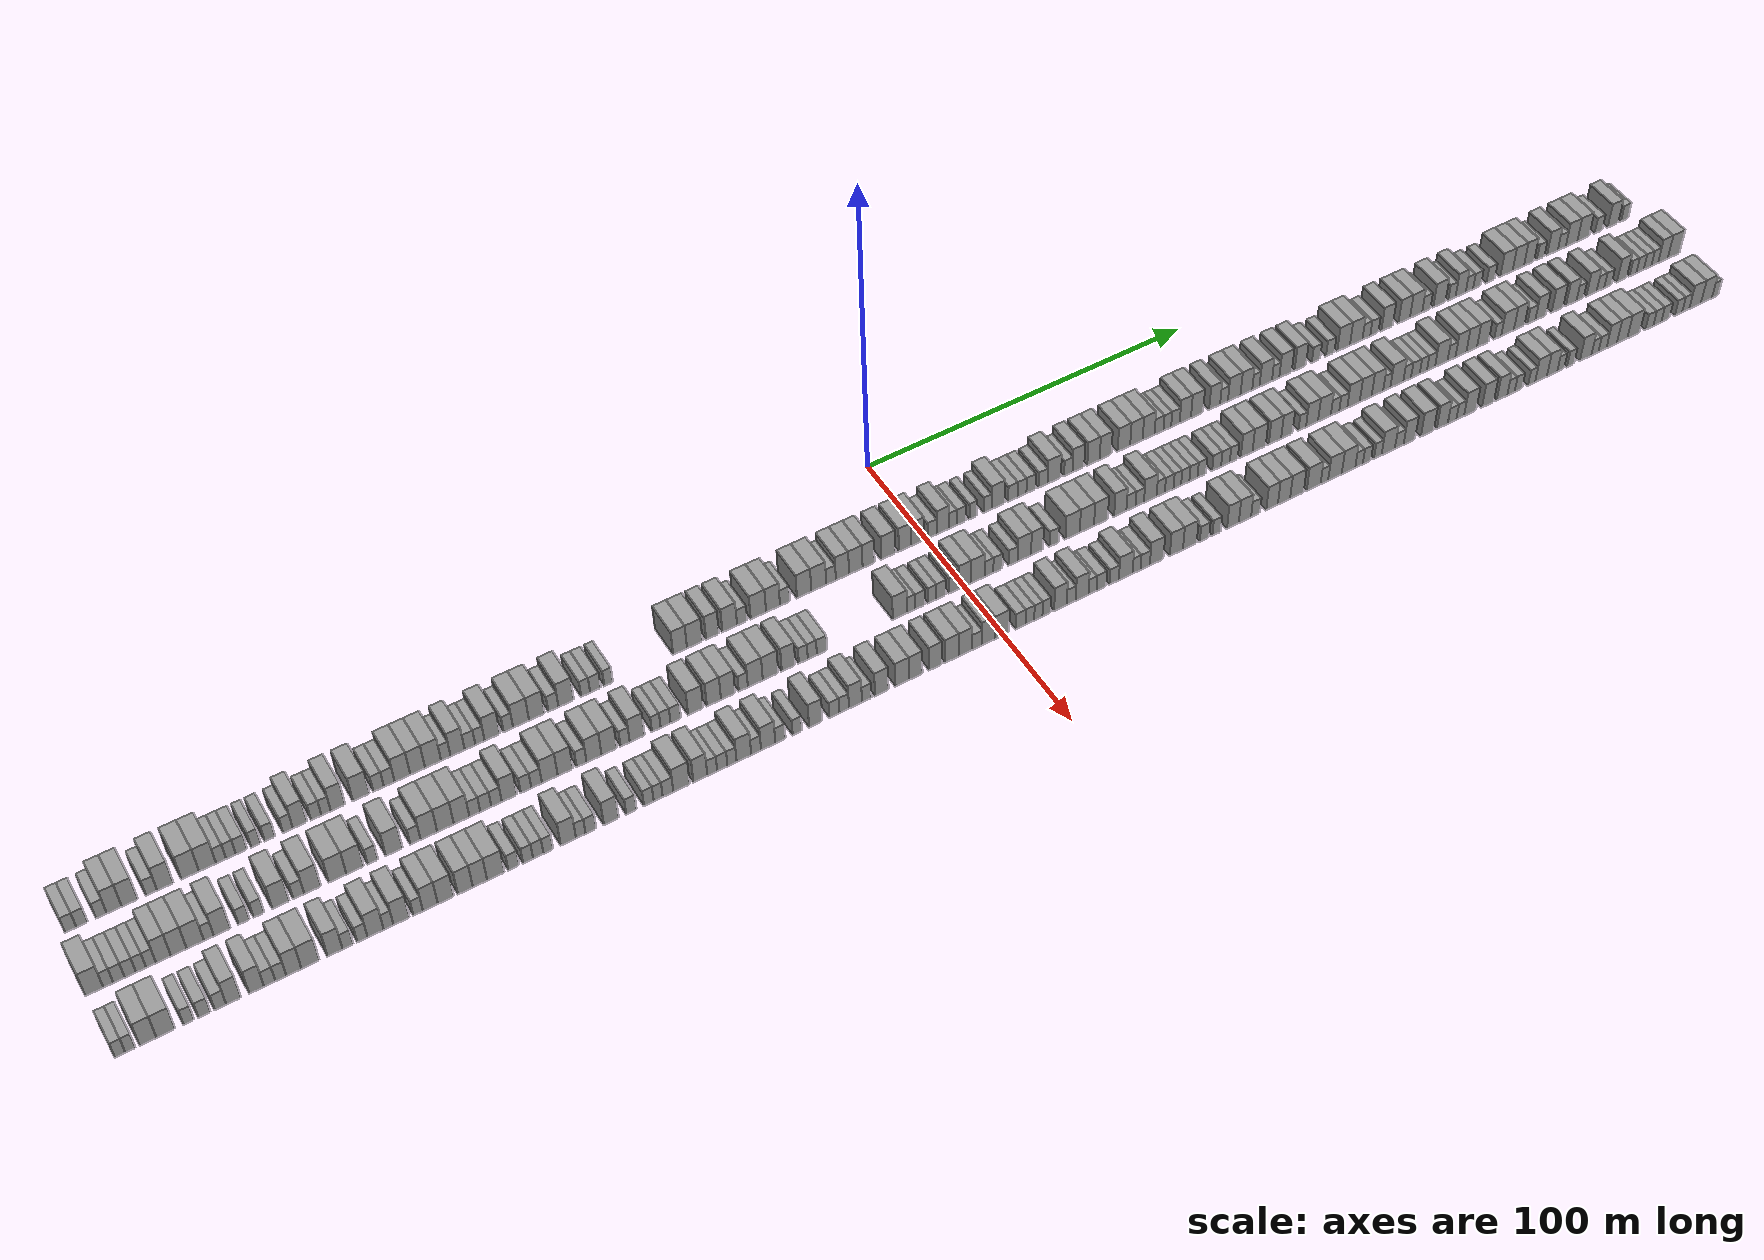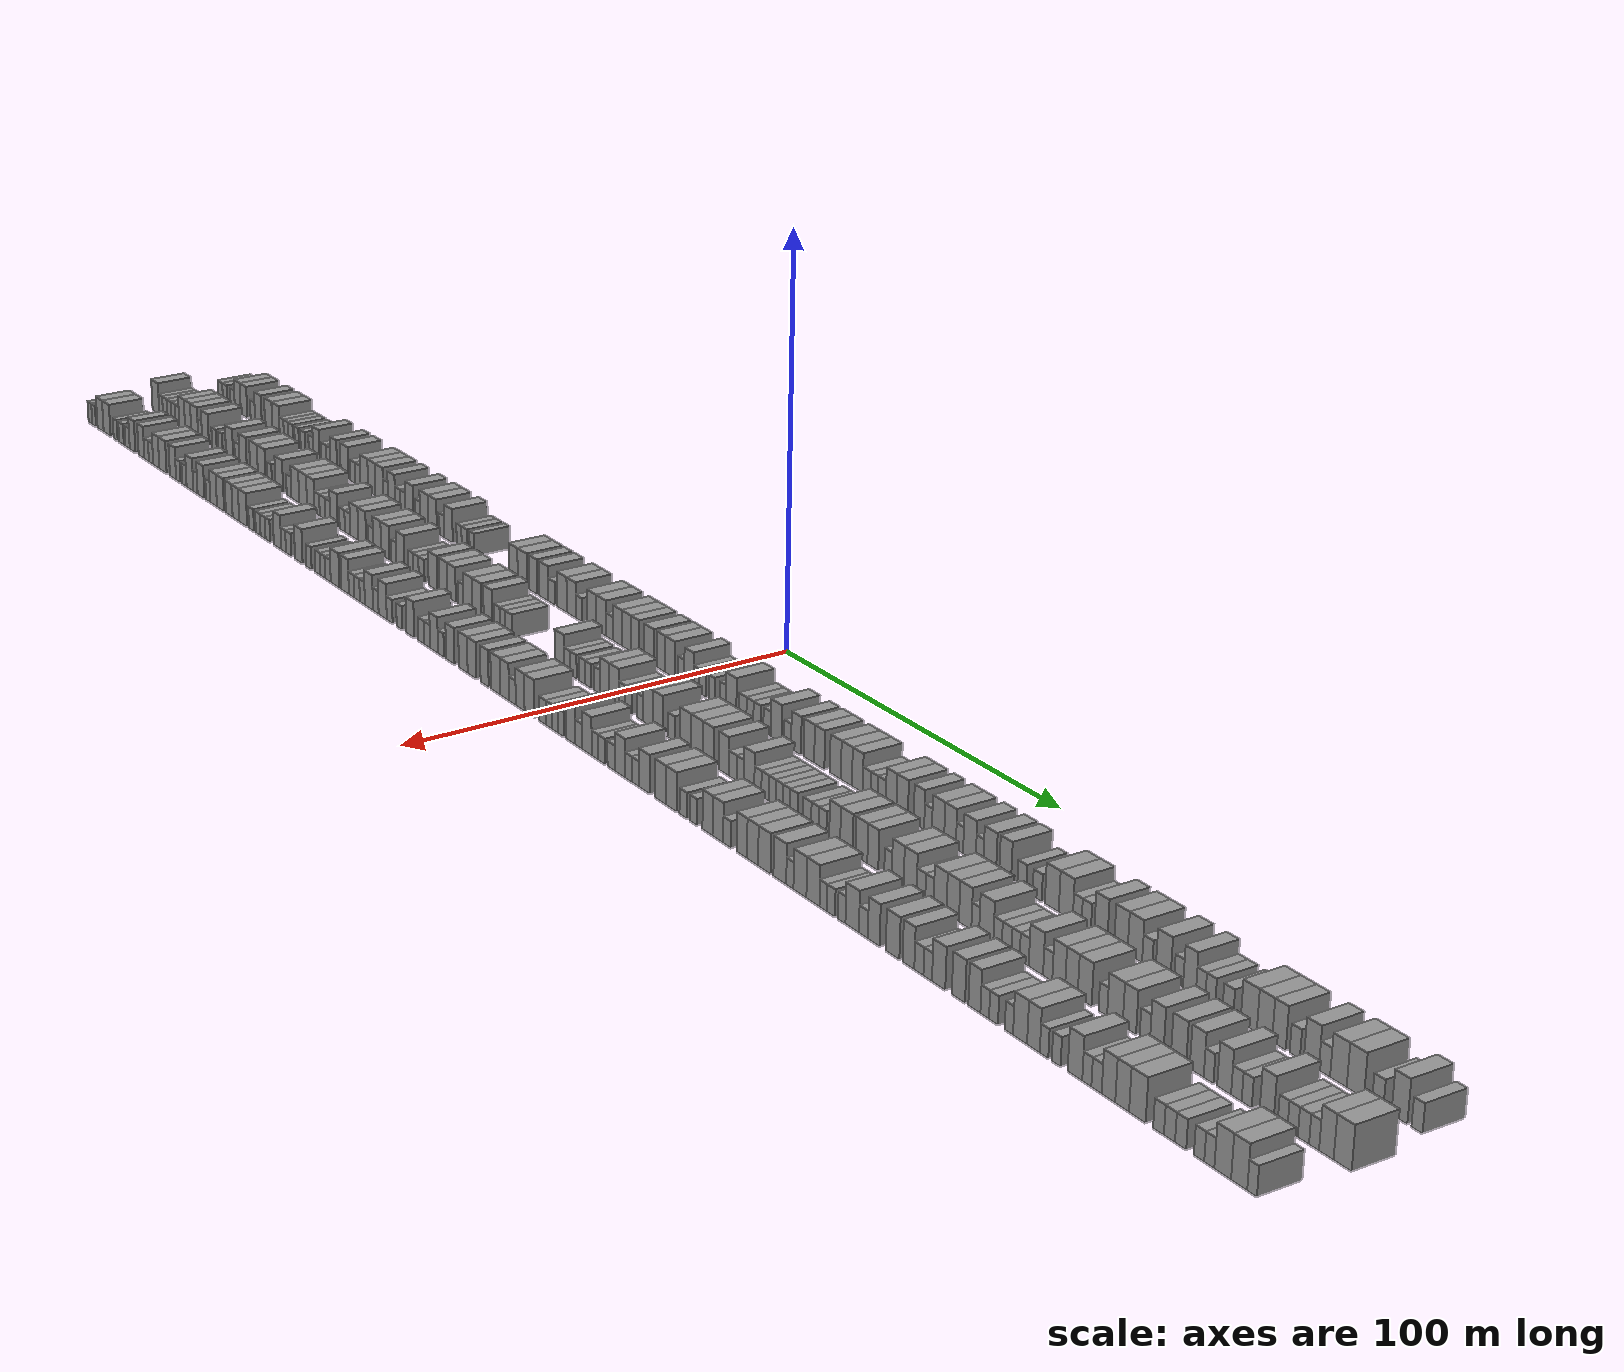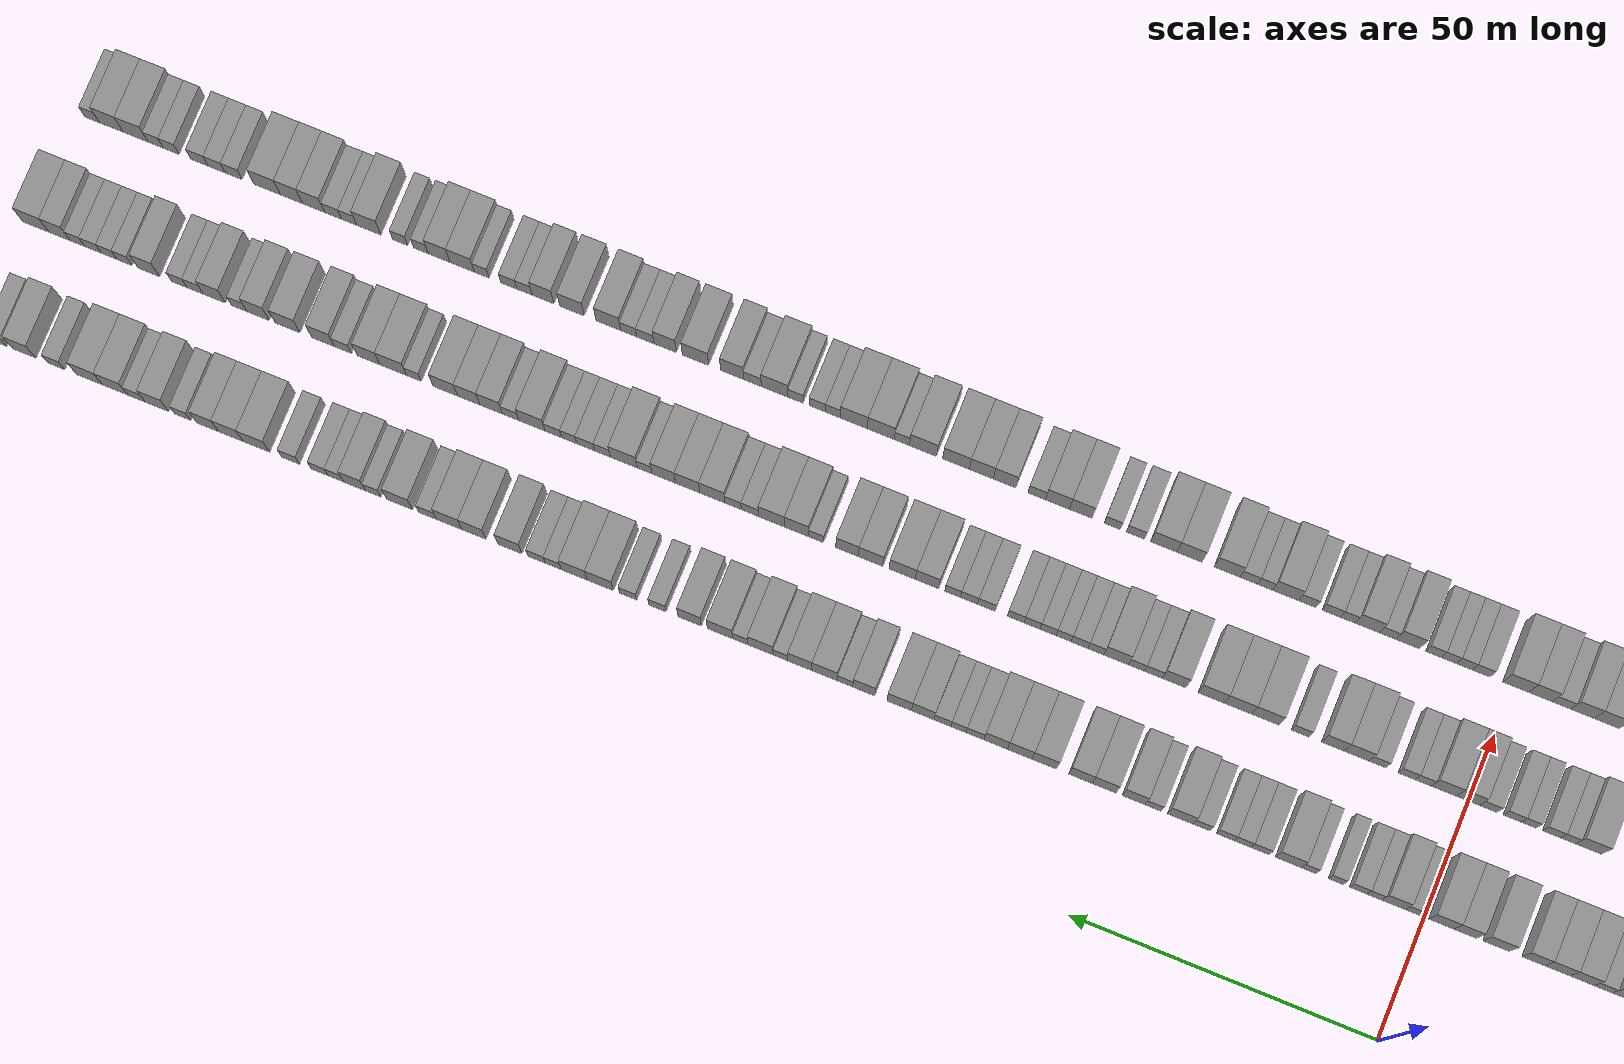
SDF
<sdf version="1.6">
 <world name="default">
  <scene>
   <sky><clouds><speed>12</speed></clouds></sky>
   <ambient>0.4 0.4 0.4 1</ambient>
   <background>0.7 0.7 0.7 1</background>
   <shadows>1</shadows>
  </scene>
  <gravity>0 0 -9.8066</gravity>
  <magnetic_field>6e-06 2.3e-05 -4.2e-05</magnetic_field>
  <physics default="0" name="default_physics" type="ode">
   <ode>
    <solver>
     <type>quick</type>
     <iters>10</iters>
     <sor>1.0</sor>
     <use_dynamic_moi_rescaling>0</use_dynamic_moi_rescaling>
    </solver>
    <constraints>
     <cfm>0</cfm>
     <erp>0.2</erp>
     <contact_max_correcting_vel>100</contact_max_correcting_vel>
     <contact_surface_layer>0.001</contact_surface_layer>
    </constraints>
   </ode>
   <max_step_size>0.004</max_step_size>
   <real_time_factor>1</real_time_factor>
   <real_time_update_rate>250</real_time_update_rate>
  </physics>
  <light name="sun" type="directional">
   <pose>0 0 10 0 0 0</pose>
   <diffuse>0.8 0.8 0.8 1</diffuse>
   <specular>0.2 0.2 0.2 1</specular>
   <attenuation>
    <range>1000</range>
    <constant>0.9</constant>
    <linear>0.01</linear>
    <quadratic>0.001</quadratic>
   </attenuation>
   <direction>-0.5 0.1 -0.9</direction>
  </light>
  <model name="building_1">
   <static>1</static>
   <pose>25.0000 -232.6099 0 0.000000 0.000000 0.000000</pose>
   <link name="link">
    <pose>0 0 3.00 0 0 0</pose>
    <collision name="collision"><geometry><box><size>10.0000 2.7802 6.0000</size></box></geometry></collision>
    <visual name="visual">
     <cast_shadows>0</cast_shadows>
     <geometry><box><size>10.0000 2.7802 6.0000</size></box></geometry>
     <material>
      <script>
       <uri>model://grey_wall/materials/scripts</uri>
       <uri>model://grey_wall/materials/textures</uri>
       <name>vrc/grey_wall</name>
      </script>
     </material>
    </visual>
   </link>
  </model>
  <model name="building_2">
   <static>1</static>
   <pose>25.0000 -229.8317 0 0.000000 0.000000 0.000000</pose>
   <link name="link">
    <pose>0 0 3.00 0 0 0</pose>
    <collision name="collision"><geometry><box><size>10.0000 2.7760 6.0000</size></box></geometry></collision>
    <visual name="visual">
     <cast_shadows>0</cast_shadows>
     <geometry><box><size>10.0000 2.7760 6.0000</size></box></geometry>
     <material>
      <script>
       <uri>model://grey_wall/materials/scripts</uri>
       <uri>model://grey_wall/materials/textures</uri>
       <name>vrc/grey_wall</name>
      </script>
     </material>
    </visual>
   </link>
  </model>
  <model name="building_3">
   <static>1</static>
   <pose>25.0000 -225.1301 0 0.000000 0.000000 0.000000</pose>
   <link name="link">
    <pose>0 0 3.00 0 0 0</pose>
    <collision name="collision"><geometry><box><size>10.0000 2.6272 6.0000</size></box></geometry></collision>
    <visual name="visual">
     <cast_shadows>0</cast_shadows>
     <geometry><box><size>10.0000 2.6272 6.0000</size></box></geometry>
     <material>
      <script>
       <uri>model://grey_wall/materials/scripts</uri>
       <uri>model://grey_wall/materials/textures</uri>
       <name>vrc/grey_wall</name>
      </script>
     </material>
    </visual>
   </link>
  </model>
  <model name="building_4">
   <static>1</static>
   <pose>25.0000 -221.9718 0 0.000000 0.000000 0.000000</pose>
   <link name="link">
    <pose>0 0 4.50 0 0 0</pose>
    <collision name="collision"><geometry><box><size>10.0000 3.6894 9.0000</size></box></geometry></collision>
    <visual name="visual">
     <cast_shadows>0</cast_shadows>
     <geometry><box><size>10.0000 3.6894 9.0000</size></box></geometry>
     <material>
      <script>
       <uri>model://grey_wall/materials/scripts</uri>
       <uri>model://grey_wall/materials/textures</uri>
       <name>vrc/grey_wall</name>
      </script>
     </material>
    </visual>
   </link>
  </model>
  <model name="building_5">
   <static>1</static>
   <pose>25.0000 -218.1359 0 0.000000 0.000000 0.000000</pose>
   <link name="link">
    <pose>0 0 4.50 0 0 0</pose>
    <collision name="collision"><geometry><box><size>10.0000 3.9824 9.0000</size></box></geometry></collision>
    <visual name="visual">
     <cast_shadows>0</cast_shadows>
     <geometry><box><size>10.0000 3.9824 9.0000</size></box></geometry>
     <material>
      <script>
       <uri>model://grey_wall/materials/scripts</uri>
       <uri>model://grey_wall/materials/textures</uri>
       <name>vrc/grey_wall</name>
      </script>
     </material>
    </visual>
   </link>
  </model>
  <model name="building_6">
   <static>1</static>
   <pose>25.0000 -212.7679 0 0.000000 0.000000 0.000000</pose>
   <link name="link">
    <pose>0 0 3.00 0 0 0</pose>
    <collision name="collision"><geometry><box><size>10.0000 2.7537 6.0000</size></box></geometry></collision>
    <visual name="visual">
     <cast_shadows>0</cast_shadows>
     <geometry><box><size>10.0000 2.7537 6.0000</size></box></geometry>
     <material>
      <script>
       <uri>model://grey_wall/materials/scripts</uri>
       <uri>model://grey_wall/materials/textures</uri>
       <name>vrc/grey_wall</name>
      </script>
     </material>
    </visual>
   </link>
  </model>
  <model name="building_7">
   <static>1</static>
   <pose>25.0000 -209.3598 0 0.000000 0.000000 0.000000</pose>
   <link name="link">
    <pose>0 0 4.50 0 0 0</pose>
    <collision name="collision"><geometry><box><size>10.0000 4.0625 9.0000</size></box></geometry></collision>
    <visual name="visual">
     <cast_shadows>0</cast_shadows>
     <geometry><box><size>10.0000 4.0625 9.0000</size></box></geometry>
     <material>
      <script>
       <uri>model://grey_wall/materials/scripts</uri>
       <uri>model://grey_wall/materials/textures</uri>
       <name>vrc/grey_wall</name>
      </script>
     </material>
    </visual>
   </link>
  </model>
  <model name="building_8">
   <static>1</static>
   <pose>25.0000 -203.1391 0 0.000000 0.000000 0.000000</pose>
   <link name="link">
    <pose>0 0 4.50 0 0 0</pose>
    <collision name="collision"><geometry><box><size>10.0000 4.3790 9.0000</size></box></geometry></collision>
    <visual name="visual">
     <cast_shadows>0</cast_shadows>
     <geometry><box><size>10.0000 4.3790 9.0000</size></box></geometry>
     <material>
      <script>
       <uri>model://grey_wall/materials/scripts</uri>
       <uri>model://grey_wall/materials/textures</uri>
       <name>vrc/grey_wall</name>
      </script>
     </material>
    </visual>
   </link>
  </model>
  <model name="building_9">
   <static>1</static>
   <pose>25.0000 -198.7892 0 0.000000 0.000000 0.000000</pose>
   <link name="link">
    <pose>0 0 4.50 0 0 0</pose>
    <collision name="collision"><geometry><box><size>10.0000 4.3207 9.0000</size></box></geometry></collision>
    <visual name="visual">
     <cast_shadows>0</cast_shadows>
     <geometry><box><size>10.0000 4.3207 9.0000</size></box></geometry>
     <material>
      <script>
       <uri>model://grey_wall/materials/scripts</uri>
       <uri>model://grey_wall/materials/textures</uri>
       <name>vrc/grey_wall</name>
      </script>
     </material>
    </visual>
   </link>
  </model>
  <model name="building_10">
   <static>1</static>
   <pose>25.0000 -195.3868 0 0.000000 0.000000 0.000000</pose>
   <link name="link">
    <pose>0 0 3.00 0 0 0</pose>
    <collision name="collision"><geometry><box><size>10.0000 2.4841 6.0000</size></box></geometry></collision>
    <visual name="visual">
     <cast_shadows>0</cast_shadows>
     <geometry><box><size>10.0000 2.4841 6.0000</size></box></geometry>
     <material>
      <script>
       <uri>model://grey_wall/materials/scripts</uri>
       <uri>model://grey_wall/materials/textures</uri>
       <name>vrc/grey_wall</name>
      </script>
     </material>
    </visual>
   </link>
  </model>
  <model name="building_11">
   <static>1</static>
   <pose>25.0000 -192.8999 0 0.000000 0.000000 0.000000</pose>
   <link name="link">
    <pose>0 0 3.00 0 0 0</pose>
    <collision name="collision"><geometry><box><size>10.0000 2.4897 6.0000</size></box></geometry></collision>
    <visual name="visual">
     <cast_shadows>0</cast_shadows>
     <geometry><box><size>10.0000 2.4897 6.0000</size></box></geometry>
     <material>
      <script>
       <uri>model://grey_wall/materials/scripts</uri>
       <uri>model://grey_wall/materials/textures</uri>
       <name>vrc/grey_wall</name>
      </script>
     </material>
    </visual>
   </link>
  </model>
  <model name="building_12">
   <static>1</static>
   <pose>25.0000 -190.2014 0 0.000000 0.000000 0.000000</pose>
   <link name="link">
    <pose>0 0 3.00 0 0 0</pose>
    <collision name="collision"><geometry><box><size>10.0000 2.9074 6.0000</size></box></geometry></collision>
    <visual name="visual">
     <cast_shadows>0</cast_shadows>
     <geometry><box><size>10.0000 2.9074 6.0000</size></box></geometry>
     <material>
      <script>
       <uri>model://grey_wall/materials/scripts</uri>
       <uri>model://grey_wall/materials/textures</uri>
       <name>vrc/grey_wall</name>
      </script>
     </material>
    </visual>
   </link>
  </model>
  <model name="building_13">
   <static>1</static>
   <pose>25.0000 -186.5393 0 0.000000 0.000000 0.000000</pose>
   <link name="link">
    <pose>0 0 3.00 0 0 0</pose>
    <collision name="collision"><geometry><box><size>10.0000 2.4167 6.0000</size></box></geometry></collision>
    <visual name="visual">
     <cast_shadows>0</cast_shadows>
     <geometry><box><size>10.0000 2.4167 6.0000</size></box></geometry>
     <material>
      <script>
       <uri>model://grey_wall/materials/scripts</uri>
       <uri>model://grey_wall/materials/textures</uri>
       <name>vrc/grey_wall</name>
      </script>
     </material>
    </visual>
   </link>
  </model>
  <model name="building_14">
   <static>1</static>
   <pose>25.0000 -182.9748 0 0.000000 0.000000 0.000000</pose>
   <link name="link">
    <pose>0 0 3.00 0 0 0</pose>
    <collision name="collision"><geometry><box><size>10.0000 2.7123 6.0000</size></box></geometry></collision>
    <visual name="visual">
     <cast_shadows>0</cast_shadows>
     <geometry><box><size>10.0000 2.7123 6.0000</size></box></geometry>
     <material>
      <script>
       <uri>model://grey_wall/materials/scripts</uri>
       <uri>model://grey_wall/materials/textures</uri>
       <name>vrc/grey_wall</name>
      </script>
     </material>
    </visual>
   </link>
  </model>
  <model name="building_15">
   <static>1</static>
   <pose>25.0000 -178.3584 0 0.000000 0.000000 0.000000</pose>
   <link name="link">
    <pose>0 0 3.00 0 0 0</pose>
    <collision name="collision"><geometry><box><size>10.0000 2.5205 6.0000</size></box></geometry></collision>
    <visual name="visual">
     <cast_shadows>0</cast_shadows>
     <geometry><box><size>10.0000 2.5205 6.0000</size></box></geometry>
     <material>
      <script>
       <uri>model://grey_wall/materials/scripts</uri>
       <uri>model://grey_wall/materials/textures</uri>
       <name>vrc/grey_wall</name>
      </script>
     </material>
    </visual>
   </link>
  </model>
  <model name="building_16">
   <static>1</static>
   <pose>25.0000 -175.2598 0 0.000000 0.000000 0.000000</pose>
   <link name="link">
    <pose>0 0 4.50 0 0 0</pose>
    <collision name="collision"><geometry><box><size>10.0000 3.6767 9.0000</size></box></geometry></collision>
    <visual name="visual">
     <cast_shadows>0</cast_shadows>
     <geometry><box><size>10.0000 3.6767 9.0000</size></box></geometry>
     <material>
      <script>
       <uri>model://grey_wall/materials/scripts</uri>
       <uri>model://grey_wall/materials/textures</uri>
       <name>vrc/grey_wall</name>
      </script>
     </material>
    </visual>
   </link>
  </model>
  <model name="building_17">
   <static>1</static>
   <pose>25.0000 -171.0749 0 0.000000 0.000000 0.000000</pose>
   <link name="link">
    <pose>0 0 3.00 0 0 0</pose>
    <collision name="collision"><geometry><box><size>10.0000 2.6930 6.0000</size></box></geometry></collision>
    <visual name="visual">
     <cast_shadows>0</cast_shadows>
     <geometry><box><size>10.0000 2.6930 6.0000</size></box></geometry>
     <material>
      <script>
       <uri>model://grey_wall/materials/scripts</uri>
       <uri>model://grey_wall/materials/textures</uri>
       <name>vrc/grey_wall</name>
      </script>
     </material>
    </visual>
   </link>
  </model>
  <model name="building_18">
   <static>1</static>
   <pose>25.0000 -168.5283 0 0.000000 0.000000 0.000000</pose>
   <link name="link">
    <pose>0 0 3.00 0 0 0</pose>
    <collision name="collision"><geometry><box><size>10.0000 2.4003 6.0000</size></box></geometry></collision>
    <visual name="visual">
     <cast_shadows>0</cast_shadows>
     <geometry><box><size>10.0000 2.4003 6.0000</size></box></geometry>
     <material>
      <script>
       <uri>model://grey_wall/materials/scripts</uri>
       <uri>model://grey_wall/materials/textures</uri>
       <name>vrc/grey_wall</name>
      </script>
     </material>
    </visual>
   </link>
  </model>
  <model name="building_19">
   <static>1</static>
   <pose>25.0000 -165.4497 0 0.000000 0.000000 0.000000</pose>
   <link name="link">
    <pose>0 0 4.50 0 0 0</pose>
    <collision name="collision"><geometry><box><size>10.0000 3.7568 9.0000</size></box></geometry></collision>
    <visual name="visual">
     <cast_shadows>0</cast_shadows>
     <geometry><box><size>10.0000 3.7568 9.0000</size></box></geometry>
     <material>
      <script>
       <uri>model://grey_wall/materials/scripts</uri>
       <uri>model://grey_wall/materials/textures</uri>
       <name>vrc/grey_wall</name>
      </script>
     </material>
    </visual>
   </link>
  </model>
  <model name="building_20">
   <static>1</static>
   <pose>25.0000 -159.3955 0 0.000000 0.000000 0.000000</pose>
   <link name="link">
    <pose>0 0 4.50 0 0 0</pose>
    <collision name="collision"><geometry><box><size>10.0000 4.3517 9.0000</size></box></geometry></collision>
    <visual name="visual">
     <cast_shadows>0</cast_shadows>
     <geometry><box><size>10.0000 4.3517 9.0000</size></box></geometry>
     <material>
      <script>
       <uri>model://grey_wall/materials/scripts</uri>
       <uri>model://grey_wall/materials/textures</uri>
       <name>vrc/grey_wall</name>
      </script>
     </material>
    </visual>
   </link>
  </model>
  <model name="building_21">
   <static>1</static>
   <pose>25.0000 -154.8324 0 0.000000 0.000000 0.000000</pose>
   <link name="link">
    <pose>0 0 3.00 0 0 0</pose>
    <collision name="collision"><geometry><box><size>10.0000 2.7744 6.0000</size></box></geometry></collision>
    <visual name="visual">
     <cast_shadows>0</cast_shadows>
     <geometry><box><size>10.0000 2.7744 6.0000</size></box></geometry>
     <material>
      <script>
       <uri>model://grey_wall/materials/scripts</uri>
       <uri>model://grey_wall/materials/textures</uri>
       <name>vrc/grey_wall</name>
      </script>
     </material>
    </visual>
   </link>
  </model>
  <model name="building_22">
   <static>1</static>
   <pose>25.0000 -152.0281 0 0.000000 0.000000 0.000000</pose>
   <link name="link">
    <pose>0 0 3.00 0 0 0</pose>
    <collision name="collision"><geometry><box><size>10.0000 2.8342 6.0000</size></box></geometry></collision>
    <visual name="visual">
     <cast_shadows>0</cast_shadows>
     <geometry><box><size>10.0000 2.8342 6.0000</size></box></geometry>
     <material>
      <script>
       <uri>model://grey_wall/materials/scripts</uri>
       <uri>model://grey_wall/materials/textures</uri>
       <name>vrc/grey_wall</name>
      </script>
     </material>
    </visual>
   </link>
  </model>
  <model name="building_23">
   <static>1</static>
   <pose>25.0000 -148.5362 0 0.000000 0.000000 0.000000</pose>
   <link name="link">
    <pose>0 0 4.50 0 0 0</pose>
    <collision name="collision"><geometry><box><size>10.0000 4.1496 9.0000</size></box></geometry></collision>
    <visual name="visual">
     <cast_shadows>0</cast_shadows>
     <geometry><box><size>10.0000 4.1496 9.0000</size></box></geometry>
     <material>
      <script>
       <uri>model://grey_wall/materials/scripts</uri>
       <uri>model://grey_wall/materials/textures</uri>
       <name>vrc/grey_wall</name>
      </script>
     </material>
    </visual>
   </link>
  </model>
  <model name="building_24">
   <static>1</static>
   <pose>25.0000 -144.5103 0 0.000000 0.000000 0.000000</pose>
   <link name="link">
    <pose>0 0 4.50 0 0 0</pose>
    <collision name="collision"><geometry><box><size>10.0000 3.9021 9.0000</size></box></geometry></collision>
    <visual name="visual">
     <cast_shadows>0</cast_shadows>
     <geometry><box><size>10.0000 3.9021 9.0000</size></box></geometry>
     <material>
      <script>
       <uri>model://grey_wall/materials/scripts</uri>
       <uri>model://grey_wall/materials/textures</uri>
       <name>vrc/grey_wall</name>
      </script>
     </material>
    </visual>
   </link>
  </model>
  <model name="building_25">
   <static>1</static>
   <pose>25.0000 -140.4267 0 0.000000 0.000000 0.000000</pose>
   <link name="link">
    <pose>0 0 4.50 0 0 0</pose>
    <collision name="collision"><geometry><box><size>10.0000 4.2650 9.0000</size></box></geometry></collision>
    <visual name="visual">
     <cast_shadows>0</cast_shadows>
     <geometry><box><size>10.0000 4.2650 9.0000</size></box></geometry>
     <material>
      <script>
       <uri>model://grey_wall/materials/scripts</uri>
       <uri>model://grey_wall/materials/textures</uri>
       <name>vrc/grey_wall</name>
      </script>
     </material>
    </visual>
   </link>
  </model>
  <model name="building_26">
   <static>1</static>
   <pose>25.0000 -137.0217 0 0.000000 0.000000 0.000000</pose>
   <link name="link">
    <pose>0 0 3.00 0 0 0</pose>
    <collision name="collision"><geometry><box><size>10.0000 2.5450 6.0000</size></box></geometry></collision>
    <visual name="visual">
     <cast_shadows>0</cast_shadows>
     <geometry><box><size>10.0000 2.5450 6.0000</size></box></geometry>
     <material>
      <script>
       <uri>model://grey_wall/materials/scripts</uri>
       <uri>model://grey_wall/materials/textures</uri>
       <name>vrc/grey_wall</name>
      </script>
     </material>
    </visual>
   </link>
  </model>
  <model name="building_27">
   <static>1</static>
   <pose>25.0000 -133.8552 0 0.000000 0.000000 0.000000</pose>
   <link name="link">
    <pose>0 0 4.50 0 0 0</pose>
    <collision name="collision"><geometry><box><size>10.0000 3.7879 9.0000</size></box></geometry></collision>
    <visual name="visual">
     <cast_shadows>0</cast_shadows>
     <geometry><box><size>10.0000 3.7879 9.0000</size></box></geometry>
     <material>
      <script>
       <uri>model://grey_wall/materials/scripts</uri>
       <uri>model://grey_wall/materials/textures</uri>
       <name>vrc/grey_wall</name>
      </script>
     </material>
    </visual>
   </link>
  </model>
  <model name="building_28">
   <static>1</static>
   <pose>25.0000 -130.5221 0 0.000000 0.000000 0.000000</pose>
   <link name="link">
    <pose>0 0 3.00 0 0 0</pose>
    <collision name="collision"><geometry><box><size>10.0000 2.8782 6.0000</size></box></geometry></collision>
    <visual name="visual">
     <cast_shadows>0</cast_shadows>
     <geometry><box><size>10.0000 2.8782 6.0000</size></box></geometry>
     <material>
      <script>
       <uri>model://grey_wall/materials/scripts</uri>
       <uri>model://grey_wall/materials/textures</uri>
       <name>vrc/grey_wall</name>
      </script>
     </material>
    </visual>
   </link>
  </model>
  <model name="building_29">
   <static>1</static>
   <pose>25.0000 -127.8385 0 0.000000 0.000000 0.000000</pose>
   <link name="link">
    <pose>0 0 3.00 0 0 0</pose>
    <collision name="collision"><geometry><box><size>10.0000 2.4891 6.0000</size></box></geometry></collision>
    <visual name="visual">
     <cast_shadows>0</cast_shadows>
     <geometry><box><size>10.0000 2.4891 6.0000</size></box></geometry>
     <material>
      <script>
       <uri>model://grey_wall/materials/scripts</uri>
       <uri>model://grey_wall/materials/textures</uri>
       <name>vrc/grey_wall</name>
      </script>
     </material>
    </visual>
   </link>
  </model>
  <model name="building_30">
   <static>1</static>
   <pose>25.0000 -124.5212 0 0.000000 0.000000 0.000000</pose>
   <link name="link">
    <pose>0 0 4.50 0 0 0</pose>
    <collision name="collision"><geometry><box><size>10.0000 4.1453 9.0000</size></box></geometry></collision>
    <visual name="visual">
     <cast_shadows>0</cast_shadows>
     <geometry><box><size>10.0000 4.1453 9.0000</size></box></geometry>
     <material>
      <script>
       <uri>model://grey_wall/materials/scripts</uri>
       <uri>model://grey_wall/materials/textures</uri>
       <name>vrc/grey_wall</name>
      </script>
     </material>
    </visual>
   </link>
  </model>
  <model name="building_31">
   <static>1</static>
   <pose>25.0000 -120.1653 0 0.000000 0.000000 0.000000</pose>
   <link name="link">
    <pose>0 0 3.00 0 0 0</pose>
    <collision name="collision"><geometry><box><size>10.0000 2.5666 6.0000</size></box></geometry></collision>
    <visual name="visual">
     <cast_shadows>0</cast_shadows>
     <geometry><box><size>10.0000 2.5666 6.0000</size></box></geometry>
     <material>
      <script>
       <uri>model://grey_wall/materials/scripts</uri>
       <uri>model://grey_wall/materials/textures</uri>
       <name>vrc/grey_wall</name>
      </script>
     </material>
    </visual>
   </link>
  </model>
  <model name="building_32">
   <static>1</static>
   <pose>25.0000 -116.7060 0 0.000000 0.000000 0.000000</pose>
   <link name="link">
    <pose>0 0 4.50 0 0 0</pose>
    <collision name="collision"><geometry><box><size>10.0000 4.3518 9.0000</size></box></geometry></collision>
    <visual name="visual">
     <cast_shadows>0</cast_shadows>
     <geometry><box><size>10.0000 4.3518 9.0000</size></box></geometry>
     <material>
      <script>
       <uri>model://grey_wall/materials/scripts</uri>
       <uri>model://grey_wall/materials/textures</uri>
       <name>vrc/grey_wall</name>
      </script>
     </material>
    </visual>
   </link>
  </model>
  <model name="building_33">
   <static>1</static>
   <pose>25.0000 -112.3912 0 0.000000 0.000000 0.000000</pose>
   <link name="link">
    <pose>0 0 4.50 0 0 0</pose>
    <collision name="collision"><geometry><box><size>10.0000 4.2779 9.0000</size></box></geometry></collision>
    <visual name="visual">
     <cast_shadows>0</cast_shadows>
     <geometry><box><size>10.0000 4.2779 9.0000</size></box></geometry>
     <material>
      <script>
       <uri>model://grey_wall/materials/scripts</uri>
       <uri>model://grey_wall/materials/textures</uri>
       <name>vrc/grey_wall</name>
      </script>
     </material>
    </visual>
   </link>
  </model>
  <model name="building_34">
   <static>1</static>
   <pose>25.0000 -107.8504 0 0.000000 0.000000 0.000000</pose>
   <link name="link">
    <pose>0 0 3.00 0 0 0</pose>
    <collision name="collision"><geometry><box><size>10.0000 2.8036 6.0000</size></box></geometry></collision>
    <visual name="visual">
     <cast_shadows>0</cast_shadows>
     <geometry><box><size>10.0000 2.8036 6.0000</size></box></geometry>
     <material>
      <script>
       <uri>model://grey_wall/materials/scripts</uri>
       <uri>model://grey_wall/materials/textures</uri>
       <name>vrc/grey_wall</name>
      </script>
     </material>
    </visual>
   </link>
  </model>
  <model name="building_35">
   <static>1</static>
   <pose>25.0000 -104.3303 0 0.000000 0.000000 0.000000</pose>
   <link name="link">
    <pose>0 0 4.50 0 0 0</pose>
    <collision name="collision"><geometry><box><size>10.0000 4.2367 9.0000</size></box></geometry></collision>
    <visual name="visual">
     <cast_shadows>0</cast_shadows>
     <geometry><box><size>10.0000 4.2367 9.0000</size></box></geometry>
     <material>
      <script>
       <uri>model://grey_wall/materials/scripts</uri>
       <uri>model://grey_wall/materials/textures</uri>
       <name>vrc/grey_wall</name>
      </script>
     </material>
    </visual>
   </link>
  </model>
  <model name="building_36">
   <static>1</static>
   <pose>25.0000 -98.9672 0 0.000000 0.000000 0.000000</pose>
   <link name="link">
    <pose>0 0 3.00 0 0 0</pose>
    <collision name="collision"><geometry><box><size>10.0000 2.4895 6.0000</size></box></geometry></collision>
    <visual name="visual">
     <cast_shadows>0</cast_shadows>
     <geometry><box><size>10.0000 2.4895 6.0000</size></box></geometry>
     <material>
      <script>
       <uri>model://grey_wall/materials/scripts</uri>
       <uri>model://grey_wall/materials/textures</uri>
       <name>vrc/grey_wall</name>
      </script>
     </material>
    </visual>
   </link>
  </model>
  <model name="building_37">
   <static>1</static>
   <pose>25.0000 -96.2437 0 0.000000 0.000000 0.000000</pose>
   <link name="link">
    <pose>0 0 3.00 0 0 0</pose>
    <collision name="collision"><geometry><box><size>10.0000 2.9575 6.0000</size></box></geometry></collision>
    <visual name="visual">
     <cast_shadows>0</cast_shadows>
     <geometry><box><size>10.0000 2.9575 6.0000</size></box></geometry>
     <material>
      <script>
       <uri>model://grey_wall/materials/scripts</uri>
       <uri>model://grey_wall/materials/textures</uri>
       <name>vrc/grey_wall</name>
      </script>
     </material>
    </visual>
   </link>
  </model>
  <model name="building_38">
   <static>1</static>
   <pose>25.0000 -92.5641 0 0.000000 0.000000 0.000000</pose>
   <link name="link">
    <pose>0 0 3.00 0 0 0</pose>
    <collision name="collision"><geometry><box><size>10.0000 2.4018 6.0000</size></box></geometry></collision>
    <visual name="visual">
     <cast_shadows>0</cast_shadows>
     <geometry><box><size>10.0000 2.4018 6.0000</size></box></geometry>
     <material>
      <script>
       <uri>model://grey_wall/materials/scripts</uri>
       <uri>model://grey_wall/materials/textures</uri>
       <name>vrc/grey_wall</name>
      </script>
     </material>
    </visual>
   </link>
  </model>
  <model name="building_39">
   <static>1</static>
   <pose>25.0000 -72.4263 0 0.000000 0.000000 0.000000</pose>
   <link name="link">
    <pose>0 0 4.50 0 0 0</pose>
    <collision name="collision"><geometry><box><size>10.0000 3.9579 9.0000</size></box></geometry></collision>
    <visual name="visual">
     <cast_shadows>0</cast_shadows>
     <geometry><box><size>10.0000 3.9579 9.0000</size></box></geometry>
     <material>
      <script>
       <uri>model://grey_wall/materials/scripts</uri>
       <uri>model://grey_wall/materials/textures</uri>
       <name>vrc/grey_wall</name>
      </script>
     </material>
    </visual>
   </link>
  </model>
  <model name="building_40">
   <static>1</static>
   <pose>25.0000 -68.2231 0 0.000000 0.000000 0.000000</pose>
   <link name="link">
    <pose>0 0 4.50 0 0 0</pose>
    <collision name="collision"><geometry><box><size>10.0000 4.4485 9.0000</size></box></geometry></collision>
    <visual name="visual">
     <cast_shadows>0</cast_shadows>
     <geometry><box><size>10.0000 4.4485 9.0000</size></box></geometry>
     <material>
      <script>
       <uri>model://grey_wall/materials/scripts</uri>
       <uri>model://grey_wall/materials/textures</uri>
       <name>vrc/grey_wall</name>
      </script>
     </material>
    </visual>
   </link>
  </model>
  <model name="building_41">
   <static>1</static>
   <pose>25.0000 -63.1592 0 0.000000 0.000000 0.000000</pose>
   <link name="link">
    <pose>0 0 4.50 0 0 0</pose>
    <collision name="collision"><geometry><box><size>10.0000 3.6792 9.0000</size></box></geometry></collision>
    <visual name="visual">
     <cast_shadows>0</cast_shadows>
     <geometry><box><size>10.0000 3.6792 9.0000</size></box></geometry>
     <material>
      <script>
       <uri>model://grey_wall/materials/scripts</uri>
       <uri>model://grey_wall/materials/textures</uri>
       <name>vrc/grey_wall</name>
      </script>
     </material>
    </visual>
   </link>
  </model>
  <model name="building_42">
   <static>1</static>
   <pose>25.0000 -58.2063 0 0.000000 0.000000 0.000000</pose>
   <link name="link">
    <pose>0 0 4.50 0 0 0</pose>
    <collision name="collision"><geometry><box><size>10.0000 4.2266 9.0000</size></box></geometry></collision>
    <visual name="visual">
     <cast_shadows>0</cast_shadows>
     <geometry><box><size>10.0000 4.2266 9.0000</size></box></geometry>
     <material>
      <script>
       <uri>model://grey_wall/materials/scripts</uri>
       <uri>model://grey_wall/materials/textures</uri>
       <name>vrc/grey_wall</name>
      </script>
     </material>
    </visual>
   </link>
  </model>
  <model name="building_43">
   <static>1</static>
   <pose>25.0000 -54.6282 0 0.000000 0.000000 0.000000</pose>
   <link name="link">
    <pose>0 0 3.00 0 0 0</pose>
    <collision name="collision"><geometry><box><size>10.0000 2.9298 6.0000</size></box></geometry></collision>
    <visual name="visual">
     <cast_shadows>0</cast_shadows>
     <geometry><box><size>10.0000 2.9298 6.0000</size></box></geometry>
     <material>
      <script>
       <uri>model://grey_wall/materials/scripts</uri>
       <uri>model://grey_wall/materials/textures</uri>
       <name>vrc/grey_wall</name>
      </script>
     </material>
    </visual>
   </link>
  </model>
  <model name="building_44">
   <static>1</static>
   <pose>25.0000 -49.9291 0 0.000000 0.000000 0.000000</pose>
   <link name="link">
    <pose>0 0 4.50 0 0 0</pose>
    <collision name="collision"><geometry><box><size>10.0000 4.4683 9.0000</size></box></geometry></collision>
    <visual name="visual">
     <cast_shadows>0</cast_shadows>
     <geometry><box><size>10.0000 4.4683 9.0000</size></box></geometry>
     <material>
      <script>
       <uri>model://grey_wall/materials/scripts</uri>
       <uri>model://grey_wall/materials/textures</uri>
       <name>vrc/grey_wall</name>
      </script>
     </material>
    </visual>
   </link>
  </model>
  <model name="building_45">
   <static>1</static>
   <pose>25.0000 -45.6569 0 0.000000 0.000000 0.000000</pose>
   <link name="link">
    <pose>0 0 4.50 0 0 0</pose>
    <collision name="collision"><geometry><box><size>10.0000 4.0762 9.0000</size></box></geometry></collision>
    <visual name="visual">
     <cast_shadows>0</cast_shadows>
     <geometry><box><size>10.0000 4.0762 9.0000</size></box></geometry>
     <material>
      <script>
       <uri>model://grey_wall/materials/scripts</uri>
       <uri>model://grey_wall/materials/textures</uri>
       <name>vrc/grey_wall</name>
      </script>
     </material>
    </visual>
   </link>
  </model>
  <model name="building_46">
   <static>1</static>
   <pose>25.0000 -42.1469 0 0.000000 0.000000 0.000000</pose>
   <link name="link">
    <pose>0 0 3.00 0 0 0</pose>
    <collision name="collision"><geometry><box><size>10.0000 2.9438 6.0000</size></box></geometry></collision>
    <visual name="visual">
     <cast_shadows>0</cast_shadows>
     <geometry><box><size>10.0000 2.9438 6.0000</size></box></geometry>
     <material>
      <script>
       <uri>model://grey_wall/materials/scripts</uri>
       <uri>model://grey_wall/materials/textures</uri>
       <name>vrc/grey_wall</name>
      </script>
     </material>
    </visual>
   </link>
  </model>
  <model name="building_47">
   <static>1</static>
   <pose>25.0000 -36.5564 0 0.000000 0.000000 0.000000</pose>
   <link name="link">
    <pose>0 0 4.50 0 0 0</pose>
    <collision name="collision"><geometry><box><size>10.0000 4.2373 9.0000</size></box></geometry></collision>
    <visual name="visual">
     <cast_shadows>0</cast_shadows>
     <geometry><box><size>10.0000 4.2373 9.0000</size></box></geometry>
     <material>
      <script>
       <uri>model://grey_wall/materials/scripts</uri>
       <uri>model://grey_wall/materials/textures</uri>
       <name>vrc/grey_wall</name>
      </script>
     </material>
    </visual>
   </link>
  </model>
  <model name="building_48">
   <static>1</static>
   <pose>25.0000 -32.2310 0 0.000000 0.000000 0.000000</pose>
   <link name="link">
    <pose>0 0 4.50 0 0 0</pose>
    <collision name="collision"><geometry><box><size>10.0000 4.4135 9.0000</size></box></geometry></collision>
    <visual name="visual">
     <cast_shadows>0</cast_shadows>
     <geometry><box><size>10.0000 4.4135 9.0000</size></box></geometry>
     <material>
      <script>
       <uri>model://grey_wall/materials/scripts</uri>
       <uri>model://grey_wall/materials/textures</uri>
       <name>vrc/grey_wall</name>
      </script>
     </material>
    </visual>
   </link>
  </model>
  <model name="building_49">
   <static>1</static>
   <pose>25.0000 -28.6008 0 0.000000 0.000000 0.000000</pose>
   <link name="link">
    <pose>0 0 3.00 0 0 0</pose>
    <collision name="collision"><geometry><box><size>10.0000 2.8468 6.0000</size></box></geometry></collision>
    <visual name="visual">
     <cast_shadows>0</cast_shadows>
     <geometry><box><size>10.0000 2.8468 6.0000</size></box></geometry>
     <material>
      <script>
       <uri>model://grey_wall/materials/scripts</uri>
       <uri>model://grey_wall/materials/textures</uri>
       <name>vrc/grey_wall</name>
      </script>
     </material>
    </visual>
   </link>
  </model>
  <model name="building_50">
   <static>1</static>
   <pose>25.0000 -25.2103 0 0.000000 0.000000 0.000000</pose>
   <link name="link">
    <pose>0 0 4.50 0 0 0</pose>
    <collision name="collision"><geometry><box><size>10.0000 3.9343 9.0000</size></box></geometry></collision>
    <visual name="visual">
     <cast_shadows>0</cast_shadows>
     <geometry><box><size>10.0000 3.9343 9.0000</size></box></geometry>
     <material>
      <script>
       <uri>model://grey_wall/materials/scripts</uri>
       <uri>model://grey_wall/materials/textures</uri>
       <name>vrc/grey_wall</name>
      </script>
     </material>
    </visual>
   </link>
  </model>
  <model name="building_51">
   <static>1</static>
   <pose>25.0000 -21.2290 0 0.000000 0.000000 0.000000</pose>
   <link name="link">
    <pose>0 0 4.50 0 0 0</pose>
    <collision name="collision"><geometry><box><size>10.0000 4.0283 9.0000</size></box></geometry></collision>
    <visual name="visual">
     <cast_shadows>0</cast_shadows>
     <geometry><box><size>10.0000 4.0283 9.0000</size></box></geometry>
     <material>
      <script>
       <uri>model://grey_wall/materials/scripts</uri>
       <uri>model://grey_wall/materials/textures</uri>
       <name>vrc/grey_wall</name>
      </script>
     </material>
    </visual>
   </link>
  </model>
  <model name="building_52">
   <static>1</static>
   <pose>25.0000 -17.4095 0 0.000000 0.000000 0.000000</pose>
   <link name="link">
    <pose>0 0 4.50 0 0 0</pose>
    <collision name="collision"><geometry><box><size>10.0000 3.6106 9.0000</size></box></geometry></collision>
    <visual name="visual">
     <cast_shadows>0</cast_shadows>
     <geometry><box><size>10.0000 3.6106 9.0000</size></box></geometry>
     <material>
      <script>
       <uri>model://grey_wall/materials/scripts</uri>
       <uri>model://grey_wall/materials/textures</uri>
       <name>vrc/grey_wall</name>
      </script>
     </material>
    </visual>
   </link>
  </model>
  <model name="building_53">
   <static>1</static>
   <pose>25.0000 -11.4642 0 0.000000 0.000000 0.000000</pose>
   <link name="link">
    <pose>0 0 4.50 0 0 0</pose>
    <collision name="collision"><geometry><box><size>10.0000 4.2801 9.0000</size></box></geometry></collision>
    <visual name="visual">
     <cast_shadows>0</cast_shadows>
     <geometry><box><size>10.0000 4.2801 9.0000</size></box></geometry>
     <material>
      <script>
       <uri>model://grey_wall/materials/scripts</uri>
       <uri>model://grey_wall/materials/textures</uri>
       <name>vrc/grey_wall</name>
      </script>
     </material>
    </visual>
   </link>
  </model>
  <model name="building_54">
   <static>1</static>
   <pose>25.0000 -6.4950 0 0.000000 0.000000 0.000000</pose>
   <link name="link">
    <pose>0 0 4.50 0 0 0</pose>
    <collision name="collision"><geometry><box><size>10.0000 3.6582 9.0000</size></box></geometry></collision>
    <visual name="visual">
     <cast_shadows>0</cast_shadows>
     <geometry><box><size>10.0000 3.6582 9.0000</size></box></geometry>
     <material>
      <script>
       <uri>model://grey_wall/materials/scripts</uri>
       <uri>model://grey_wall/materials/textures</uri>
       <name>vrc/grey_wall</name>
      </script>
     </material>
    </visual>
   </link>
  </model>
  <model name="building_55">
   <static>1</static>
   <pose>25.0000 -2.6202 0 0.000000 0.000000 0.000000</pose>
   <link name="link">
    <pose>0 0 4.50 0 0 0</pose>
    <collision name="collision"><geometry><box><size>10.0000 4.0915 9.0000</size></box></geometry></collision>
    <visual name="visual">
     <cast_shadows>0</cast_shadows>
     <geometry><box><size>10.0000 4.0915 9.0000</size></box></geometry>
     <material>
      <script>
       <uri>model://grey_wall/materials/scripts</uri>
       <uri>model://grey_wall/materials/textures</uri>
       <name>vrc/grey_wall</name>
      </script>
     </material>
    </visual>
   </link>
  </model>
  <model name="building_56">
   <static>1</static>
   <pose>25.0000 1.8327 0 0.000000 0.000000 0.000000</pose>
   <link name="link">
    <pose>0 0 3.00 0 0 0</pose>
    <collision name="collision"><geometry><box><size>10.0000 2.8143 6.0000</size></box></geometry></collision>
    <visual name="visual">
     <cast_shadows>0</cast_shadows>
     <geometry><box><size>10.0000 2.8143 6.0000</size></box></geometry>
     <material>
      <script>
       <uri>model://grey_wall/materials/scripts</uri>
       <uri>model://grey_wall/materials/textures</uri>
       <name>vrc/grey_wall</name>
      </script>
     </material>
    </visual>
   </link>
  </model>
  <model name="building_57">
   <static>1</static>
   <pose>25.0000 5.1196 0 0.000000 0.000000 0.000000</pose>
   <link name="link">
    <pose>0 0 4.50 0 0 0</pose>
    <collision name="collision"><geometry><box><size>10.0000 3.7595 9.0000</size></box></geometry></collision>
    <visual name="visual">
     <cast_shadows>0</cast_shadows>
     <geometry><box><size>10.0000 3.7595 9.0000</size></box></geometry>
     <material>
      <script>
       <uri>model://grey_wall/materials/scripts</uri>
       <uri>model://grey_wall/materials/textures</uri>
       <name>vrc/grey_wall</name>
      </script>
     </material>
    </visual>
   </link>
  </model>
  <model name="building_58">
   <static>1</static>
   <pose>25.0000 8.2092 0 0.000000 0.000000 0.000000</pose>
   <link name="link">
    <pose>0 0 3.00 0 0 0</pose>
    <collision name="collision"><geometry><box><size>10.0000 2.4197 6.0000</size></box></geometry></collision>
    <visual name="visual">
     <cast_shadows>0</cast_shadows>
     <geometry><box><size>10.0000 2.4197 6.0000</size></box></geometry>
     <material>
      <script>
       <uri>model://grey_wall/materials/scripts</uri>
       <uri>model://grey_wall/materials/textures</uri>
       <name>vrc/grey_wall</name>
      </script>
     </material>
    </visual>
   </link>
  </model>
  <model name="building_59">
   <static>1</static>
   <pose>25.0000 10.8201 0 0.000000 0.000000 0.000000</pose>
   <link name="link">
    <pose>0 0 3.00 0 0 0</pose>
    <collision name="collision"><geometry><box><size>10.0000 2.8023 6.0000</size></box></geometry></collision>
    <visual name="visual">
     <cast_shadows>0</cast_shadows>
     <geometry><box><size>10.0000 2.8023 6.0000</size></box></geometry>
     <material>
      <script>
       <uri>model://grey_wall/materials/scripts</uri>
       <uri>model://grey_wall/materials/textures</uri>
       <name>vrc/grey_wall</name>
      </script>
     </material>
    </visual>
   </link>
  </model>
  <model name="building_60">
   <static>1</static>
   <pose>25.0000 14.4315 0 0.000000 0.000000 0.000000</pose>
   <link name="link">
    <pose>0 0 3.00 0 0 0</pose>
    <collision name="collision"><geometry><box><size>10.0000 2.4205 6.0000</size></box></geometry></collision>
    <visual name="visual">
     <cast_shadows>0</cast_shadows>
     <geometry><box><size>10.0000 2.4205 6.0000</size></box></geometry>
     <material>
      <script>
       <uri>model://grey_wall/materials/scripts</uri>
       <uri>model://grey_wall/materials/textures</uri>
       <name>vrc/grey_wall</name>
      </script>
     </material>
    </visual>
   </link>
  </model>
  <model name="building_61">
   <static>1</static>
   <pose>25.0000 18.8458 0 0.000000 0.000000 0.000000</pose>
   <link name="link">
    <pose>0 0 3.00 0 0 0</pose>
    <collision name="collision"><geometry><box><size>10.0000 2.4080 6.0000</size></box></geometry></collision>
    <visual name="visual">
     <cast_shadows>0</cast_shadows>
     <geometry><box><size>10.0000 2.4080 6.0000</size></box></geometry>
     <material>
      <script>
       <uri>model://grey_wall/materials/scripts</uri>
       <uri>model://grey_wall/materials/textures</uri>
       <name>vrc/grey_wall</name>
      </script>
     </material>
    </visual>
   </link>
  </model>
  <model name="building_62">
   <static>1</static>
   <pose>25.0000 22.1373 0 0.000000 0.000000 0.000000</pose>
   <link name="link">
    <pose>0 0 4.50 0 0 0</pose>
    <collision name="collision"><geometry><box><size>10.0000 4.1751 9.0000</size></box></geometry></collision>
    <visual name="visual">
     <cast_shadows>0</cast_shadows>
     <geometry><box><size>10.0000 4.1751 9.0000</size></box></geometry>
     <material>
      <script>
       <uri>model://grey_wall/materials/scripts</uri>
       <uri>model://grey_wall/materials/textures</uri>
       <name>vrc/grey_wall</name>
      </script>
     </material>
    </visual>
   </link>
  </model>
  <model name="building_63">
   <static>1</static>
   <pose>25.0000 26.7054 0 0.000000 0.000000 0.000000</pose>
   <link name="link">
    <pose>0 0 3.00 0 0 0</pose>
    <collision name="collision"><geometry><box><size>10.0000 2.9611 6.0000</size></box></geometry></collision>
    <visual name="visual">
     <cast_shadows>0</cast_shadows>
     <geometry><box><size>10.0000 2.9611 6.0000</size></box></geometry>
     <material>
      <script>
       <uri>model://grey_wall/materials/scripts</uri>
       <uri>model://grey_wall/materials/textures</uri>
       <name>vrc/grey_wall</name>
      </script>
     </material>
    </visual>
   </link>
  </model>
  <model name="building_64">
   <static>1</static>
   <pose>25.0000 29.5410 0 0.000000 0.000000 0.000000</pose>
   <link name="link">
    <pose>0 0 3.00 0 0 0</pose>
    <collision name="collision"><geometry><box><size>10.0000 2.7100 6.0000</size></box></geometry></collision>
    <visual name="visual">
     <cast_shadows>0</cast_shadows>
     <geometry><box><size>10.0000 2.7100 6.0000</size></box></geometry>
     <material>
      <script>
       <uri>model://grey_wall/materials/scripts</uri>
       <uri>model://grey_wall/materials/textures</uri>
       <name>vrc/grey_wall</name>
      </script>
     </material>
    </visual>
   </link>
  </model>
  <model name="building_65">
   <static>1</static>
   <pose>25.0000 32.3366 0 0.000000 0.000000 0.000000</pose>
   <link name="link">
    <pose>0 0 3.00 0 0 0</pose>
    <collision name="collision"><geometry><box><size>10.0000 2.8812 6.0000</size></box></geometry></collision>
    <visual name="visual">
     <cast_shadows>0</cast_shadows>
     <geometry><box><size>10.0000 2.8812 6.0000</size></box></geometry>
     <material>
      <script>
       <uri>model://grey_wall/materials/scripts</uri>
       <uri>model://grey_wall/materials/textures</uri>
       <name>vrc/grey_wall</name>
      </script>
     </material>
    </visual>
   </link>
  </model>
  <model name="building_66">
   <static>1</static>
   <pose>25.0000 36.1805 0 0.000000 0.000000 0.000000</pose>
   <link name="link">
    <pose>0 0 3.00 0 0 0</pose>
    <collision name="collision"><geometry><box><size>10.0000 2.8066 6.0000</size></box></geometry></collision>
    <visual name="visual">
     <cast_shadows>0</cast_shadows>
     <geometry><box><size>10.0000 2.8066 6.0000</size></box></geometry>
     <material>
      <script>
       <uri>model://grey_wall/materials/scripts</uri>
       <uri>model://grey_wall/materials/textures</uri>
       <name>vrc/grey_wall</name>
      </script>
     </material>
    </visual>
   </link>
  </model>
  <model name="building_67">
   <static>1</static>
   <pose>25.0000 39.6690 0 0.000000 0.000000 0.000000</pose>
   <link name="link">
    <pose>0 0 4.50 0 0 0</pose>
    <collision name="collision"><geometry><box><size>10.0000 4.1702 9.0000</size></box></geometry></collision>
    <visual name="visual">
     <cast_shadows>0</cast_shadows>
     <geometry><box><size>10.0000 4.1702 9.0000</size></box></geometry>
     <material>
      <script>
       <uri>model://grey_wall/materials/scripts</uri>
       <uri>model://grey_wall/materials/textures</uri>
       <name>vrc/grey_wall</name>
      </script>
     </material>
    </visual>
   </link>
  </model>
  <model name="building_68">
   <static>1</static>
   <pose>25.0000 44.0798 0 0.000000 0.000000 0.000000</pose>
   <link name="link">
    <pose>0 0 3.00 0 0 0</pose>
    <collision name="collision"><geometry><box><size>10.0000 2.6514 6.0000</size></box></geometry></collision>
    <visual name="visual">
     <cast_shadows>0</cast_shadows>
     <geometry><box><size>10.0000 2.6514 6.0000</size></box></geometry>
     <material>
      <script>
       <uri>model://grey_wall/materials/scripts</uri>
       <uri>model://grey_wall/materials/textures</uri>
       <name>vrc/grey_wall</name>
      </script>
     </material>
    </visual>
   </link>
  </model>
  <model name="building_69">
   <static>1</static>
   <pose>25.0000 47.2660 0 0.000000 0.000000 0.000000</pose>
   <link name="link">
    <pose>0 0 4.50 0 0 0</pose>
    <collision name="collision"><geometry><box><size>10.0000 3.7211 9.0000</size></box></geometry></collision>
    <visual name="visual">
     <cast_shadows>0</cast_shadows>
     <geometry><box><size>10.0000 3.7211 9.0000</size></box></geometry>
     <material>
      <script>
       <uri>model://grey_wall/materials/scripts</uri>
       <uri>model://grey_wall/materials/textures</uri>
       <name>vrc/grey_wall</name>
      </script>
     </material>
    </visual>
   </link>
  </model>
  <model name="building_70">
   <static>1</static>
   <pose>25.0000 52.0918 0 0.000000 0.000000 0.000000</pose>
   <link name="link">
    <pose>0 0 4.50 0 0 0</pose>
    <collision name="collision"><geometry><box><size>10.0000 3.9304 9.0000</size></box></geometry></collision>
    <visual name="visual">
     <cast_shadows>0</cast_shadows>
     <geometry><box><size>10.0000 3.9304 9.0000</size></box></geometry>
     <material>
      <script>
       <uri>model://grey_wall/materials/scripts</uri>
       <uri>model://grey_wall/materials/textures</uri>
       <name>vrc/grey_wall</name>
      </script>
     </material>
    </visual>
   </link>
  </model>
  <model name="building_71">
   <static>1</static>
   <pose>25.0000 55.9439 0 0.000000 0.000000 0.000000</pose>
   <link name="link">
    <pose>0 0 4.50 0 0 0</pose>
    <collision name="collision"><geometry><box><size>10.0000 3.7738 9.0000</size></box></geometry></collision>
    <visual name="visual">
     <cast_shadows>0</cast_shadows>
     <geometry><box><size>10.0000 3.7738 9.0000</size></box></geometry>
     <material>
      <script>
       <uri>model://grey_wall/materials/scripts</uri>
       <uri>model://grey_wall/materials/textures</uri>
       <name>vrc/grey_wall</name>
      </script>
     </material>
    </visual>
   </link>
  </model>
  <model name="building_72">
   <static>1</static>
   <pose>25.0000 61.8441 0 0.000000 0.000000 0.000000</pose>
   <link name="link">
    <pose>0 0 4.50 0 0 0</pose>
    <collision name="collision"><geometry><box><size>10.0000 4.0265 9.0000</size></box></geometry></collision>
    <visual name="visual">
     <cast_shadows>0</cast_shadows>
     <geometry><box><size>10.0000 4.0265 9.0000</size></box></geometry>
     <material>
      <script>
       <uri>model://grey_wall/materials/scripts</uri>
       <uri>model://grey_wall/materials/textures</uri>
       <name>vrc/grey_wall</name>
      </script>
     </material>
    </visual>
   </link>
  </model>
  <model name="building_73">
   <static>1</static>
   <pose>25.0000 65.8667 0 0.000000 0.000000 0.000000</pose>
   <link name="link">
    <pose>0 0 4.50 0 0 0</pose>
    <collision name="collision"><geometry><box><size>10.0000 4.0188 9.0000</size></box></geometry></collision>
    <visual name="visual">
     <cast_shadows>0</cast_shadows>
     <geometry><box><size>10.0000 4.0188 9.0000</size></box></geometry>
     <material>
      <script>
       <uri>model://grey_wall/materials/scripts</uri>
       <uri>model://grey_wall/materials/textures</uri>
       <name>vrc/grey_wall</name>
      </script>
     </material>
    </visual>
   </link>
  </model>
  <model name="building_74">
   <static>1</static>
   <pose>25.0000 69.8110 0 0.000000 0.000000 0.000000</pose>
   <link name="link">
    <pose>0 0 4.50 0 0 0</pose>
    <collision name="collision"><geometry><box><size>10.0000 3.8698 9.0000</size></box></geometry></collision>
    <visual name="visual">
     <cast_shadows>0</cast_shadows>
     <geometry><box><size>10.0000 3.8698 9.0000</size></box></geometry>
     <material>
      <script>
       <uri>model://grey_wall/materials/scripts</uri>
       <uri>model://grey_wall/materials/textures</uri>
       <name>vrc/grey_wall</name>
      </script>
     </material>
    </visual>
   </link>
  </model>
  <model name="building_75">
   <static>1</static>
   <pose>25.0000 73.2030 0 0.000000 0.000000 0.000000</pose>
   <link name="link">
    <pose>0 0 3.00 0 0 0</pose>
    <collision name="collision"><geometry><box><size>10.0000 2.9143 6.0000</size></box></geometry></collision>
    <visual name="visual">
     <cast_shadows>0</cast_shadows>
     <geometry><box><size>10.0000 2.9143 6.0000</size></box></geometry>
     <material>
      <script>
       <uri>model://grey_wall/materials/scripts</uri>
       <uri>model://grey_wall/materials/textures</uri>
       <name>vrc/grey_wall</name>
      </script>
     </material>
    </visual>
   </link>
  </model>
  <model name="building_76">
   <static>1</static>
   <pose>25.0000 75.8986 0 0.000000 0.000000 0.000000</pose>
   <link name="link">
    <pose>0 0 3.00 0 0 0</pose>
    <collision name="collision"><geometry><box><size>10.0000 2.4769 6.0000</size></box></geometry></collision>
    <visual name="visual">
     <cast_shadows>0</cast_shadows>
     <geometry><box><size>10.0000 2.4769 6.0000</size></box></geometry>
     <material>
      <script>
       <uri>model://grey_wall/materials/scripts</uri>
       <uri>model://grey_wall/materials/textures</uri>
       <name>vrc/grey_wall</name>
      </script>
     </material>
    </visual>
   </link>
  </model>
  <model name="building_77">
   <static>1</static>
   <pose>25.0000 78.5214 0 0.000000 0.000000 0.000000</pose>
   <link name="link">
    <pose>0 0 3.00 0 0 0</pose>
    <collision name="collision"><geometry><box><size>10.0000 2.7688 6.0000</size></box></geometry></collision>
    <visual name="visual">
     <cast_shadows>0</cast_shadows>
     <geometry><box><size>10.0000 2.7688 6.0000</size></box></geometry>
     <material>
      <script>
       <uri>model://grey_wall/materials/scripts</uri>
       <uri>model://grey_wall/materials/textures</uri>
       <name>vrc/grey_wall</name>
      </script>
     </material>
    </visual>
   </link>
  </model>
  <model name="building_78">
   <static>1</static>
   <pose>25.0000 81.7602 0 0.000000 0.000000 0.000000</pose>
   <link name="link">
    <pose>0 0 4.50 0 0 0</pose>
    <collision name="collision"><geometry><box><size>10.0000 3.7087 9.0000</size></box></geometry></collision>
    <visual name="visual">
     <cast_shadows>0</cast_shadows>
     <geometry><box><size>10.0000 3.7087 9.0000</size></box></geometry>
     <material>
      <script>
       <uri>model://grey_wall/materials/scripts</uri>
       <uri>model://grey_wall/materials/textures</uri>
       <name>vrc/grey_wall</name>
      </script>
     </material>
    </visual>
   </link>
  </model>
  <model name="building_79">
   <static>1</static>
   <pose>25.0000 85.6125 0 0.000000 0.000000 0.000000</pose>
   <link name="link">
    <pose>0 0 4.50 0 0 0</pose>
    <collision name="collision"><geometry><box><size>10.0000 3.9959 9.0000</size></box></geometry></collision>
    <visual name="visual">
     <cast_shadows>0</cast_shadows>
     <geometry><box><size>10.0000 3.9959 9.0000</size></box></geometry>
     <material>
      <script>
       <uri>model://grey_wall/materials/scripts</uri>
       <uri>model://grey_wall/materials/textures</uri>
       <name>vrc/grey_wall</name>
      </script>
     </material>
    </visual>
   </link>
  </model>
  <model name="building_80">
   <static>1</static>
   <pose>25.0000 91.4239 0 0.000000 0.000000 0.000000</pose>
   <link name="link">
    <pose>0 0 4.50 0 0 0</pose>
    <collision name="collision"><geometry><box><size>10.0000 3.6268 9.0000</size></box></geometry></collision>
    <visual name="visual">
     <cast_shadows>0</cast_shadows>
     <geometry><box><size>10.0000 3.6268 9.0000</size></box></geometry>
     <material>
      <script>
       <uri>model://grey_wall/materials/scripts</uri>
       <uri>model://grey_wall/materials/textures</uri>
       <name>vrc/grey_wall</name>
      </script>
     </material>
    </visual>
   </link>
  </model>
  <model name="building_81">
   <static>1</static>
   <pose>25.0000 94.5368 0 0.000000 0.000000 0.000000</pose>
   <link name="link">
    <pose>0 0 3.00 0 0 0</pose>
    <collision name="collision"><geometry><box><size>10.0000 2.5991 6.0000</size></box></geometry></collision>
    <visual name="visual">
     <cast_shadows>0</cast_shadows>
     <geometry><box><size>10.0000 2.5991 6.0000</size></box></geometry>
     <material>
      <script>
       <uri>model://grey_wall/materials/scripts</uri>
       <uri>model://grey_wall/materials/textures</uri>
       <name>vrc/grey_wall</name>
      </script>
     </material>
    </visual>
   </link>
  </model>
  <model name="building_82">
   <static>1</static>
   <pose>25.0000 97.9126 0 0.000000 0.000000 0.000000</pose>
   <link name="link">
    <pose>0 0 4.50 0 0 0</pose>
    <collision name="collision"><geometry><box><size>10.0000 4.1524 9.0000</size></box></geometry></collision>
    <visual name="visual">
     <cast_shadows>0</cast_shadows>
     <geometry><box><size>10.0000 4.1524 9.0000</size></box></geometry>
     <material>
      <script>
       <uri>model://grey_wall/materials/scripts</uri>
       <uri>model://grey_wall/materials/textures</uri>
       <name>vrc/grey_wall</name>
      </script>
     </material>
    </visual>
   </link>
  </model>
  <model name="building_83">
   <static>1</static>
   <pose>25.0000 101.9574 0 0.000000 0.000000 0.000000</pose>
   <link name="link">
    <pose>0 0 4.50 0 0 0</pose>
    <collision name="collision"><geometry><box><size>10.0000 3.9373 9.0000</size></box></geometry></collision>
    <visual name="visual">
     <cast_shadows>0</cast_shadows>
     <geometry><box><size>10.0000 3.9373 9.0000</size></box></geometry>
     <material>
      <script>
       <uri>model://grey_wall/materials/scripts</uri>
       <uri>model://grey_wall/materials/textures</uri>
       <name>vrc/grey_wall</name>
      </script>
     </material>
    </visual>
   </link>
  </model>
  <model name="building_84">
   <static>1</static>
   <pose>25.0000 105.1400 0 0.000000 0.000000 0.000000</pose>
   <link name="link">
    <pose>0 0 3.00 0 0 0</pose>
    <collision name="collision"><geometry><box><size>10.0000 2.4280 6.0000</size></box></geometry></collision>
    <visual name="visual">
     <cast_shadows>0</cast_shadows>
     <geometry><box><size>10.0000 2.4280 6.0000</size></box></geometry>
     <material>
      <script>
       <uri>model://grey_wall/materials/scripts</uri>
       <uri>model://grey_wall/materials/textures</uri>
       <name>vrc/grey_wall</name>
      </script>
     </material>
    </visual>
   </link>
  </model>
  <model name="building_85">
   <static>1</static>
   <pose>25.0000 108.4403 0 0.000000 0.000000 0.000000</pose>
   <link name="link">
    <pose>0 0 4.50 0 0 0</pose>
    <collision name="collision"><geometry><box><size>10.0000 4.1726 9.0000</size></box></geometry></collision>
    <visual name="visual">
     <cast_shadows>0</cast_shadows>
     <geometry><box><size>10.0000 4.1726 9.0000</size></box></geometry>
     <material>
      <script>
       <uri>model://grey_wall/materials/scripts</uri>
       <uri>model://grey_wall/materials/textures</uri>
       <name>vrc/grey_wall</name>
      </script>
     </material>
    </visual>
   </link>
  </model>
  <model name="building_86">
   <static>1</static>
   <pose>25.0000 111.7646 0 0.000000 0.000000 0.000000</pose>
   <link name="link">
    <pose>0 0 3.00 0 0 0</pose>
    <collision name="collision"><geometry><box><size>10.0000 2.4761 6.0000</size></box></geometry></collision>
    <visual name="visual">
     <cast_shadows>0</cast_shadows>
     <geometry><box><size>10.0000 2.4761 6.0000</size></box></geometry>
     <material>
      <script>
       <uri>model://grey_wall/materials/scripts</uri>
       <uri>model://grey_wall/materials/textures</uri>
       <name>vrc/grey_wall</name>
      </script>
     </material>
    </visual>
   </link>
  </model>
  <model name="building_87">
   <static>1</static>
   <pose>25.0000 115.0897 0 0.000000 0.000000 0.000000</pose>
   <link name="link">
    <pose>0 0 4.50 0 0 0</pose>
    <collision name="collision"><geometry><box><size>10.0000 4.1742 9.0000</size></box></geometry></collision>
    <visual name="visual">
     <cast_shadows>0</cast_shadows>
     <geometry><box><size>10.0000 4.1742 9.0000</size></box></geometry>
     <material>
      <script>
       <uri>model://grey_wall/materials/scripts</uri>
       <uri>model://grey_wall/materials/textures</uri>
       <name>vrc/grey_wall</name>
      </script>
     </material>
    </visual>
   </link>
  </model>
  <model name="building_88">
   <static>1</static>
   <pose>25.0000 120.0916 0 0.000000 0.000000 0.000000</pose>
   <link name="link">
    <pose>0 0 4.50 0 0 0</pose>
    <collision name="collision"><geometry><box><size>10.0000 3.8295 9.0000</size></box></geometry></collision>
    <visual name="visual">
     <cast_shadows>0</cast_shadows>
     <geometry><box><size>10.0000 3.8295 9.0000</size></box></geometry>
     <material>
      <script>
       <uri>model://grey_wall/materials/scripts</uri>
       <uri>model://grey_wall/materials/textures</uri>
       <name>vrc/grey_wall</name>
      </script>
     </material>
    </visual>
   </link>
  </model>
  <model name="building_89">
   <static>1</static>
   <pose>25.0000 125.4223 0 0.000000 0.000000 0.000000</pose>
   <link name="link">
    <pose>0 0 3.00 0 0 0</pose>
    <collision name="collision"><geometry><box><size>10.0000 2.8321 6.0000</size></box></geometry></collision>
    <visual name="visual">
     <cast_shadows>0</cast_shadows>
     <geometry><box><size>10.0000 2.8321 6.0000</size></box></geometry>
     <material>
      <script>
       <uri>model://grey_wall/materials/scripts</uri>
       <uri>model://grey_wall/materials/textures</uri>
       <name>vrc/grey_wall</name>
      </script>
     </material>
    </visual>
   </link>
  </model>
  <model name="building_90">
   <static>1</static>
   <pose>25.0000 130.2764 0 0.000000 0.000000 0.000000</pose>
   <link name="link">
    <pose>0 0 3.00 0 0 0</pose>
    <collision name="collision"><geometry><box><size>10.0000 2.8761 6.0000</size></box></geometry></collision>
    <visual name="visual">
     <cast_shadows>0</cast_shadows>
     <geometry><box><size>10.0000 2.8761 6.0000</size></box></geometry>
     <material>
      <script>
       <uri>model://grey_wall/materials/scripts</uri>
       <uri>model://grey_wall/materials/textures</uri>
       <name>vrc/grey_wall</name>
      </script>
     </material>
    </visual>
   </link>
  </model>
  <model name="building_91">
   <static>1</static>
   <pose>25.0000 134.8824 0 0.000000 0.000000 0.000000</pose>
   <link name="link">
    <pose>0 0 4.50 0 0 0</pose>
    <collision name="collision"><geometry><box><size>10.0000 4.3359 9.0000</size></box></geometry></collision>
    <visual name="visual">
     <cast_shadows>0</cast_shadows>
     <geometry><box><size>10.0000 4.3359 9.0000</size></box></geometry>
     <material>
      <script>
       <uri>model://grey_wall/materials/scripts</uri>
       <uri>model://grey_wall/materials/textures</uri>
       <name>vrc/grey_wall</name>
      </script>
     </material>
    </visual>
   </link>
  </model>
  <model name="building_92">
   <static>1</static>
   <pose>25.0000 139.2029 0 0.000000 0.000000 0.000000</pose>
   <link name="link">
    <pose>0 0 4.50 0 0 0</pose>
    <collision name="collision"><geometry><box><size>10.0000 4.3052 9.0000</size></box></geometry></collision>
    <visual name="visual">
     <cast_shadows>0</cast_shadows>
     <geometry><box><size>10.0000 4.3052 9.0000</size></box></geometry>
     <material>
      <script>
       <uri>model://grey_wall/materials/scripts</uri>
       <uri>model://grey_wall/materials/textures</uri>
       <name>vrc/grey_wall</name>
      </script>
     </material>
    </visual>
   </link>
  </model>
  <model name="building_93">
   <static>1</static>
   <pose>25.0000 142.6970 0 0.000000 0.000000 0.000000</pose>
   <link name="link">
    <pose>0 0 3.00 0 0 0</pose>
    <collision name="collision"><geometry><box><size>10.0000 2.6829 6.0000</size></box></geometry></collision>
    <visual name="visual">
     <cast_shadows>0</cast_shadows>
     <geometry><box><size>10.0000 2.6829 6.0000</size></box></geometry>
     <material>
      <script>
       <uri>model://grey_wall/materials/scripts</uri>
       <uri>model://grey_wall/materials/textures</uri>
       <name>vrc/grey_wall</name>
      </script>
     </material>
    </visual>
   </link>
  </model>
  <model name="building_94">
   <static>1</static>
   <pose>25.0000 145.4608 0 0.000000 0.000000 0.000000</pose>
   <link name="link">
    <pose>0 0 3.00 0 0 0</pose>
    <collision name="collision"><geometry><box><size>10.0000 2.8447 6.0000</size></box></geometry></collision>
    <visual name="visual">
     <cast_shadows>0</cast_shadows>
     <geometry><box><size>10.0000 2.8447 6.0000</size></box></geometry>
     <material>
      <script>
       <uri>model://grey_wall/materials/scripts</uri>
       <uri>model://grey_wall/materials/textures</uri>
       <name>vrc/grey_wall</name>
      </script>
     </material>
    </visual>
   </link>
  </model>
  <model name="building_95">
   <static>1</static>
   <pose>25.0000 149.8707 0 0.000000 0.000000 0.000000</pose>
   <link name="link">
    <pose>0 0 4.50 0 0 0</pose>
    <collision name="collision"><geometry><box><size>10.0000 3.9750 9.0000</size></box></geometry></collision>
    <visual name="visual">
     <cast_shadows>0</cast_shadows>
     <geometry><box><size>10.0000 3.9750 9.0000</size></box></geometry>
     <material>
      <script>
       <uri>model://grey_wall/materials/scripts</uri>
       <uri>model://grey_wall/materials/textures</uri>
       <name>vrc/grey_wall</name>
      </script>
     </material>
    </visual>
   </link>
  </model>
  <model name="building_96">
   <static>1</static>
   <pose>25.0000 155.8541 0 0.000000 0.000000 0.000000</pose>
   <link name="link">
    <pose>0 0 4.50 0 0 0</pose>
    <collision name="collision"><geometry><box><size>10.0000 3.9918 9.0000</size></box></geometry></collision>
    <visual name="visual">
     <cast_shadows>0</cast_shadows>
     <geometry><box><size>10.0000 3.9918 9.0000</size></box></geometry>
     <material>
      <script>
       <uri>model://grey_wall/materials/scripts</uri>
       <uri>model://grey_wall/materials/textures</uri>
       <name>vrc/grey_wall</name>
      </script>
     </material>
    </visual>
   </link>
  </model>
  <model name="building_97">
   <static>1</static>
   <pose>25.0000 159.9888 0 0.000000 0.000000 0.000000</pose>
   <link name="link">
    <pose>0 0 4.50 0 0 0</pose>
    <collision name="collision"><geometry><box><size>10.0000 4.2777 9.0000</size></box></geometry></collision>
    <visual name="visual">
     <cast_shadows>0</cast_shadows>
     <geometry><box><size>10.0000 4.2777 9.0000</size></box></geometry>
     <material>
      <script>
       <uri>model://grey_wall/materials/scripts</uri>
       <uri>model://grey_wall/materials/textures</uri>
       <name>vrc/grey_wall</name>
      </script>
     </material>
    </visual>
   </link>
  </model>
  <model name="building_98">
   <static>1</static>
   <pose>25.0000 163.5937 0 0.000000 0.000000 0.000000</pose>
   <link name="link">
    <pose>0 0 3.00 0 0 0</pose>
    <collision name="collision"><geometry><box><size>10.0000 2.9319 6.0000</size></box></geometry></collision>
    <visual name="visual">
     <cast_shadows>0</cast_shadows>
     <geometry><box><size>10.0000 2.9319 6.0000</size></box></geometry>
     <material>
      <script>
       <uri>model://grey_wall/materials/scripts</uri>
       <uri>model://grey_wall/materials/textures</uri>
       <name>vrc/grey_wall</name>
      </script>
     </material>
    </visual>
   </link>
  </model>
  <model name="building_99">
   <static>1</static>
   <pose>25.0000 168.2028 0 0.000000 0.000000 0.000000</pose>
   <link name="link">
    <pose>0 0 4.50 0 0 0</pose>
    <collision name="collision"><geometry><box><size>10.0000 4.2863 9.0000</size></box></geometry></collision>
    <visual name="visual">
     <cast_shadows>0</cast_shadows>
     <geometry><box><size>10.0000 4.2863 9.0000</size></box></geometry>
     <material>
      <script>
       <uri>model://grey_wall/materials/scripts</uri>
       <uri>model://grey_wall/materials/textures</uri>
       <name>vrc/grey_wall</name>
      </script>
     </material>
    </visual>
   </link>
  </model>
  <model name="building_100">
   <static>1</static>
   <pose>25.0000 172.6326 0 0.000000 0.000000 0.000000</pose>
   <link name="link">
    <pose>0 0 3.00 0 0 0</pose>
    <collision name="collision"><geometry><box><size>10.0000 2.5733 6.0000</size></box></geometry></collision>
    <visual name="visual">
     <cast_shadows>0</cast_shadows>
     <geometry><box><size>10.0000 2.5733 6.0000</size></box></geometry>
     <material>
      <script>
       <uri>model://grey_wall/materials/scripts</uri>
       <uri>model://grey_wall/materials/textures</uri>
       <name>vrc/grey_wall</name>
      </script>
     </material>
    </visual>
   </link>
  </model>
  <model name="building_101">
   <static>1</static>
   <pose>25.0000 175.7271 0 0.000000 0.000000 0.000000</pose>
   <link name="link">
    <pose>0 0 4.50 0 0 0</pose>
    <collision name="collision"><geometry><box><size>10.0000 3.6157 9.0000</size></box></geometry></collision>
    <visual name="visual">
     <cast_shadows>0</cast_shadows>
     <geometry><box><size>10.0000 3.6157 9.0000</size></box></geometry>
     <material>
      <script>
       <uri>model://grey_wall/materials/scripts</uri>
       <uri>model://grey_wall/materials/textures</uri>
       <name>vrc/grey_wall</name>
      </script>
     </material>
    </visual>
   </link>
  </model>
  <model name="building_102">
   <static>1</static>
   <pose>25.0000 178.8511 0 0.000000 0.000000 0.000000</pose>
   <link name="link">
    <pose>0 0 3.00 0 0 0</pose>
    <collision name="collision"><geometry><box><size>10.0000 2.6323 6.0000</size></box></geometry></collision>
    <visual name="visual">
     <cast_shadows>0</cast_shadows>
     <geometry><box><size>10.0000 2.6323 6.0000</size></box></geometry>
     <material>
      <script>
       <uri>model://grey_wall/materials/scripts</uri>
       <uri>model://grey_wall/materials/textures</uri>
       <name>vrc/grey_wall</name>
      </script>
     </material>
    </visual>
   </link>
  </model>
  <model name="building_103">
   <static>1</static>
   <pose>25.0000 181.5651 0 0.000000 0.000000 0.000000</pose>
   <link name="link">
    <pose>0 0 3.00 0 0 0</pose>
    <collision name="collision"><geometry><box><size>10.0000 2.7957 6.0000</size></box></geometry></collision>
    <visual name="visual">
     <cast_shadows>0</cast_shadows>
     <geometry><box><size>10.0000 2.7957 6.0000</size></box></geometry>
     <material>
      <script>
       <uri>model://grey_wall/materials/scripts</uri>
       <uri>model://grey_wall/materials/textures</uri>
       <name>vrc/grey_wall</name>
      </script>
     </material>
    </visual>
   </link>
  </model>
  <model name="building_104">
   <static>1</static>
   <pose>25.0000 186.4575 0 0.000000 0.000000 0.000000</pose>
   <link name="link">
    <pose>0 0 3.00 0 0 0</pose>
    <collision name="collision"><geometry><box><size>10.0000 2.9891 6.0000</size></box></geometry></collision>
    <visual name="visual">
     <cast_shadows>0</cast_shadows>
     <geometry><box><size>10.0000 2.9891 6.0000</size></box></geometry>
     <material>
      <script>
       <uri>model://grey_wall/materials/scripts</uri>
       <uri>model://grey_wall/materials/textures</uri>
       <name>vrc/grey_wall</name>
      </script>
     </material>
    </visual>
   </link>
  </model>
  <model name="building_105">
   <static>1</static>
   <pose>25.0000 192.1635 0 0.000000 0.000000 0.000000</pose>
   <link name="link">
    <pose>0 0 4.50 0 0 0</pose>
    <collision name="collision"><geometry><box><size>10.0000 4.4229 9.0000</size></box></geometry></collision>
    <visual name="visual">
     <cast_shadows>0</cast_shadows>
     <geometry><box><size>10.0000 4.4229 9.0000</size></box></geometry>
     <material>
      <script>
       <uri>model://grey_wall/materials/scripts</uri>
       <uri>model://grey_wall/materials/textures</uri>
       <name>vrc/grey_wall</name>
      </script>
     </material>
    </visual>
   </link>
  </model>
  <model name="building_106">
   <static>1</static>
   <pose>25.0000 196.4367 0 0.000000 0.000000 0.000000</pose>
   <link name="link">
    <pose>0 0 4.50 0 0 0</pose>
    <collision name="collision"><geometry><box><size>10.0000 4.1234 9.0000</size></box></geometry></collision>
    <visual name="visual">
     <cast_shadows>0</cast_shadows>
     <geometry><box><size>10.0000 4.1234 9.0000</size></box></geometry>
     <material>
      <script>
       <uri>model://grey_wall/materials/scripts</uri>
       <uri>model://grey_wall/materials/textures</uri>
       <name>vrc/grey_wall</name>
      </script>
     </material>
    </visual>
   </link>
  </model>
  <model name="building_107">
   <static>1</static>
   <pose>25.0000 200.3251 0 0.000000 0.000000 0.000000</pose>
   <link name="link">
    <pose>0 0 4.50 0 0 0</pose>
    <collision name="collision"><geometry><box><size>10.0000 3.6534 9.0000</size></box></geometry></collision>
    <visual name="visual">
     <cast_shadows>0</cast_shadows>
     <geometry><box><size>10.0000 3.6534 9.0000</size></box></geometry>
     <material>
      <script>
       <uri>model://grey_wall/materials/scripts</uri>
       <uri>model://grey_wall/materials/textures</uri>
       <name>vrc/grey_wall</name>
      </script>
     </material>
    </visual>
   </link>
  </model>
  <model name="building_108">
   <static>1</static>
   <pose>25.0000 204.5141 0 0.000000 0.000000 0.000000</pose>
   <link name="link">
    <pose>0 0 3.00 0 0 0</pose>
    <collision name="collision"><geometry><box><size>10.0000 2.7248 6.0000</size></box></geometry></collision>
    <visual name="visual">
     <cast_shadows>0</cast_shadows>
     <geometry><box><size>10.0000 2.7248 6.0000</size></box></geometry>
     <material>
      <script>
       <uri>model://grey_wall/materials/scripts</uri>
       <uri>model://grey_wall/materials/textures</uri>
       <name>vrc/grey_wall</name>
      </script>
     </material>
    </visual>
   </link>
  </model>
  <model name="building_109">
   <static>1</static>
   <pose>25.0000 208.8395 0 0.000000 0.000000 0.000000</pose>
   <link name="link">
    <pose>0 0 4.50 0 0 0</pose>
    <collision name="collision"><geometry><box><size>10.0000 3.9260 9.0000</size></box></geometry></collision>
    <visual name="visual">
     <cast_shadows>0</cast_shadows>
     <geometry><box><size>10.0000 3.9260 9.0000</size></box></geometry>
     <material>
      <script>
       <uri>model://grey_wall/materials/scripts</uri>
       <uri>model://grey_wall/materials/textures</uri>
       <name>vrc/grey_wall</name>
      </script>
     </material>
    </visual>
   </link>
  </model>
  <model name="building_110">
   <static>1</static>
   <pose>25.0000 212.2672 0 0.000000 0.000000 0.000000</pose>
   <link name="link">
    <pose>0 0 3.00 0 0 0</pose>
    <collision name="collision"><geometry><box><size>10.0000 2.9293 6.0000</size></box></geometry></collision>
    <visual name="visual">
     <cast_shadows>0</cast_shadows>
     <geometry><box><size>10.0000 2.9293 6.0000</size></box></geometry>
     <material>
      <script>
       <uri>model://grey_wall/materials/scripts</uri>
       <uri>model://grey_wall/materials/textures</uri>
       <name>vrc/grey_wall</name>
      </script>
     </material>
    </visual>
   </link>
  </model>
  <model name="building_111">
   <static>1</static>
   <pose>25.0000 215.8598 0 0.000000 0.000000 0.000000</pose>
   <link name="link">
    <pose>0 0 4.50 0 0 0</pose>
    <collision name="collision"><geometry><box><size>10.0000 4.2559 9.0000</size></box></geometry></collision>
    <visual name="visual">
     <cast_shadows>0</cast_shadows>
     <geometry><box><size>10.0000 4.2559 9.0000</size></box></geometry>
     <material>
      <script>
       <uri>model://grey_wall/materials/scripts</uri>
       <uri>model://grey_wall/materials/textures</uri>
       <name>vrc/grey_wall</name>
      </script>
     </material>
    </visual>
   </link>
  </model>
  <model name="building_112">
   <static>1</static>
   <pose>25.0000 220.1812 0 0.000000 0.000000 0.000000</pose>
   <link name="link">
    <pose>0 0 4.50 0 0 0</pose>
    <collision name="collision"><geometry><box><size>10.0000 4.3871 9.0000</size></box></geometry></collision>
    <visual name="visual">
     <cast_shadows>0</cast_shadows>
     <geometry><box><size>10.0000 4.3871 9.0000</size></box></geometry>
     <material>
      <script>
       <uri>model://grey_wall/materials/scripts</uri>
       <uri>model://grey_wall/materials/textures</uri>
       <name>vrc/grey_wall</name>
      </script>
     </material>
    </visual>
   </link>
  </model>
  <model name="building_113">
   <static>1</static>
   <pose>25.0000 225.7979 0 0.000000 0.000000 0.000000</pose>
   <link name="link">
    <pose>0 0 3.00 0 0 0</pose>
    <collision name="collision"><geometry><box><size>10.0000 2.8462 6.0000</size></box></geometry></collision>
    <visual name="visual">
     <cast_shadows>0</cast_shadows>
     <geometry><box><size>10.0000 2.8462 6.0000</size></box></geometry>
     <material>
      <script>
       <uri>model://grey_wall/materials/scripts</uri>
       <uri>model://grey_wall/materials/textures</uri>
       <name>vrc/grey_wall</name>
      </script>
     </material>
    </visual>
   </link>
  </model>
  <model name="building_114">
   <static>1</static>
   <pose>25.0000 231.1885 0 0.000000 0.000000 0.000000</pose>
   <link name="link">
    <pose>0 0 4.50 0 0 0</pose>
    <collision name="collision"><geometry><box><size>10.0000 3.9350 9.0000</size></box></geometry></collision>
    <visual name="visual">
     <cast_shadows>0</cast_shadows>
     <geometry><box><size>10.0000 3.9350 9.0000</size></box></geometry>
     <material>
      <script>
       <uri>model://grey_wall/materials/scripts</uri>
       <uri>model://grey_wall/materials/textures</uri>
       <name>vrc/grey_wall</name>
      </script>
     </material>
    </visual>
   </link>
  </model>
  <model name="building_115">
   <static>1</static>
   <pose>25.0000 235.5178 0 0.000000 0.000000 0.000000</pose>
   <link name="link">
    <pose>0 0 3.00 0 0 0</pose>
    <collision name="collision"><geometry><box><size>10.0000 2.7237 6.0000</size></box></geometry></collision>
    <visual name="visual">
     <cast_shadows>0</cast_shadows>
     <geometry><box><size>10.0000 2.7237 6.0000</size></box></geometry>
     <material>
      <script>
       <uri>model://grey_wall/materials/scripts</uri>
       <uri>model://grey_wall/materials/textures</uri>
       <name>vrc/grey_wall</name>
      </script>
     </material>
    </visual>
   </link>
  </model>
  <model name="building_116">
   <static>1</static>
   <pose>44.0000 -233.8347 0 0.000000 0.000000 0.000000</pose>
   <link name="link">
    <pose>0 0 4.50 0 0 0</pose>
    <collision name="collision"><geometry><box><size>10.0000 4.3306 9.0000</size></box></geometry></collision>
    <visual name="visual">
     <cast_shadows>0</cast_shadows>
     <geometry><box><size>10.0000 4.3306 9.0000</size></box></geometry>
     <material>
      <script>
       <uri>model://grey_wall/materials/scripts</uri>
       <uri>model://grey_wall/materials/textures</uri>
       <name>vrc/grey_wall</name>
      </script>
     </material>
    </visual>
   </link>
  </model>
  <model name="building_117">
   <static>1</static>
   <pose>44.0000 -230.4693 0 0.000000 0.000000 0.000000</pose>
   <link name="link">
    <pose>0 0 3.00 0 0 0</pose>
    <collision name="collision"><geometry><box><size>10.0000 2.4002 6.0000</size></box></geometry></collision>
    <visual name="visual">
     <cast_shadows>0</cast_shadows>
     <geometry><box><size>10.0000 2.4002 6.0000</size></box></geometry>
     <material>
      <script>
       <uri>model://grey_wall/materials/scripts</uri>
       <uri>model://grey_wall/materials/textures</uri>
       <name>vrc/grey_wall</name>
      </script>
     </material>
    </visual>
   </link>
  </model>
  <model name="building_118">
   <static>1</static>
   <pose>44.0000 -227.8938 0 0.000000 0.000000 0.000000</pose>
   <link name="link">
    <pose>0 0 3.00 0 0 0</pose>
    <collision name="collision"><geometry><box><size>10.0000 2.7508 6.0000</size></box></geometry></collision>
    <visual name="visual">
     <cast_shadows>0</cast_shadows>
     <geometry><box><size>10.0000 2.7508 6.0000</size></box></geometry>
     <material>
      <script>
       <uri>model://grey_wall/materials/scripts</uri>
       <uri>model://grey_wall/materials/textures</uri>
       <name>vrc/grey_wall</name>
      </script>
     </material>
    </visual>
   </link>
  </model>
  <model name="building_119">
   <static>1</static>
   <pose>44.0000 -225.1424 0 0.000000 0.000000 0.000000</pose>
   <link name="link">
    <pose>0 0 3.00 0 0 0</pose>
    <collision name="collision"><geometry><box><size>10.0000 2.7521 6.0000</size></box></geometry></collision>
    <visual name="visual">
     <cast_shadows>0</cast_shadows>
     <geometry><box><size>10.0000 2.7521 6.0000</size></box></geometry>
     <material>
      <script>
       <uri>model://grey_wall/materials/scripts</uri>
       <uri>model://grey_wall/materials/textures</uri>
       <name>vrc/grey_wall</name>
      </script>
     </material>
    </visual>
   </link>
  </model>
  <model name="building_120">
   <static>1</static>
   <pose>44.0000 -222.5571 0 0.000000 0.000000 0.000000</pose>
   <link name="link">
    <pose>0 0 3.00 0 0 0</pose>
    <collision name="collision"><geometry><box><size>10.0000 2.4184 6.0000</size></box></geometry></collision>
    <visual name="visual">
     <cast_shadows>0</cast_shadows>
     <geometry><box><size>10.0000 2.4184 6.0000</size></box></geometry>
     <material>
      <script>
       <uri>model://grey_wall/materials/scripts</uri>
       <uri>model://grey_wall/materials/textures</uri>
       <name>vrc/grey_wall</name>
      </script>
     </material>
    </visual>
   </link>
  </model>
  <model name="building_121">
   <static>1</static>
   <pose>44.0000 -220.1347 0 0.000000 0.000000 0.000000</pose>
   <link name="link">
    <pose>0 0 3.00 0 0 0</pose>
    <collision name="collision"><geometry><box><size>10.0000 2.4264 6.0000</size></box></geometry></collision>
    <visual name="visual">
     <cast_shadows>0</cast_shadows>
     <geometry><box><size>10.0000 2.4264 6.0000</size></box></geometry>
     <material>
      <script>
       <uri>model://grey_wall/materials/scripts</uri>
       <uri>model://grey_wall/materials/textures</uri>
       <name>vrc/grey_wall</name>
      </script>
     </material>
    </visual>
   </link>
  </model>
  <model name="building_122">
   <static>1</static>
   <pose>44.0000 -217.1138 0 0.000000 0.000000 0.000000</pose>
   <link name="link">
    <pose>0 0 4.50 0 0 0</pose>
    <collision name="collision"><geometry><box><size>10.0000 3.6154 9.0000</size></box></geometry></collision>
    <visual name="visual">
     <cast_shadows>0</cast_shadows>
     <geometry><box><size>10.0000 3.6154 9.0000</size></box></geometry>
     <material>
      <script>
       <uri>model://grey_wall/materials/scripts</uri>
       <uri>model://grey_wall/materials/textures</uri>
       <name>vrc/grey_wall</name>
      </script>
     </material>
    </visual>
   </link>
  </model>
  <model name="building_123">
   <static>1</static>
   <pose>44.0000 -213.3755 0 0.000000 0.000000 0.000000</pose>
   <link name="link">
    <pose>0 0 4.50 0 0 0</pose>
    <collision name="collision"><geometry><box><size>10.0000 3.8612 9.0000</size></box></geometry></collision>
    <visual name="visual">
     <cast_shadows>0</cast_shadows>
     <geometry><box><size>10.0000 3.8612 9.0000</size></box></geometry>
     <material>
      <script>
       <uri>model://grey_wall/materials/scripts</uri>
       <uri>model://grey_wall/materials/textures</uri>
       <name>vrc/grey_wall</name>
      </script>
     </material>
    </visual>
   </link>
  </model>
  <model name="building_124">
   <static>1</static>
   <pose>44.0000 -209.3266 0 0.000000 0.000000 0.000000</pose>
   <link name="link">
    <pose>0 0 4.50 0 0 0</pose>
    <collision name="collision"><geometry><box><size>10.0000 4.2366 9.0000</size></box></geometry></collision>
    <visual name="visual">
     <cast_shadows>0</cast_shadows>
     <geometry><box><size>10.0000 4.2366 9.0000</size></box></geometry>
     <material>
      <script>
       <uri>model://grey_wall/materials/scripts</uri>
       <uri>model://grey_wall/materials/textures</uri>
       <name>vrc/grey_wall</name>
      </script>
     </material>
    </visual>
   </link>
  </model>
  <model name="building_125">
   <static>1</static>
   <pose>44.0000 -205.9829 0 0.000000 0.000000 0.000000</pose>
   <link name="link">
    <pose>0 0 3.00 0 0 0</pose>
    <collision name="collision"><geometry><box><size>10.0000 2.4507 6.0000</size></box></geometry></collision>
    <visual name="visual">
     <cast_shadows>0</cast_shadows>
     <geometry><box><size>10.0000 2.4507 6.0000</size></box></geometry>
     <material>
      <script>
       <uri>model://grey_wall/materials/scripts</uri>
       <uri>model://grey_wall/materials/textures</uri>
       <name>vrc/grey_wall</name>
      </script>
     </material>
    </visual>
   </link>
  </model>
  <model name="building_126">
   <static>1</static>
   <pose>44.0000 -202.7078 0 0.000000 0.000000 0.000000</pose>
   <link name="link">
    <pose>0 0 4.50 0 0 0</pose>
    <collision name="collision"><geometry><box><size>10.0000 4.0996 9.0000</size></box></geometry></collision>
    <visual name="visual">
     <cast_shadows>0</cast_shadows>
     <geometry><box><size>10.0000 4.0996 9.0000</size></box></geometry>
     <material>
      <script>
       <uri>model://grey_wall/materials/scripts</uri>
       <uri>model://grey_wall/materials/textures</uri>
       <name>vrc/grey_wall</name>
      </script>
     </material>
    </visual>
   </link>
  </model>
  <model name="building_127">
   <static>1</static>
   <pose>44.0000 -197.2748 0 0.000000 0.000000 0.000000</pose>
   <link name="link">
    <pose>0 0 3.00 0 0 0</pose>
    <collision name="collision"><geometry><box><size>10.0000 2.7664 6.0000</size></box></geometry></collision>
    <visual name="visual">
     <cast_shadows>0</cast_shadows>
     <geometry><box><size>10.0000 2.7664 6.0000</size></box></geometry>
     <material>
      <script>
       <uri>model://grey_wall/materials/scripts</uri>
       <uri>model://grey_wall/materials/textures</uri>
       <name>vrc/grey_wall</name>
      </script>
     </material>
    </visual>
   </link>
  </model>
  <model name="building_128">
   <static>1</static>
   <pose>44.0000 -193.5607 0 0.000000 0.000000 0.000000</pose>
   <link name="link">
    <pose>0 0 3.00 0 0 0</pose>
    <collision name="collision"><geometry><box><size>10.0000 2.6619 6.0000</size></box></geometry></collision>
    <visual name="visual">
     <cast_shadows>0</cast_shadows>
     <geometry><box><size>10.0000 2.6619 6.0000</size></box></geometry>
     <material>
      <script>
       <uri>model://grey_wall/materials/scripts</uri>
       <uri>model://grey_wall/materials/textures</uri>
       <name>vrc/grey_wall</name>
      </script>
     </material>
    </visual>
   </link>
  </model>
  <model name="building_129">
   <static>1</static>
   <pose>44.0000 -188.0911 0 0.000000 0.000000 0.000000</pose>
   <link name="link">
    <pose>0 0 4.50 0 0 0</pose>
    <collision name="collision"><geometry><box><size>10.0000 4.2774 9.0000</size></box></geometry></collision>
    <visual name="visual">
     <cast_shadows>0</cast_shadows>
     <geometry><box><size>10.0000 4.2774 9.0000</size></box></geometry>
     <material>
      <script>
       <uri>model://grey_wall/materials/scripts</uri>
       <uri>model://grey_wall/materials/textures</uri>
       <name>vrc/grey_wall</name>
      </script>
     </material>
    </visual>
   </link>
  </model>
  <model name="building_130">
   <static>1</static>
   <pose>44.0000 -183.5772 0 0.000000 0.000000 0.000000</pose>
   <link name="link">
    <pose>0 0 3.00 0 0 0</pose>
    <collision name="collision"><geometry><box><size>10.0000 2.7503 6.0000</size></box></geometry></collision>
    <visual name="visual">
     <cast_shadows>0</cast_shadows>
     <geometry><box><size>10.0000 2.7503 6.0000</size></box></geometry>
     <material>
      <script>
       <uri>model://grey_wall/materials/scripts</uri>
       <uri>model://grey_wall/materials/textures</uri>
       <name>vrc/grey_wall</name>
      </script>
     </material>
    </visual>
   </link>
  </model>
  <model name="building_131">
   <static>1</static>
   <pose>44.0000 -180.0854 0 0.000000 0.000000 0.000000</pose>
   <link name="link">
    <pose>0 0 4.50 0 0 0</pose>
    <collision name="collision"><geometry><box><size>10.0000 4.2333 9.0000</size></box></geometry></collision>
    <visual name="visual">
     <cast_shadows>0</cast_shadows>
     <geometry><box><size>10.0000 4.2333 9.0000</size></box></geometry>
     <material>
      <script>
       <uri>model://grey_wall/materials/scripts</uri>
       <uri>model://grey_wall/materials/textures</uri>
       <name>vrc/grey_wall</name>
      </script>
     </material>
    </visual>
   </link>
  </model>
  <model name="building_132">
   <static>1</static>
   <pose>44.0000 -173.7290 0 0.000000 0.000000 0.000000</pose>
   <link name="link">
    <pose>0 0 4.50 0 0 0</pose>
    <collision name="collision"><geometry><box><size>10.0000 4.4796 9.0000</size></box></geometry></collision>
    <visual name="visual">
     <cast_shadows>0</cast_shadows>
     <geometry><box><size>10.0000 4.4796 9.0000</size></box></geometry>
     <material>
      <script>
       <uri>model://grey_wall/materials/scripts</uri>
       <uri>model://grey_wall/materials/textures</uri>
       <name>vrc/grey_wall</name>
      </script>
     </material>
    </visual>
   </link>
  </model>
  <model name="building_133">
   <static>1</static>
   <pose>44.0000 -169.2643 0 0.000000 0.000000 0.000000</pose>
   <link name="link">
    <pose>0 0 4.50 0 0 0</pose>
    <collision name="collision"><geometry><box><size>10.0000 4.4498 9.0000</size></box></geometry></collision>
    <visual name="visual">
     <cast_shadows>0</cast_shadows>
     <geometry><box><size>10.0000 4.4498 9.0000</size></box></geometry>
     <material>
      <script>
       <uri>model://grey_wall/materials/scripts</uri>
       <uri>model://grey_wall/materials/textures</uri>
       <name>vrc/grey_wall</name>
      </script>
     </material>
    </visual>
   </link>
  </model>
  <model name="building_134">
   <static>1</static>
   <pose>44.0000 -164.7091 0 0.000000 0.000000 0.000000</pose>
   <link name="link">
    <pose>0 0 3.00 0 0 0</pose>
    <collision name="collision"><geometry><box><size>10.0000 2.6605 6.0000</size></box></geometry></collision>
    <visual name="visual">
     <cast_shadows>0</cast_shadows>
     <geometry><box><size>10.0000 2.6605 6.0000</size></box></geometry>
     <material>
      <script>
       <uri>model://grey_wall/materials/scripts</uri>
       <uri>model://grey_wall/materials/textures</uri>
       <name>vrc/grey_wall</name>
      </script>
     </material>
    </visual>
   </link>
  </model>
  <model name="building_135">
   <static>1</static>
   <pose>44.0000 -159.2043 0 0.000000 0.000000 0.000000</pose>
   <link name="link">
    <pose>0 0 4.50 0 0 0</pose>
    <collision name="collision"><geometry><box><size>10.0000 4.3491 9.0000</size></box></geometry></collision>
    <visual name="visual">
     <cast_shadows>0</cast_shadows>
     <geometry><box><size>10.0000 4.3491 9.0000</size></box></geometry>
     <material>
      <script>
       <uri>model://grey_wall/materials/scripts</uri>
       <uri>model://grey_wall/materials/textures</uri>
       <name>vrc/grey_wall</name>
      </script>
     </material>
    </visual>
   </link>
  </model>
  <model name="building_136">
   <static>1</static>
   <pose>44.0000 -153.6921 0 0.000000 0.000000 0.000000</pose>
   <link name="link">
    <pose>0 0 3.00 0 0 0</pose>
    <collision name="collision"><geometry><box><size>10.0000 2.6754 6.0000</size></box></geometry></collision>
    <visual name="visual">
     <cast_shadows>0</cast_shadows>
     <geometry><box><size>10.0000 2.6754 6.0000</size></box></geometry>
     <material>
      <script>
       <uri>model://grey_wall/materials/scripts</uri>
       <uri>model://grey_wall/materials/textures</uri>
       <name>vrc/grey_wall</name>
      </script>
     </material>
    </visual>
   </link>
  </model>
  <model name="building_137">
   <static>1</static>
   <pose>44.0000 -150.1862 0 0.000000 0.000000 0.000000</pose>
   <link name="link">
    <pose>0 0 4.50 0 0 0</pose>
    <collision name="collision"><geometry><box><size>10.0000 4.3364 9.0000</size></box></geometry></collision>
    <visual name="visual">
     <cast_shadows>0</cast_shadows>
     <geometry><box><size>10.0000 4.3364 9.0000</size></box></geometry>
     <material>
      <script>
       <uri>model://grey_wall/materials/scripts</uri>
       <uri>model://grey_wall/materials/textures</uri>
       <name>vrc/grey_wall</name>
      </script>
     </material>
    </visual>
   </link>
  </model>
  <model name="building_138">
   <static>1</static>
   <pose>44.0000 -145.8384 0 0.000000 0.000000 0.000000</pose>
   <link name="link">
    <pose>0 0 4.50 0 0 0</pose>
    <collision name="collision"><geometry><box><size>10.0000 4.3591 9.0000</size></box></geometry></collision>
    <visual name="visual">
     <cast_shadows>0</cast_shadows>
     <geometry><box><size>10.0000 4.3591 9.0000</size></box></geometry>
     <material>
      <script>
       <uri>model://grey_wall/materials/scripts</uri>
       <uri>model://grey_wall/materials/textures</uri>
       <name>vrc/grey_wall</name>
      </script>
     </material>
    </visual>
   </link>
  </model>
  <model name="building_139">
   <static>1</static>
   <pose>44.0000 -141.6077 0 0.000000 0.000000 0.000000</pose>
   <link name="link">
    <pose>0 0 4.50 0 0 0</pose>
    <collision name="collision"><geometry><box><size>10.0000 4.1023 9.0000</size></box></geometry></collision>
    <visual name="visual">
     <cast_shadows>0</cast_shadows>
     <geometry><box><size>10.0000 4.1023 9.0000</size></box></geometry>
     <material>
      <script>
       <uri>model://grey_wall/materials/scripts</uri>
       <uri>model://grey_wall/materials/textures</uri>
       <name>vrc/grey_wall</name>
      </script>
     </material>
    </visual>
   </link>
  </model>
  <model name="building_140">
   <static>1</static>
   <pose>44.0000 -138.1181 0 0.000000 0.000000 0.000000</pose>
   <link name="link">
    <pose>0 0 3.00 0 0 0</pose>
    <collision name="collision"><geometry><box><size>10.0000 2.8771 6.0000</size></box></geometry></collision>
    <visual name="visual">
     <cast_shadows>0</cast_shadows>
     <geometry><box><size>10.0000 2.8771 6.0000</size></box></geometry>
     <material>
      <script>
       <uri>model://grey_wall/materials/scripts</uri>
       <uri>model://grey_wall/materials/textures</uri>
       <name>vrc/grey_wall</name>
      </script>
     </material>
    </visual>
   </link>
  </model>
  <model name="building_141">
   <static>1</static>
   <pose>44.0000 -135.2116 0 0.000000 0.000000 0.000000</pose>
   <link name="link">
    <pose>0 0 3.00 0 0 0</pose>
    <collision name="collision"><geometry><box><size>10.0000 2.9359 6.0000</size></box></geometry></collision>
    <visual name="visual">
     <cast_shadows>0</cast_shadows>
     <geometry><box><size>10.0000 2.9359 6.0000</size></box></geometry>
     <material>
      <script>
       <uri>model://grey_wall/materials/scripts</uri>
       <uri>model://grey_wall/materials/textures</uri>
       <name>vrc/grey_wall</name>
      </script>
     </material>
    </visual>
   </link>
  </model>
  <model name="building_142">
   <static>1</static>
   <pose>44.0000 -132.3615 0 0.000000 0.000000 0.000000</pose>
   <link name="link">
    <pose>0 0 3.00 0 0 0</pose>
    <collision name="collision"><geometry><box><size>10.0000 2.7642 6.0000</size></box></geometry></collision>
    <visual name="visual">
     <cast_shadows>0</cast_shadows>
     <geometry><box><size>10.0000 2.7642 6.0000</size></box></geometry>
     <material>
      <script>
       <uri>model://grey_wall/materials/scripts</uri>
       <uri>model://grey_wall/materials/textures</uri>
       <name>vrc/grey_wall</name>
      </script>
     </material>
    </visual>
   </link>
  </model>
  <model name="building_143">
   <static>1</static>
   <pose>44.0000 -128.9558 0 0.000000 0.000000 0.000000</pose>
   <link name="link">
    <pose>0 0 4.50 0 0 0</pose>
    <collision name="collision"><geometry><box><size>10.0000 4.0472 9.0000</size></box></geometry></collision>
    <visual name="visual">
     <cast_shadows>0</cast_shadows>
     <geometry><box><size>10.0000 4.0472 9.0000</size></box></geometry>
     <material>
      <script>
       <uri>model://grey_wall/materials/scripts</uri>
       <uri>model://grey_wall/materials/textures</uri>
       <name>vrc/grey_wall</name>
      </script>
     </material>
    </visual>
   </link>
  </model>
  <model name="building_144">
   <static>1</static>
   <pose>44.0000 -124.5202 0 0.000000 0.000000 0.000000</pose>
   <link name="link">
    <pose>0 0 3.00 0 0 0</pose>
    <collision name="collision"><geometry><box><size>10.0000 2.8241 6.0000</size></box></geometry></collision>
    <visual name="visual">
     <cast_shadows>0</cast_shadows>
     <geometry><box><size>10.0000 2.8241 6.0000</size></box></geometry>
     <material>
      <script>
       <uri>model://grey_wall/materials/scripts</uri>
       <uri>model://grey_wall/materials/textures</uri>
       <name>vrc/grey_wall</name>
      </script>
     </material>
    </visual>
   </link>
  </model>
  <model name="building_145">
   <static>1</static>
   <pose>44.0000 -121.6784 0 0.000000 0.000000 0.000000</pose>
   <link name="link">
    <pose>0 0 3.00 0 0 0</pose>
    <collision name="collision"><geometry><box><size>10.0000 2.8595 6.0000</size></box></geometry></collision>
    <visual name="visual">
     <cast_shadows>0</cast_shadows>
     <geometry><box><size>10.0000 2.8595 6.0000</size></box></geometry>
     <material>
      <script>
       <uri>model://grey_wall/materials/scripts</uri>
       <uri>model://grey_wall/materials/textures</uri>
       <name>vrc/grey_wall</name>
      </script>
     </material>
    </visual>
   </link>
  </model>
  <model name="building_146">
   <static>1</static>
   <pose>44.0000 -118.1230 0 0.000000 0.000000 0.000000</pose>
   <link name="link">
    <pose>0 0 4.50 0 0 0</pose>
    <collision name="collision"><geometry><box><size>10.0000 4.2513 9.0000</size></box></geometry></collision>
    <visual name="visual">
     <cast_shadows>0</cast_shadows>
     <geometry><box><size>10.0000 4.2513 9.0000</size></box></geometry>
     <material>
      <script>
       <uri>model://grey_wall/materials/scripts</uri>
       <uri>model://grey_wall/materials/textures</uri>
       <name>vrc/grey_wall</name>
      </script>
     </material>
    </visual>
   </link>
  </model>
  <model name="building_147">
   <static>1</static>
   <pose>44.0000 -113.9360 0 0.000000 0.000000 0.000000</pose>
   <link name="link">
    <pose>0 0 4.50 0 0 0</pose>
    <collision name="collision"><geometry><box><size>10.0000 4.1228 9.0000</size></box></geometry></collision>
    <visual name="visual">
     <cast_shadows>0</cast_shadows>
     <geometry><box><size>10.0000 4.1228 9.0000</size></box></geometry>
     <material>
      <script>
       <uri>model://grey_wall/materials/scripts</uri>
       <uri>model://grey_wall/materials/textures</uri>
       <name>vrc/grey_wall</name>
      </script>
     </material>
    </visual>
   </link>
  </model>
  <model name="building_148">
   <static>1</static>
   <pose>44.0000 -109.5327 0 0.000000 0.000000 0.000000</pose>
   <link name="link">
    <pose>0 0 3.00 0 0 0</pose>
    <collision name="collision"><geometry><box><size>10.0000 2.6839 6.0000</size></box></geometry></collision>
    <visual name="visual">
     <cast_shadows>0</cast_shadows>
     <geometry><box><size>10.0000 2.6839 6.0000</size></box></geometry>
     <material>
      <script>
       <uri>model://grey_wall/materials/scripts</uri>
       <uri>model://grey_wall/materials/textures</uri>
       <name>vrc/grey_wall</name>
      </script>
     </material>
    </visual>
   </link>
  </model>
  <model name="building_149">
   <static>1</static>
   <pose>44.0000 -106.1340 0 0.000000 0.000000 0.000000</pose>
   <link name="link">
    <pose>0 0 4.50 0 0 0</pose>
    <collision name="collision"><geometry><box><size>10.0000 4.1134 9.0000</size></box></geometry></collision>
    <visual name="visual">
     <cast_shadows>0</cast_shadows>
     <geometry><box><size>10.0000 4.1134 9.0000</size></box></geometry>
     <material>
      <script>
       <uri>model://grey_wall/materials/scripts</uri>
       <uri>model://grey_wall/materials/textures</uri>
       <name>vrc/grey_wall</name>
      </script>
     </material>
    </visual>
   </link>
  </model>
  <model name="building_150">
   <static>1</static>
   <pose>44.0000 -101.9868 0 0.000000 0.000000 0.000000</pose>
   <link name="link">
    <pose>0 0 4.50 0 0 0</pose>
    <collision name="collision"><geometry><box><size>10.0000 4.1810 9.0000</size></box></geometry></collision>
    <visual name="visual">
     <cast_shadows>0</cast_shadows>
     <geometry><box><size>10.0000 4.1810 9.0000</size></box></geometry>
     <material>
      <script>
       <uri>model://grey_wall/materials/scripts</uri>
       <uri>model://grey_wall/materials/textures</uri>
       <name>vrc/grey_wall</name>
      </script>
     </material>
    </visual>
   </link>
  </model>
  <model name="building_151">
   <static>1</static>
   <pose>44.0000 -97.6276 0 0.000000 0.000000 0.000000</pose>
   <link name="link">
    <pose>0 0 3.00 0 0 0</pose>
    <collision name="collision"><geometry><box><size>10.0000 2.5373 6.0000</size></box></geometry></collision>
    <visual name="visual">
     <cast_shadows>0</cast_shadows>
     <geometry><box><size>10.0000 2.5373 6.0000</size></box></geometry>
     <material>
      <script>
       <uri>model://grey_wall/materials/scripts</uri>
       <uri>model://grey_wall/materials/textures</uri>
       <name>vrc/grey_wall</name>
      </script>
     </material>
    </visual>
   </link>
  </model>
  <model name="building_152">
   <static>1</static>
   <pose>44.0000 -94.3004 0 0.000000 0.000000 0.000000</pose>
   <link name="link">
    <pose>0 0 4.50 0 0 0</pose>
    <collision name="collision"><geometry><box><size>10.0000 4.1171 9.0000</size></box></geometry></collision>
    <visual name="visual">
     <cast_shadows>0</cast_shadows>
     <geometry><box><size>10.0000 4.1171 9.0000</size></box></geometry>
     <material>
      <script>
       <uri>model://grey_wall/materials/scripts</uri>
       <uri>model://grey_wall/materials/textures</uri>
       <name>vrc/grey_wall</name>
      </script>
     </material>
    </visual>
   </link>
  </model>
  <model name="building_153">
   <static>1</static>
   <pose>44.0000 -89.0383 0 0.000000 0.000000 0.000000</pose>
   <link name="link">
    <pose>0 0 3.00 0 0 0</pose>
    <collision name="collision"><geometry><box><size>10.0000 2.4071 6.0000</size></box></geometry></collision>
    <visual name="visual">
     <cast_shadows>0</cast_shadows>
     <geometry><box><size>10.0000 2.4071 6.0000</size></box></geometry>
     <material>
      <script>
       <uri>model://grey_wall/materials/scripts</uri>
       <uri>model://grey_wall/materials/textures</uri>
       <name>vrc/grey_wall</name>
      </script>
     </material>
    </visual>
   </link>
  </model>
  <model name="building_154">
   <static>1</static>
   <pose>44.0000 -86.4532 0 0.000000 0.000000 0.000000</pose>
   <link name="link">
    <pose>0 0 3.00 0 0 0</pose>
    <collision name="collision"><geometry><box><size>10.0000 2.7630 6.0000</size></box></geometry></collision>
    <visual name="visual">
     <cast_shadows>0</cast_shadows>
     <geometry><box><size>10.0000 2.7630 6.0000</size></box></geometry>
     <material>
      <script>
       <uri>model://grey_wall/materials/scripts</uri>
       <uri>model://grey_wall/materials/textures</uri>
       <name>vrc/grey_wall</name>
      </script>
     </material>
    </visual>
   </link>
  </model>
  <model name="building_155">
   <static>1</static>
   <pose>44.0000 -83.6217 0 0.000000 0.000000 0.000000</pose>
   <link name="link">
    <pose>0 0 3.00 0 0 0</pose>
    <collision name="collision"><geometry><box><size>10.0000 2.9000 6.0000</size></box></geometry></collision>
    <visual name="visual">
     <cast_shadows>0</cast_shadows>
     <geometry><box><size>10.0000 2.9000 6.0000</size></box></geometry>
     <material>
      <script>
       <uri>model://grey_wall/materials/scripts</uri>
       <uri>model://grey_wall/materials/textures</uri>
       <name>vrc/grey_wall</name>
      </script>
     </material>
    </visual>
   </link>
  </model>
  <model name="building_156">
   <static>1</static>
   <pose>44.0000 -78.0498 0 0.000000 0.000000 0.000000</pose>
   <link name="link">
    <pose>0 0 4.50 0 0 0</pose>
    <collision name="collision"><geometry><box><size>10.0000 4.2439 9.0000</size></box></geometry></collision>
    <visual name="visual">
     <cast_shadows>0</cast_shadows>
     <geometry><box><size>10.0000 4.2439 9.0000</size></box></geometry>
     <material>
      <script>
       <uri>model://grey_wall/materials/scripts</uri>
       <uri>model://grey_wall/materials/textures</uri>
       <name>vrc/grey_wall</name>
      </script>
     </material>
    </visual>
   </link>
  </model>
  <model name="building_157">
   <static>1</static>
   <pose>44.0000 -72.9426 0 0.000000 0.000000 0.000000</pose>
   <link name="link">
    <pose>0 0 4.50 0 0 0</pose>
    <collision name="collision"><geometry><box><size>10.0000 3.9704 9.0000</size></box></geometry></collision>
    <visual name="visual">
     <cast_shadows>0</cast_shadows>
     <geometry><box><size>10.0000 3.9704 9.0000</size></box></geometry>
     <material>
      <script>
       <uri>model://grey_wall/materials/scripts</uri>
       <uri>model://grey_wall/materials/textures</uri>
       <name>vrc/grey_wall</name>
      </script>
     </material>
    </visual>
   </link>
  </model>
  <model name="building_158">
   <static>1</static>
   <pose>44.0000 -68.9450 0 0.000000 0.000000 0.000000</pose>
   <link name="link">
    <pose>0 0 4.50 0 0 0</pose>
    <collision name="collision"><geometry><box><size>10.0000 4.0248 9.0000</size></box></geometry></collision>
    <visual name="visual">
     <cast_shadows>0</cast_shadows>
     <geometry><box><size>10.0000 4.0248 9.0000</size></box></geometry>
     <material>
      <script>
       <uri>model://grey_wall/materials/scripts</uri>
       <uri>model://grey_wall/materials/textures</uri>
       <name>vrc/grey_wall</name>
      </script>
     </material>
    </visual>
   </link>
  </model>
  <model name="building_159">
   <static>1</static>
   <pose>44.0000 -64.6442 0 0.000000 0.000000 0.000000</pose>
   <link name="link">
    <pose>0 0 3.00 0 0 0</pose>
    <collision name="collision"><geometry><box><size>10.0000 2.5770 6.0000</size></box></geometry></collision>
    <visual name="visual">
     <cast_shadows>0</cast_shadows>
     <geometry><box><size>10.0000 2.5770 6.0000</size></box></geometry>
     <material>
      <script>
       <uri>model://grey_wall/materials/scripts</uri>
       <uri>model://grey_wall/materials/textures</uri>
       <name>vrc/grey_wall</name>
      </script>
     </material>
    </visual>
   </link>
  </model>
  <model name="building_160">
   <static>1</static>
   <pose>44.0000 -61.2278 0 0.000000 0.000000 0.000000</pose>
   <link name="link">
    <pose>0 0 4.50 0 0 0</pose>
    <collision name="collision"><geometry><box><size>10.0000 4.2557 9.0000</size></box></geometry></collision>
    <visual name="visual">
     <cast_shadows>0</cast_shadows>
     <geometry><box><size>10.0000 4.2557 9.0000</size></box></geometry>
     <material>
      <script>
       <uri>model://grey_wall/materials/scripts</uri>
       <uri>model://grey_wall/materials/textures</uri>
       <name>vrc/grey_wall</name>
      </script>
     </material>
    </visual>
   </link>
  </model>
  <model name="building_161">
   <static>1</static>
   <pose>44.0000 -56.8940 0 0.000000 0.000000 0.000000</pose>
   <link name="link">
    <pose>0 0 4.50 0 0 0</pose>
    <collision name="collision"><geometry><box><size>10.0000 4.4119 9.0000</size></box></geometry></collision>
    <visual name="visual">
     <cast_shadows>0</cast_shadows>
     <geometry><box><size>10.0000 4.4119 9.0000</size></box></geometry>
     <material>
      <script>
       <uri>model://grey_wall/materials/scripts</uri>
       <uri>model://grey_wall/materials/textures</uri>
       <name>vrc/grey_wall</name>
      </script>
     </material>
    </visual>
   </link>
  </model>
  <model name="building_162">
   <static>1</static>
   <pose>44.0000 -51.7333 0 0.000000 0.000000 0.000000</pose>
   <link name="link">
    <pose>0 0 4.50 0 0 0</pose>
    <collision name="collision"><geometry><box><size>10.0000 3.9095 9.0000</size></box></geometry></collision>
    <visual name="visual">
     <cast_shadows>0</cast_shadows>
     <geometry><box><size>10.0000 3.9095 9.0000</size></box></geometry>
     <material>
      <script>
       <uri>model://grey_wall/materials/scripts</uri>
       <uri>model://grey_wall/materials/textures</uri>
       <name>vrc/grey_wall</name>
      </script>
     </material>
    </visual>
   </link>
  </model>
  <model name="building_163">
   <static>1</static>
   <pose>44.0000 -47.4882 0 0.000000 0.000000 0.000000</pose>
   <link name="link">
    <pose>0 0 3.00 0 0 0</pose>
    <collision name="collision"><geometry><box><size>10.0000 2.5806 6.0000</size></box></geometry></collision>
    <visual name="visual">
     <cast_shadows>0</cast_shadows>
     <geometry><box><size>10.0000 2.5806 6.0000</size></box></geometry>
     <material>
      <script>
       <uri>model://grey_wall/materials/scripts</uri>
       <uri>model://grey_wall/materials/textures</uri>
       <name>vrc/grey_wall</name>
      </script>
     </material>
    </visual>
   </link>
  </model>
  <model name="building_164">
   <static>1</static>
   <pose>44.0000 -44.8815 0 0.000000 0.000000 0.000000</pose>
   <link name="link">
    <pose>0 0 3.00 0 0 0</pose>
    <collision name="collision"><geometry><box><size>10.0000 2.6329 6.0000</size></box></geometry></collision>
    <visual name="visual">
     <cast_shadows>0</cast_shadows>
     <geometry><box><size>10.0000 2.6329 6.0000</size></box></geometry>
     <material>
      <script>
       <uri>model://grey_wall/materials/scripts</uri>
       <uri>model://grey_wall/materials/textures</uri>
       <name>vrc/grey_wall</name>
      </script>
     </material>
    </visual>
   </link>
  </model>
  <model name="building_165">
   <static>1</static>
   <pose>44.0000 -42.0768 0 0.000000 0.000000 0.000000</pose>
   <link name="link">
    <pose>0 0 3.00 0 0 0</pose>
    <collision name="collision"><geometry><box><size>10.0000 2.9766 6.0000</size></box></geometry></collision>
    <visual name="visual">
     <cast_shadows>0</cast_shadows>
     <geometry><box><size>10.0000 2.9766 6.0000</size></box></geometry>
     <material>
      <script>
       <uri>model://grey_wall/materials/scripts</uri>
       <uri>model://grey_wall/materials/textures</uri>
       <name>vrc/grey_wall</name>
      </script>
     </material>
    </visual>
   </link>
  </model>
  <model name="building_166">
   <static>1</static>
   <pose>44.0000 -19.2634 0 0.000000 0.000000 0.000000</pose>
   <link name="link">
    <pose>0 0 4.50 0 0 0</pose>
    <collision name="collision"><geometry><box><size>10.0000 4.2167 9.0000</size></box></geometry></collision>
    <visual name="visual">
     <cast_shadows>0</cast_shadows>
     <geometry><box><size>10.0000 4.2167 9.0000</size></box></geometry>
     <material>
      <script>
       <uri>model://grey_wall/materials/scripts</uri>
       <uri>model://grey_wall/materials/textures</uri>
       <name>vrc/grey_wall</name>
      </script>
     </material>
    </visual>
   </link>
  </model>
  <model name="building_167">
   <static>1</static>
   <pose>44.0000 -15.9523 0 0.000000 0.000000 0.000000</pose>
   <link name="link">
    <pose>0 0 3.00 0 0 0</pose>
    <collision name="collision"><geometry><box><size>10.0000 2.4055 6.0000</size></box></geometry></collision>
    <visual name="visual">
     <cast_shadows>0</cast_shadows>
     <geometry><box><size>10.0000 2.4055 6.0000</size></box></geometry>
     <material>
      <script>
       <uri>model://grey_wall/materials/scripts</uri>
       <uri>model://grey_wall/materials/textures</uri>
       <name>vrc/grey_wall</name>
      </script>
     </material>
    </visual>
   </link>
  </model>
  <model name="building_168">
   <static>1</static>
   <pose>44.0000 -13.2957 0 0.000000 0.000000 0.000000</pose>
   <link name="link">
    <pose>0 0 3.00 0 0 0</pose>
    <collision name="collision"><geometry><box><size>10.0000 2.9077 6.0000</size></box></geometry></collision>
    <visual name="visual">
     <cast_shadows>0</cast_shadows>
     <geometry><box><size>10.0000 2.9077 6.0000</size></box></geometry>
     <material>
      <script>
       <uri>model://grey_wall/materials/scripts</uri>
       <uri>model://grey_wall/materials/textures</uri>
       <name>vrc/grey_wall</name>
      </script>
     </material>
    </visual>
   </link>
  </model>
  <model name="building_169">
   <static>1</static>
   <pose>44.0000 -9.6110 0 0.000000 0.000000 0.000000</pose>
   <link name="link">
    <pose>0 0 3.00 0 0 0</pose>
    <collision name="collision"><geometry><box><size>10.0000 2.4618 6.0000</size></box></geometry></collision>
    <visual name="visual">
     <cast_shadows>0</cast_shadows>
     <geometry><box><size>10.0000 2.4618 6.0000</size></box></geometry>
     <material>
      <script>
       <uri>model://grey_wall/materials/scripts</uri>
       <uri>model://grey_wall/materials/textures</uri>
       <name>vrc/grey_wall</name>
      </script>
     </material>
    </visual>
   </link>
  </model>
  <model name="building_170">
   <static>1</static>
   <pose>44.0000 -6.9357 0 0.000000 0.000000 0.000000</pose>
   <link name="link">
    <pose>0 0 3.00 0 0 0</pose>
    <collision name="collision"><geometry><box><size>10.0000 2.8888 6.0000</size></box></geometry></collision>
    <visual name="visual">
     <cast_shadows>0</cast_shadows>
     <geometry><box><size>10.0000 2.8888 6.0000</size></box></geometry>
     <material>
      <script>
       <uri>model://grey_wall/materials/scripts</uri>
       <uri>model://grey_wall/materials/textures</uri>
       <name>vrc/grey_wall</name>
      </script>
     </material>
    </visual>
   </link>
  </model>
  <model name="building_171">
   <static>1</static>
   <pose>44.0000 -3.0705 0 0.000000 0.000000 0.000000</pose>
   <link name="link">
    <pose>0 0 3.00 0 0 0</pose>
    <collision name="collision"><geometry><box><size>10.0000 2.8416 6.0000</size></box></geometry></collision>
    <visual name="visual">
     <cast_shadows>0</cast_shadows>
     <geometry><box><size>10.0000 2.8416 6.0000</size></box></geometry>
     <material>
      <script>
       <uri>model://grey_wall/materials/scripts</uri>
       <uri>model://grey_wall/materials/textures</uri>
       <name>vrc/grey_wall</name>
      </script>
     </material>
    </visual>
   </link>
  </model>
  <model name="building_172">
   <static>1</static>
   <pose>44.0000 0.2051 0 0.000000 0.000000 0.000000</pose>
   <link name="link">
    <pose>0 0 4.50 0 0 0</pose>
    <collision name="collision"><geometry><box><size>10.0000 3.7095 9.0000</size></box></geometry></collision>
    <visual name="visual">
     <cast_shadows>0</cast_shadows>
     <geometry><box><size>10.0000 3.7095 9.0000</size></box></geometry>
     <material>
      <script>
       <uri>model://grey_wall/materials/scripts</uri>
       <uri>model://grey_wall/materials/textures</uri>
       <name>vrc/grey_wall</name>
      </script>
     </material>
    </visual>
   </link>
  </model>
  <model name="building_173">
   <static>1</static>
   <pose>44.0000 4.1022 0 0.000000 0.000000 0.000000</pose>
   <link name="link">
    <pose>0 0 4.50 0 0 0</pose>
    <collision name="collision"><geometry><box><size>10.0000 4.0847 9.0000</size></box></geometry></collision>
    <visual name="visual">
     <cast_shadows>0</cast_shadows>
     <geometry><box><size>10.0000 4.0847 9.0000</size></box></geometry>
     <material>
      <script>
       <uri>model://grey_wall/materials/scripts</uri>
       <uri>model://grey_wall/materials/textures</uri>
       <name>vrc/grey_wall</name>
      </script>
     </material>
    </visual>
   </link>
  </model>
  <model name="building_174">
   <static>1</static>
   <pose>44.0000 7.4650 0 0.000000 0.000000 0.000000</pose>
   <link name="link">
    <pose>0 0 3.00 0 0 0</pose>
    <collision name="collision"><geometry><box><size>10.0000 2.6409 6.0000</size></box></geometry></collision>
    <visual name="visual">
     <cast_shadows>0</cast_shadows>
     <geometry><box><size>10.0000 2.6409 6.0000</size></box></geometry>
     <material>
      <script>
       <uri>model://grey_wall/materials/scripts</uri>
       <uri>model://grey_wall/materials/textures</uri>
       <name>vrc/grey_wall</name>
      </script>
     </material>
    </visual>
   </link>
  </model>
  <model name="building_175">
   <static>1</static>
   <pose>44.0000 10.1681 0 0.000000 0.000000 0.000000</pose>
   <link name="link">
    <pose>0 0 3.00 0 0 0</pose>
    <collision name="collision"><geometry><box><size>10.0000 2.7651 6.0000</size></box></geometry></collision>
    <visual name="visual">
     <cast_shadows>0</cast_shadows>
     <geometry><box><size>10.0000 2.7651 6.0000</size></box></geometry>
     <material>
      <script>
       <uri>model://grey_wall/materials/scripts</uri>
       <uri>model://grey_wall/materials/textures</uri>
       <name>vrc/grey_wall</name>
      </script>
     </material>
    </visual>
   </link>
  </model>
  <model name="building_176">
   <static>1</static>
   <pose>44.0000 14.9137 0 0.000000 0.000000 0.000000</pose>
   <link name="link">
    <pose>0 0 3.00 0 0 0</pose>
    <collision name="collision"><geometry><box><size>10.0000 2.7262 6.0000</size></box></geometry></collision>
    <visual name="visual">
     <cast_shadows>0</cast_shadows>
     <geometry><box><size>10.0000 2.7262 6.0000</size></box></geometry>
     <material>
      <script>
       <uri>model://grey_wall/materials/scripts</uri>
       <uri>model://grey_wall/materials/textures</uri>
       <name>vrc/grey_wall</name>
      </script>
     </material>
    </visual>
   </link>
  </model>
  <model name="building_177">
   <static>1</static>
   <pose>44.0000 18.3020 0 0.000000 0.000000 0.000000</pose>
   <link name="link">
    <pose>0 0 4.50 0 0 0</pose>
    <collision name="collision"><geometry><box><size>10.0000 4.0505 9.0000</size></box></geometry></collision>
    <visual name="visual">
     <cast_shadows>0</cast_shadows>
     <geometry><box><size>10.0000 4.0505 9.0000</size></box></geometry>
     <material>
      <script>
       <uri>model://grey_wall/materials/scripts</uri>
       <uri>model://grey_wall/materials/textures</uri>
       <name>vrc/grey_wall</name>
      </script>
     </material>
    </visual>
   </link>
  </model>
  <model name="building_178">
   <static>1</static>
   <pose>44.0000 22.1729 0 0.000000 0.000000 0.000000</pose>
   <link name="link">
    <pose>0 0 4.50 0 0 0</pose>
    <collision name="collision"><geometry><box><size>10.0000 3.6912 9.0000</size></box></geometry></collision>
    <visual name="visual">
     <cast_shadows>0</cast_shadows>
     <geometry><box><size>10.0000 3.6912 9.0000</size></box></geometry>
     <material>
      <script>
       <uri>model://grey_wall/materials/scripts</uri>
       <uri>model://grey_wall/materials/textures</uri>
       <name>vrc/grey_wall</name>
      </script>
     </material>
    </visual>
   </link>
  </model>
  <model name="building_179">
   <static>1</static>
   <pose>44.0000 27.4745 0 0.000000 0.000000 0.000000</pose>
   <link name="link">
    <pose>0 0 3.00 0 0 0</pose>
    <collision name="collision"><geometry><box><size>10.0000 2.9121 6.0000</size></box></geometry></collision>
    <visual name="visual">
     <cast_shadows>0</cast_shadows>
     <geometry><box><size>10.0000 2.9121 6.0000</size></box></geometry>
     <material>
      <script>
       <uri>model://grey_wall/materials/scripts</uri>
       <uri>model://grey_wall/materials/textures</uri>
       <name>vrc/grey_wall</name>
      </script>
     </material>
    </visual>
   </link>
  </model>
  <model name="building_180">
   <static>1</static>
   <pose>44.0000 33.1659 0 0.000000 0.000000 0.000000</pose>
   <link name="link">
    <pose>0 0 4.50 0 0 0</pose>
    <collision name="collision"><geometry><box><size>10.0000 4.4706 9.0000</size></box></geometry></collision>
    <visual name="visual">
     <cast_shadows>0</cast_shadows>
     <geometry><box><size>10.0000 4.4706 9.0000</size></box></geometry>
     <material>
      <script>
       <uri>model://grey_wall/materials/scripts</uri>
       <uri>model://grey_wall/materials/textures</uri>
       <name>vrc/grey_wall</name>
      </script>
     </material>
    </visual>
   </link>
  </model>
  <model name="building_181">
   <static>1</static>
   <pose>44.0000 37.6222 0 0.000000 0.000000 0.000000</pose>
   <link name="link">
    <pose>0 0 4.50 0 0 0</pose>
    <collision name="collision"><geometry><box><size>10.0000 4.4419 9.0000</size></box></geometry></collision>
    <visual name="visual">
     <cast_shadows>0</cast_shadows>
     <geometry><box><size>10.0000 4.4419 9.0000</size></box></geometry>
     <material>
      <script>
       <uri>model://grey_wall/materials/scripts</uri>
       <uri>model://grey_wall/materials/textures</uri>
       <name>vrc/grey_wall</name>
      </script>
     </material>
    </visual>
   </link>
  </model>
  <model name="building_182">
   <static>1</static>
   <pose>44.0000 41.9887 0 0.000000 0.000000 0.000000</pose>
   <link name="link">
    <pose>0 0 4.50 0 0 0</pose>
    <collision name="collision"><geometry><box><size>10.0000 4.2912 9.0000</size></box></geometry></collision>
    <visual name="visual">
     <cast_shadows>0</cast_shadows>
     <geometry><box><size>10.0000 4.2912 9.0000</size></box></geometry>
     <material>
      <script>
       <uri>model://grey_wall/materials/scripts</uri>
       <uri>model://grey_wall/materials/textures</uri>
       <name>vrc/grey_wall</name>
      </script>
     </material>
    </visual>
   </link>
  </model>
  <model name="building_183">
   <static>1</static>
   <pose>44.0000 48.0656 0 0.000000 0.000000 0.000000</pose>
   <link name="link">
    <pose>0 0 4.50 0 0 0</pose>
    <collision name="collision"><geometry><box><size>10.0000 3.8625 9.0000</size></box></geometry></collision>
    <visual name="visual">
     <cast_shadows>0</cast_shadows>
     <geometry><box><size>10.0000 3.8625 9.0000</size></box></geometry>
     <material>
      <script>
       <uri>model://grey_wall/materials/scripts</uri>
       <uri>model://grey_wall/materials/textures</uri>
       <name>vrc/grey_wall</name>
      </script>
     </material>
    </visual>
   </link>
  </model>
  <model name="building_184">
   <static>1</static>
   <pose>44.0000 51.4627 0 0.000000 0.000000 0.000000</pose>
   <link name="link">
    <pose>0 0 3.00 0 0 0</pose>
    <collision name="collision"><geometry><box><size>10.0000 2.9318 6.0000</size></box></geometry></collision>
    <visual name="visual">
     <cast_shadows>0</cast_shadows>
     <geometry><box><size>10.0000 2.9318 6.0000</size></box></geometry>
     <material>
      <script>
       <uri>model://grey_wall/materials/scripts</uri>
       <uri>model://grey_wall/materials/textures</uri>
       <name>vrc/grey_wall</name>
      </script>
     </material>
    </visual>
   </link>
  </model>
  <model name="building_185">
   <static>1</static>
   <pose>44.0000 54.2445 0 0.000000 0.000000 0.000000</pose>
   <link name="link">
    <pose>0 0 3.00 0 0 0</pose>
    <collision name="collision"><geometry><box><size>10.0000 2.6319 6.0000</size></box></geometry></collision>
    <visual name="visual">
     <cast_shadows>0</cast_shadows>
     <geometry><box><size>10.0000 2.6319 6.0000</size></box></geometry>
     <material>
      <script>
       <uri>model://grey_wall/materials/scripts</uri>
       <uri>model://grey_wall/materials/textures</uri>
       <name>vrc/grey_wall</name>
      </script>
     </material>
    </visual>
   </link>
  </model>
  <model name="building_186">
   <static>1</static>
   <pose>44.0000 57.5705 0 0.000000 0.000000 0.000000</pose>
   <link name="link">
    <pose>0 0 4.50 0 0 0</pose>
    <collision name="collision"><geometry><box><size>10.0000 4.0200 9.0000</size></box></geometry></collision>
    <visual name="visual">
     <cast_shadows>0</cast_shadows>
     <geometry><box><size>10.0000 4.0200 9.0000</size></box></geometry>
     <material>
      <script>
       <uri>model://grey_wall/materials/scripts</uri>
       <uri>model://grey_wall/materials/textures</uri>
       <name>vrc/grey_wall</name>
      </script>
     </material>
    </visual>
   </link>
  </model>
  <model name="building_187">
   <static>1</static>
   <pose>44.0000 60.8925 0 0.000000 0.000000 0.000000</pose>
   <link name="link">
    <pose>0 0 3.00 0 0 0</pose>
    <collision name="collision"><geometry><box><size>10.0000 2.6240 6.0000</size></box></geometry></collision>
    <visual name="visual">
     <cast_shadows>0</cast_shadows>
     <geometry><box><size>10.0000 2.6240 6.0000</size></box></geometry>
     <material>
      <script>
       <uri>model://grey_wall/materials/scripts</uri>
       <uri>model://grey_wall/materials/textures</uri>
       <name>vrc/grey_wall</name>
      </script>
     </material>
    </visual>
   </link>
  </model>
  <model name="building_188">
   <static>1</static>
   <pose>44.0000 63.5874 0 0.000000 0.000000 0.000000</pose>
   <link name="link">
    <pose>0 0 3.00 0 0 0</pose>
    <collision name="collision"><geometry><box><size>10.0000 2.7658 6.0000</size></box></geometry></collision>
    <visual name="visual">
     <cast_shadows>0</cast_shadows>
     <geometry><box><size>10.0000 2.7658 6.0000</size></box></geometry>
     <material>
      <script>
       <uri>model://grey_wall/materials/scripts</uri>
       <uri>model://grey_wall/materials/textures</uri>
       <name>vrc/grey_wall</name>
      </script>
     </material>
    </visual>
   </link>
  </model>
  <model name="building_189">
   <static>1</static>
   <pose>44.0000 66.2023 0 0.000000 0.000000 0.000000</pose>
   <link name="link">
    <pose>0 0 3.00 0 0 0</pose>
    <collision name="collision"><geometry><box><size>10.0000 2.4640 6.0000</size></box></geometry></collision>
    <visual name="visual">
     <cast_shadows>0</cast_shadows>
     <geometry><box><size>10.0000 2.4640 6.0000</size></box></geometry>
     <material>
      <script>
       <uri>model://grey_wall/materials/scripts</uri>
       <uri>model://grey_wall/materials/textures</uri>
       <name>vrc/grey_wall</name>
      </script>
     </material>
    </visual>
   </link>
  </model>
  <model name="building_190">
   <static>1</static>
   <pose>44.0000 68.7505 0 0.000000 0.000000 0.000000</pose>
   <link name="link">
    <pose>0 0 3.00 0 0 0</pose>
    <collision name="collision"><geometry><box><size>10.0000 2.6325 6.0000</size></box></geometry></collision>
    <visual name="visual">
     <cast_shadows>0</cast_shadows>
     <geometry><box><size>10.0000 2.6325 6.0000</size></box></geometry>
     <material>
      <script>
       <uri>model://grey_wall/materials/scripts</uri>
       <uri>model://grey_wall/materials/textures</uri>
       <name>vrc/grey_wall</name>
      </script>
     </material>
    </visual>
   </link>
  </model>
  <model name="building_191">
   <static>1</static>
   <pose>44.0000 71.3828 0 0.000000 0.000000 0.000000</pose>
   <link name="link">
    <pose>0 0 3.00 0 0 0</pose>
    <collision name="collision"><geometry><box><size>10.0000 2.6321 6.0000</size></box></geometry></collision>
    <visual name="visual">
     <cast_shadows>0</cast_shadows>
     <geometry><box><size>10.0000 2.6321 6.0000</size></box></geometry>
     <material>
      <script>
       <uri>model://grey_wall/materials/scripts</uri>
       <uri>model://grey_wall/materials/textures</uri>
       <name>vrc/grey_wall</name>
      </script>
     </material>
    </visual>
   </link>
  </model>
  <model name="building_192">
   <static>1</static>
   <pose>44.0000 74.0663 0 0.000000 0.000000 0.000000</pose>
   <link name="link">
    <pose>0 0 3.00 0 0 0</pose>
    <collision name="collision"><geometry><box><size>10.0000 2.7350 6.0000</size></box></geometry></collision>
    <visual name="visual">
     <cast_shadows>0</cast_shadows>
     <geometry><box><size>10.0000 2.7350 6.0000</size></box></geometry>
     <material>
      <script>
       <uri>model://grey_wall/materials/scripts</uri>
       <uri>model://grey_wall/materials/textures</uri>
       <name>vrc/grey_wall</name>
      </script>
     </material>
    </visual>
   </link>
  </model>
  <model name="building_193">
   <static>1</static>
   <pose>44.0000 78.8875 0 0.000000 0.000000 0.000000</pose>
   <link name="link">
    <pose>0 0 3.00 0 0 0</pose>
    <collision name="collision"><geometry><box><size>10.0000 2.9073 6.0000</size></box></geometry></collision>
    <visual name="visual">
     <cast_shadows>0</cast_shadows>
     <geometry><box><size>10.0000 2.9073 6.0000</size></box></geometry>
     <material>
      <script>
       <uri>model://grey_wall/materials/scripts</uri>
       <uri>model://grey_wall/materials/textures</uri>
       <name>vrc/grey_wall</name>
      </script>
     </material>
    </visual>
   </link>
  </model>
  <model name="building_194">
   <static>1</static>
   <pose>44.0000 81.7432 0 0.000000 0.000000 0.000000</pose>
   <link name="link">
    <pose>0 0 3.00 0 0 0</pose>
    <collision name="collision"><geometry><box><size>10.0000 2.8042 6.0000</size></box></geometry></collision>
    <visual name="visual">
     <cast_shadows>0</cast_shadows>
     <geometry><box><size>10.0000 2.8042 6.0000</size></box></geometry>
     <material>
      <script>
       <uri>model://grey_wall/materials/scripts</uri>
       <uri>model://grey_wall/materials/textures</uri>
       <name>vrc/grey_wall</name>
      </script>
     </material>
    </visual>
   </link>
  </model>
  <model name="building_195">
   <static>1</static>
   <pose>44.0000 84.4424 0 0.000000 0.000000 0.000000</pose>
   <link name="link">
    <pose>0 0 3.00 0 0 0</pose>
    <collision name="collision"><geometry><box><size>10.0000 2.5941 6.0000</size></box></geometry></collision>
    <visual name="visual">
     <cast_shadows>0</cast_shadows>
     <geometry><box><size>10.0000 2.5941 6.0000</size></box></geometry>
     <material>
      <script>
       <uri>model://grey_wall/materials/scripts</uri>
       <uri>model://grey_wall/materials/textures</uri>
       <name>vrc/grey_wall</name>
      </script>
     </material>
    </visual>
   </link>
  </model>
  <model name="building_196">
   <static>1</static>
   <pose>44.0000 88.6614 0 0.000000 0.000000 0.000000</pose>
   <link name="link">
    <pose>0 0 4.50 0 0 0</pose>
    <collision name="collision"><geometry><box><size>10.0000 3.8440 9.0000</size></box></geometry></collision>
    <visual name="visual">
     <cast_shadows>0</cast_shadows>
     <geometry><box><size>10.0000 3.8440 9.0000</size></box></geometry>
     <material>
      <script>
       <uri>model://grey_wall/materials/scripts</uri>
       <uri>model://grey_wall/materials/textures</uri>
       <name>vrc/grey_wall</name>
      </script>
     </material>
    </visual>
   </link>
  </model>
  <model name="building_197">
   <static>1</static>
   <pose>44.0000 92.7520 0 0.000000 0.000000 0.000000</pose>
   <link name="link">
    <pose>0 0 4.50 0 0 0</pose>
    <collision name="collision"><geometry><box><size>10.0000 4.3371 9.0000</size></box></geometry></collision>
    <visual name="visual">
     <cast_shadows>0</cast_shadows>
     <geometry><box><size>10.0000 4.3371 9.0000</size></box></geometry>
     <material>
      <script>
       <uri>model://grey_wall/materials/scripts</uri>
       <uri>model://grey_wall/materials/textures</uri>
       <name>vrc/grey_wall</name>
      </script>
     </material>
    </visual>
   </link>
  </model>
  <model name="building_198">
   <static>1</static>
   <pose>44.0000 97.9576 0 0.000000 0.000000 0.000000</pose>
   <link name="link">
    <pose>0 0 4.50 0 0 0</pose>
    <collision name="collision"><geometry><box><size>10.0000 4.0742 9.0000</size></box></geometry></collision>
    <visual name="visual">
     <cast_shadows>0</cast_shadows>
     <geometry><box><size>10.0000 4.0742 9.0000</size></box></geometry>
     <material>
      <script>
       <uri>model://grey_wall/materials/scripts</uri>
       <uri>model://grey_wall/materials/textures</uri>
       <name>vrc/grey_wall</name>
      </script>
     </material>
    </visual>
   </link>
  </model>
  <model name="building_199">
   <static>1</static>
   <pose>44.0000 101.8609 0 0.000000 0.000000 0.000000</pose>
   <link name="link">
    <pose>0 0 4.50 0 0 0</pose>
    <collision name="collision"><geometry><box><size>10.0000 3.7324 9.0000</size></box></geometry></collision>
    <visual name="visual">
     <cast_shadows>0</cast_shadows>
     <geometry><box><size>10.0000 3.7324 9.0000</size></box></geometry>
     <material>
      <script>
       <uri>model://grey_wall/materials/scripts</uri>
       <uri>model://grey_wall/materials/textures</uri>
       <name>vrc/grey_wall</name>
      </script>
     </material>
    </visual>
   </link>
  </model>
  <model name="building_200">
   <static>1</static>
   <pose>44.0000 106.9831 0 0.000000 0.000000 0.000000</pose>
   <link name="link">
    <pose>0 0 3.00 0 0 0</pose>
    <collision name="collision"><geometry><box><size>10.0000 2.5119 6.0000</size></box></geometry></collision>
    <visual name="visual">
     <cast_shadows>0</cast_shadows>
     <geometry><box><size>10.0000 2.5119 6.0000</size></box></geometry>
     <material>
      <script>
       <uri>model://grey_wall/materials/scripts</uri>
       <uri>model://grey_wall/materials/textures</uri>
       <name>vrc/grey_wall</name>
      </script>
     </material>
    </visual>
   </link>
  </model>
  <model name="building_201">
   <static>1</static>
   <pose>44.0000 110.2364 0 0.000000 0.000000 0.000000</pose>
   <link name="link">
    <pose>0 0 4.50 0 0 0</pose>
    <collision name="collision"><geometry><box><size>10.0000 3.9947 9.0000</size></box></geometry></collision>
    <visual name="visual">
     <cast_shadows>0</cast_shadows>
     <geometry><box><size>10.0000 3.9947 9.0000</size></box></geometry>
     <material>
      <script>
       <uri>model://grey_wall/materials/scripts</uri>
       <uri>model://grey_wall/materials/textures</uri>
       <name>vrc/grey_wall</name>
      </script>
     </material>
    </visual>
   </link>
  </model>
  <model name="building_202">
   <static>1</static>
   <pose>44.0000 114.3692 0 0.000000 0.000000 0.000000</pose>
   <link name="link">
    <pose>0 0 4.50 0 0 0</pose>
    <collision name="collision"><geometry><box><size>10.0000 4.2709 9.0000</size></box></geometry></collision>
    <visual name="visual">
     <cast_shadows>0</cast_shadows>
     <geometry><box><size>10.0000 4.2709 9.0000</size></box></geometry>
     <material>
      <script>
       <uri>model://grey_wall/materials/scripts</uri>
       <uri>model://grey_wall/materials/textures</uri>
       <name>vrc/grey_wall</name>
      </script>
     </material>
    </visual>
   </link>
  </model>
  <model name="building_203">
   <static>1</static>
   <pose>44.0000 117.9328 0 0.000000 0.000000 0.000000</pose>
   <link name="link">
    <pose>0 0 3.00 0 0 0</pose>
    <collision name="collision"><geometry><box><size>10.0000 2.8562 6.0000</size></box></geometry></collision>
    <visual name="visual">
     <cast_shadows>0</cast_shadows>
     <geometry><box><size>10.0000 2.8562 6.0000</size></box></geometry>
     <material>
      <script>
       <uri>model://grey_wall/materials/scripts</uri>
       <uri>model://grey_wall/materials/textures</uri>
       <name>vrc/grey_wall</name>
      </script>
     </material>
    </visual>
   </link>
  </model>
  <model name="building_204">
   <static>1</static>
   <pose>44.0000 120.7170 0 0.000000 0.000000 0.000000</pose>
   <link name="link">
    <pose>0 0 3.00 0 0 0</pose>
    <collision name="collision"><geometry><box><size>10.0000 2.7122 6.0000</size></box></geometry></collision>
    <visual name="visual">
     <cast_shadows>0</cast_shadows>
     <geometry><box><size>10.0000 2.7122 6.0000</size></box></geometry>
     <material>
      <script>
       <uri>model://grey_wall/materials/scripts</uri>
       <uri>model://grey_wall/materials/textures</uri>
       <name>vrc/grey_wall</name>
      </script>
     </material>
    </visual>
   </link>
  </model>
  <model name="building_205">
   <static>1</static>
   <pose>44.0000 124.1599 0 0.000000 0.000000 0.000000</pose>
   <link name="link">
    <pose>0 0 4.50 0 0 0</pose>
    <collision name="collision"><geometry><box><size>10.0000 4.1736 9.0000</size></box></geometry></collision>
    <visual name="visual">
     <cast_shadows>0</cast_shadows>
     <geometry><box><size>10.0000 4.1736 9.0000</size></box></geometry>
     <material>
      <script>
       <uri>model://grey_wall/materials/scripts</uri>
       <uri>model://grey_wall/materials/textures</uri>
       <name>vrc/grey_wall</name>
      </script>
     </material>
    </visual>
   </link>
  </model>
  <model name="building_206">
   <static>1</static>
   <pose>44.0000 128.2569 0 0.000000 0.000000 0.000000</pose>
   <link name="link">
    <pose>0 0 4.50 0 0 0</pose>
    <collision name="collision"><geometry><box><size>10.0000 4.0204 9.0000</size></box></geometry></collision>
    <visual name="visual">
     <cast_shadows>0</cast_shadows>
     <geometry><box><size>10.0000 4.0204 9.0000</size></box></geometry>
     <material>
      <script>
       <uri>model://grey_wall/materials/scripts</uri>
       <uri>model://grey_wall/materials/textures</uri>
       <name>vrc/grey_wall</name>
      </script>
     </material>
    </visual>
   </link>
  </model>
  <model name="building_207">
   <static>1</static>
   <pose>44.0000 132.2346 0 0.000000 0.000000 0.000000</pose>
   <link name="link">
    <pose>0 0 4.50 0 0 0</pose>
    <collision name="collision"><geometry><box><size>10.0000 3.9350 9.0000</size></box></geometry></collision>
    <visual name="visual">
     <cast_shadows>0</cast_shadows>
     <geometry><box><size>10.0000 3.9350 9.0000</size></box></geometry>
     <material>
      <script>
       <uri>model://grey_wall/materials/scripts</uri>
       <uri>model://grey_wall/materials/textures</uri>
       <name>vrc/grey_wall</name>
      </script>
     </material>
    </visual>
   </link>
  </model>
  <model name="building_208">
   <static>1</static>
   <pose>44.0000 135.4280 0 0.000000 0.000000 0.000000</pose>
   <link name="link">
    <pose>0 0 3.00 0 0 0</pose>
    <collision name="collision"><geometry><box><size>10.0000 2.4517 6.0000</size></box></geometry></collision>
    <visual name="visual">
     <cast_shadows>0</cast_shadows>
     <geometry><box><size>10.0000 2.4517 6.0000</size></box></geometry>
     <material>
      <script>
       <uri>model://grey_wall/materials/scripts</uri>
       <uri>model://grey_wall/materials/textures</uri>
       <name>vrc/grey_wall</name>
      </script>
     </material>
    </visual>
   </link>
  </model>
  <model name="building_209">
   <static>1</static>
   <pose>44.0000 138.8809 0 0.000000 0.000000 0.000000</pose>
   <link name="link">
    <pose>0 0 4.50 0 0 0</pose>
    <collision name="collision"><geometry><box><size>10.0000 4.4540 9.0000</size></box></geometry></collision>
    <visual name="visual">
     <cast_shadows>0</cast_shadows>
     <geometry><box><size>10.0000 4.4540 9.0000</size></box></geometry>
     <material>
      <script>
       <uri>model://grey_wall/materials/scripts</uri>
       <uri>model://grey_wall/materials/textures</uri>
       <name>vrc/grey_wall</name>
      </script>
     </material>
    </visual>
   </link>
  </model>
  <model name="building_210">
   <static>1</static>
   <pose>44.0000 142.4141 0 0.000000 0.000000 0.000000</pose>
   <link name="link">
    <pose>0 0 3.00 0 0 0</pose>
    <collision name="collision"><geometry><box><size>10.0000 2.6124 6.0000</size></box></geometry></collision>
    <visual name="visual">
     <cast_shadows>0</cast_shadows>
     <geometry><box><size>10.0000 2.6124 6.0000</size></box></geometry>
     <material>
      <script>
       <uri>model://grey_wall/materials/scripts</uri>
       <uri>model://grey_wall/materials/textures</uri>
       <name>vrc/grey_wall</name>
      </script>
     </material>
    </visual>
   </link>
  </model>
  <model name="building_211">
   <static>1</static>
   <pose>44.0000 145.2198 0 0.000000 0.000000 0.000000</pose>
   <link name="link">
    <pose>0 0 3.00 0 0 0</pose>
    <collision name="collision"><geometry><box><size>10.0000 2.9990 6.0000</size></box></geometry></collision>
    <visual name="visual">
     <cast_shadows>0</cast_shadows>
     <geometry><box><size>10.0000 2.9990 6.0000</size></box></geometry>
     <material>
      <script>
       <uri>model://grey_wall/materials/scripts</uri>
       <uri>model://grey_wall/materials/textures</uri>
       <name>vrc/grey_wall</name>
      </script>
     </material>
    </visual>
   </link>
  </model>
  <model name="building_212">
   <static>1</static>
   <pose>44.0000 147.9745 0 0.000000 0.000000 0.000000</pose>
   <link name="link">
    <pose>0 0 3.00 0 0 0</pose>
    <collision name="collision"><geometry><box><size>10.0000 2.5103 6.0000</size></box></geometry></collision>
    <visual name="visual">
     <cast_shadows>0</cast_shadows>
     <geometry><box><size>10.0000 2.5103 6.0000</size></box></geometry>
     <material>
      <script>
       <uri>model://grey_wall/materials/scripts</uri>
       <uri>model://grey_wall/materials/textures</uri>
       <name>vrc/grey_wall</name>
      </script>
     </material>
    </visual>
   </link>
  </model>
  <model name="building_213">
   <static>1</static>
   <pose>44.0000 150.6181 0 0.000000 0.000000 0.000000</pose>
   <link name="link">
    <pose>0 0 3.00 0 0 0</pose>
    <collision name="collision"><geometry><box><size>10.0000 2.7769 6.0000</size></box></geometry></collision>
    <visual name="visual">
     <cast_shadows>0</cast_shadows>
     <geometry><box><size>10.0000 2.7769 6.0000</size></box></geometry>
     <material>
      <script>
       <uri>model://grey_wall/materials/scripts</uri>
       <uri>model://grey_wall/materials/textures</uri>
       <name>vrc/grey_wall</name>
      </script>
     </material>
    </visual>
   </link>
  </model>
  <model name="building_214">
   <static>1</static>
   <pose>44.0000 154.1711 0 0.000000 0.000000 0.000000</pose>
   <link name="link">
    <pose>0 0 4.50 0 0 0</pose>
    <collision name="collision"><geometry><box><size>10.0000 4.3291 9.0000</size></box></geometry></collision>
    <visual name="visual">
     <cast_shadows>0</cast_shadows>
     <geometry><box><size>10.0000 4.3291 9.0000</size></box></geometry>
     <material>
      <script>
       <uri>model://grey_wall/materials/scripts</uri>
       <uri>model://grey_wall/materials/textures</uri>
       <name>vrc/grey_wall</name>
      </script>
     </material>
    </visual>
   </link>
  </model>
  <model name="building_215">
   <static>1</static>
   <pose>44.0000 157.7133 0 0.000000 0.000000 0.000000</pose>
   <link name="link">
    <pose>0 0 3.00 0 0 0</pose>
    <collision name="collision"><geometry><box><size>10.0000 2.7553 6.0000</size></box></geometry></collision>
    <visual name="visual">
     <cast_shadows>0</cast_shadows>
     <geometry><box><size>10.0000 2.7553 6.0000</size></box></geometry>
     <material>
      <script>
       <uri>model://grey_wall/materials/scripts</uri>
       <uri>model://grey_wall/materials/textures</uri>
       <name>vrc/grey_wall</name>
      </script>
     </material>
    </visual>
   </link>
  </model>
  <model name="building_216">
   <static>1</static>
   <pose>44.0000 160.9885 0 0.000000 0.000000 0.000000</pose>
   <link name="link">
    <pose>0 0 4.50 0 0 0</pose>
    <collision name="collision"><geometry><box><size>10.0000 3.7953 9.0000</size></box></geometry></collision>
    <visual name="visual">
     <cast_shadows>0</cast_shadows>
     <geometry><box><size>10.0000 3.7953 9.0000</size></box></geometry>
     <material>
      <script>
       <uri>model://grey_wall/materials/scripts</uri>
       <uri>model://grey_wall/materials/textures</uri>
       <name>vrc/grey_wall</name>
      </script>
     </material>
    </visual>
   </link>
  </model>
  <model name="building_217">
   <static>1</static>
   <pose>44.0000 164.7401 0 0.000000 0.000000 0.000000</pose>
   <link name="link">
    <pose>0 0 4.50 0 0 0</pose>
    <collision name="collision"><geometry><box><size>10.0000 3.7078 9.0000</size></box></geometry></collision>
    <visual name="visual">
     <cast_shadows>0</cast_shadows>
     <geometry><box><size>10.0000 3.7078 9.0000</size></box></geometry>
     <material>
      <script>
       <uri>model://grey_wall/materials/scripts</uri>
       <uri>model://grey_wall/materials/textures</uri>
       <name>vrc/grey_wall</name>
      </script>
     </material>
    </visual>
   </link>
  </model>
  <model name="building_218">
   <static>1</static>
   <pose>44.0000 168.6344 0 0.000000 0.000000 0.000000</pose>
   <link name="link">
    <pose>0 0 4.50 0 0 0</pose>
    <collision name="collision"><geometry><box><size>10.0000 4.0809 9.0000</size></box></geometry></collision>
    <visual name="visual">
     <cast_shadows>0</cast_shadows>
     <geometry><box><size>10.0000 4.0809 9.0000</size></box></geometry>
     <material>
      <script>
       <uri>model://grey_wall/materials/scripts</uri>
       <uri>model://grey_wall/materials/textures</uri>
       <name>vrc/grey_wall</name>
      </script>
     </material>
    </visual>
   </link>
  </model>
  <model name="building_219">
   <static>1</static>
   <pose>44.0000 173.9132 0 0.000000 0.000000 0.000000</pose>
   <link name="link">
    <pose>0 0 3.00 0 0 0</pose>
    <collision name="collision"><geometry><box><size>10.0000 2.4769 6.0000</size></box></geometry></collision>
    <visual name="visual">
     <cast_shadows>0</cast_shadows>
     <geometry><box><size>10.0000 2.4769 6.0000</size></box></geometry>
     <material>
      <script>
       <uri>model://grey_wall/materials/scripts</uri>
       <uri>model://grey_wall/materials/textures</uri>
       <name>vrc/grey_wall</name>
      </script>
     </material>
    </visual>
   </link>
  </model>
  <model name="building_220">
   <static>1</static>
   <pose>44.0000 177.3739 0 0.000000 0.000000 0.000000</pose>
   <link name="link">
    <pose>0 0 4.50 0 0 0</pose>
    <collision name="collision"><geometry><box><size>10.0000 4.4444 9.0000</size></box></geometry></collision>
    <visual name="visual">
     <cast_shadows>0</cast_shadows>
     <geometry><box><size>10.0000 4.4444 9.0000</size></box></geometry>
     <material>
      <script>
       <uri>model://grey_wall/materials/scripts</uri>
       <uri>model://grey_wall/materials/textures</uri>
       <name>vrc/grey_wall</name>
      </script>
     </material>
    </visual>
   </link>
  </model>
  <model name="building_221">
   <static>1</static>
   <pose>44.0000 181.4880 0 0.000000 0.000000 0.000000</pose>
   <link name="link">
    <pose>0 0 4.50 0 0 0</pose>
    <collision name="collision"><geometry><box><size>10.0000 3.7838 9.0000</size></box></geometry></collision>
    <visual name="visual">
     <cast_shadows>0</cast_shadows>
     <geometry><box><size>10.0000 3.7838 9.0000</size></box></geometry>
     <material>
      <script>
       <uri>model://grey_wall/materials/scripts</uri>
       <uri>model://grey_wall/materials/textures</uri>
       <name>vrc/grey_wall</name>
      </script>
     </material>
    </visual>
   </link>
  </model>
  <model name="building_222">
   <static>1</static>
   <pose>44.0000 185.8131 0 0.000000 0.000000 0.000000</pose>
   <link name="link">
    <pose>0 0 3.00 0 0 0</pose>
    <collision name="collision"><geometry><box><size>10.0000 2.8665 6.0000</size></box></geometry></collision>
    <visual name="visual">
     <cast_shadows>0</cast_shadows>
     <geometry><box><size>10.0000 2.8665 6.0000</size></box></geometry>
     <material>
      <script>
       <uri>model://grey_wall/materials/scripts</uri>
       <uri>model://grey_wall/materials/textures</uri>
       <name>vrc/grey_wall</name>
      </script>
     </material>
    </visual>
   </link>
  </model>
  <model name="building_223">
   <static>1</static>
   <pose>44.0000 189.1461 0 0.000000 0.000000 0.000000</pose>
   <link name="link">
    <pose>0 0 4.50 0 0 0</pose>
    <collision name="collision"><geometry><box><size>10.0000 3.7995 9.0000</size></box></geometry></collision>
    <visual name="visual">
     <cast_shadows>0</cast_shadows>
     <geometry><box><size>10.0000 3.7995 9.0000</size></box></geometry>
     <material>
      <script>
       <uri>model://grey_wall/materials/scripts</uri>
       <uri>model://grey_wall/materials/textures</uri>
       <name>vrc/grey_wall</name>
      </script>
     </material>
    </visual>
   </link>
  </model>
  <model name="building_224">
   <static>1</static>
   <pose>44.0000 195.1253 0 0.000000 0.000000 0.000000</pose>
   <link name="link">
    <pose>0 0 4.50 0 0 0</pose>
    <collision name="collision"><geometry><box><size>10.0000 4.1589 9.0000</size></box></geometry></collision>
    <visual name="visual">
     <cast_shadows>0</cast_shadows>
     <geometry><box><size>10.0000 4.1589 9.0000</size></box></geometry>
     <material>
      <script>
       <uri>model://grey_wall/materials/scripts</uri>
       <uri>model://grey_wall/materials/textures</uri>
       <name>vrc/grey_wall</name>
      </script>
     </material>
    </visual>
   </link>
  </model>
  <model name="building_225">
   <static>1</static>
   <pose>44.0000 200.0999 0 0.000000 0.000000 0.000000</pose>
   <link name="link">
    <pose>0 0 4.50 0 0 0</pose>
    <collision name="collision"><geometry><box><size>10.0000 3.7903 9.0000</size></box></geometry></collision>
    <visual name="visual">
     <cast_shadows>0</cast_shadows>
     <geometry><box><size>10.0000 3.7903 9.0000</size></box></geometry>
     <material>
      <script>
       <uri>model://grey_wall/materials/scripts</uri>
       <uri>model://grey_wall/materials/textures</uri>
       <name>vrc/grey_wall</name>
      </script>
     </material>
    </visual>
   </link>
  </model>
  <model name="building_226">
   <static>1</static>
   <pose>44.0000 203.2940 0 0.000000 0.000000 0.000000</pose>
   <link name="link">
    <pose>0 0 3.00 0 0 0</pose>
    <collision name="collision"><geometry><box><size>10.0000 2.5978 6.0000</size></box></geometry></collision>
    <visual name="visual">
     <cast_shadows>0</cast_shadows>
     <geometry><box><size>10.0000 2.5978 6.0000</size></box></geometry>
     <material>
      <script>
       <uri>model://grey_wall/materials/scripts</uri>
       <uri>model://grey_wall/materials/textures</uri>
       <name>vrc/grey_wall</name>
      </script>
     </material>
    </visual>
   </link>
  </model>
  <model name="building_227">
   <static>1</static>
   <pose>44.0000 207.4356 0 0.000000 0.000000 0.000000</pose>
   <link name="link">
    <pose>0 0 4.50 0 0 0</pose>
    <collision name="collision"><geometry><box><size>10.0000 3.6854 9.0000</size></box></geometry></collision>
    <visual name="visual">
     <cast_shadows>0</cast_shadows>
     <geometry><box><size>10.0000 3.6854 9.0000</size></box></geometry>
     <material>
      <script>
       <uri>model://grey_wall/materials/scripts</uri>
       <uri>model://grey_wall/materials/textures</uri>
       <name>vrc/grey_wall</name>
      </script>
     </material>
    </visual>
   </link>
  </model>
  <model name="building_228">
   <static>1</static>
   <pose>44.0000 210.6675 0 0.000000 0.000000 0.000000</pose>
   <link name="link">
    <pose>0 0 3.00 0 0 0</pose>
    <collision name="collision"><geometry><box><size>10.0000 2.7784 6.0000</size></box></geometry></collision>
    <visual name="visual">
     <cast_shadows>0</cast_shadows>
     <geometry><box><size>10.0000 2.7784 6.0000</size></box></geometry>
     <material>
      <script>
       <uri>model://grey_wall/materials/scripts</uri>
       <uri>model://grey_wall/materials/textures</uri>
       <name>vrc/grey_wall</name>
      </script>
     </material>
    </visual>
   </link>
  </model>
  <model name="building_229">
   <static>1</static>
   <pose>44.0000 213.3754 0 0.000000 0.000000 0.000000</pose>
   <link name="link">
    <pose>0 0 3.00 0 0 0</pose>
    <collision name="collision"><geometry><box><size>10.0000 2.6373 6.0000</size></box></geometry></collision>
    <visual name="visual">
     <cast_shadows>0</cast_shadows>
     <geometry><box><size>10.0000 2.6373 6.0000</size></box></geometry>
     <material>
      <script>
       <uri>model://grey_wall/materials/scripts</uri>
       <uri>model://grey_wall/materials/textures</uri>
       <name>vrc/grey_wall</name>
      </script>
     </material>
    </visual>
   </link>
  </model>
  <model name="building_230">
   <static>1</static>
   <pose>44.0000 218.5189 0 0.000000 0.000000 0.000000</pose>
   <link name="link">
    <pose>0 0 4.50 0 0 0</pose>
    <collision name="collision"><geometry><box><size>10.0000 3.6499 9.0000</size></box></geometry></collision>
    <visual name="visual">
     <cast_shadows>0</cast_shadows>
     <geometry><box><size>10.0000 3.6499 9.0000</size></box></geometry>
     <material>
      <script>
       <uri>model://grey_wall/materials/scripts</uri>
       <uri>model://grey_wall/materials/textures</uri>
       <name>vrc/grey_wall</name>
      </script>
     </material>
    </visual>
   </link>
  </model>
  <model name="building_231">
   <static>1</static>
   <pose>44.0000 222.5987 0 0.000000 0.000000 0.000000</pose>
   <link name="link">
    <pose>0 0 3.00 0 0 0</pose>
    <collision name="collision"><geometry><box><size>10.0000 2.5097 6.0000</size></box></geometry></collision>
    <visual name="visual">
     <cast_shadows>0</cast_shadows>
     <geometry><box><size>10.0000 2.5097 6.0000</size></box></geometry>
     <material>
      <script>
       <uri>model://grey_wall/materials/scripts</uri>
       <uri>model://grey_wall/materials/textures</uri>
       <name>vrc/grey_wall</name>
      </script>
     </material>
    </visual>
   </link>
  </model>
  <model name="building_232">
   <static>1</static>
   <pose>44.0000 225.1703 0 0.000000 0.000000 0.000000</pose>
   <link name="link">
    <pose>0 0 3.00 0 0 0</pose>
    <collision name="collision"><geometry><box><size>10.0000 2.6335 6.0000</size></box></geometry></collision>
    <visual name="visual">
     <cast_shadows>0</cast_shadows>
     <geometry><box><size>10.0000 2.6335 6.0000</size></box></geometry>
     <material>
      <script>
       <uri>model://grey_wall/materials/scripts</uri>
       <uri>model://grey_wall/materials/textures</uri>
       <name>vrc/grey_wall</name>
      </script>
     </material>
    </visual>
   </link>
  </model>
  <model name="building_233">
   <static>1</static>
   <pose>44.0000 227.9041 0 0.000000 0.000000 0.000000</pose>
   <link name="link">
    <pose>0 0 3.00 0 0 0</pose>
    <collision name="collision"><geometry><box><size>10.0000 2.8340 6.0000</size></box></geometry></collision>
    <visual name="visual">
     <cast_shadows>0</cast_shadows>
     <geometry><box><size>10.0000 2.8340 6.0000</size></box></geometry>
     <material>
      <script>
       <uri>model://grey_wall/materials/scripts</uri>
       <uri>model://grey_wall/materials/textures</uri>
       <name>vrc/grey_wall</name>
      </script>
     </material>
    </visual>
   </link>
  </model>
  <model name="building_234">
   <static>1</static>
   <pose>44.0000 230.5664 0 0.000000 0.000000 0.000000</pose>
   <link name="link">
    <pose>0 0 3.00 0 0 0</pose>
    <collision name="collision"><geometry><box><size>10.0000 2.4905 6.0000</size></box></geometry></collision>
    <visual name="visual">
     <cast_shadows>0</cast_shadows>
     <geometry><box><size>10.0000 2.4905 6.0000</size></box></geometry>
     <material>
      <script>
       <uri>model://grey_wall/materials/scripts</uri>
       <uri>model://grey_wall/materials/textures</uri>
       <name>vrc/grey_wall</name>
      </script>
     </material>
    </visual>
   </link>
  </model>
  <model name="building_235">
   <static>1</static>
   <pose>44.0000 233.6203 0 0.000000 0.000000 0.000000</pose>
   <link name="link">
    <pose>0 0 4.50 0 0 0</pose>
    <collision name="collision"><geometry><box><size>10.0000 3.6174 9.0000</size></box></geometry></collision>
    <visual name="visual">
     <cast_shadows>0</cast_shadows>
     <geometry><box><size>10.0000 3.6174 9.0000</size></box></geometry>
     <material>
      <script>
       <uri>model://grey_wall/materials/scripts</uri>
       <uri>model://grey_wall/materials/textures</uri>
       <name>vrc/grey_wall</name>
      </script>
     </material>
    </visual>
   </link>
  </model>
  <model name="building_236">
   <static>1</static>
   <pose>44.0000 237.6398 0 0.000000 0.000000 0.000000</pose>
   <link name="link">
    <pose>0 0 4.50 0 0 0</pose>
    <collision name="collision"><geometry><box><size>10.0000 4.4215 9.0000</size></box></geometry></collision>
    <visual name="visual">
     <cast_shadows>0</cast_shadows>
     <geometry><box><size>10.0000 4.4215 9.0000</size></box></geometry>
     <material>
      <script>
       <uri>model://grey_wall/materials/scripts</uri>
       <uri>model://grey_wall/materials/textures</uri>
       <name>vrc/grey_wall</name>
      </script>
     </material>
    </visual>
   </link>
  </model>
  <model name="building_237">
   <static>1</static>
   <pose>63.0000 -234.7616 0 0.000000 0.000000 0.000000</pose>
   <link name="link">
    <pose>0 0 3.00 0 0 0</pose>
    <collision name="collision"><geometry><box><size>10.0000 2.4768 6.0000</size></box></geometry></collision>
    <visual name="visual">
     <cast_shadows>0</cast_shadows>
     <geometry><box><size>10.0000 2.4768 6.0000</size></box></geometry>
     <material>
      <script>
       <uri>model://grey_wall/materials/scripts</uri>
       <uri>model://grey_wall/materials/textures</uri>
       <name>vrc/grey_wall</name>
      </script>
     </material>
    </visual>
   </link>
  </model>
  <model name="building_238">
   <static>1</static>
   <pose>63.0000 -232.3121 0 0.000000 0.000000 0.000000</pose>
   <link name="link">
    <pose>0 0 3.00 0 0 0</pose>
    <collision name="collision"><geometry><box><size>10.0000 2.4221 6.0000</size></box></geometry></collision>
    <visual name="visual">
     <cast_shadows>0</cast_shadows>
     <geometry><box><size>10.0000 2.4221 6.0000</size></box></geometry>
     <material>
      <script>
       <uri>model://grey_wall/materials/scripts</uri>
       <uri>model://grey_wall/materials/textures</uri>
       <name>vrc/grey_wall</name>
      </script>
     </material>
    </visual>
   </link>
  </model>
  <model name="building_239">
   <static>1</static>
   <pose>63.0000 -228.1073 0 0.000000 0.000000 0.000000</pose>
   <link name="link">
    <pose>0 0 4.50 0 0 0</pose>
    <collision name="collision"><geometry><box><size>10.0000 3.9876 9.0000</size></box></geometry></collision>
    <visual name="visual">
     <cast_shadows>0</cast_shadows>
     <geometry><box><size>10.0000 3.9876 9.0000</size></box></geometry>
     <material>
      <script>
       <uri>model://grey_wall/materials/scripts</uri>
       <uri>model://grey_wall/materials/textures</uri>
       <name>vrc/grey_wall</name>
      </script>
     </material>
    </visual>
   </link>
  </model>
  <model name="building_240">
   <static>1</static>
   <pose>63.0000 -223.8671 0 0.000000 0.000000 0.000000</pose>
   <link name="link">
    <pose>0 0 4.50 0 0 0</pose>
    <collision name="collision"><geometry><box><size>10.0000 4.4929 9.0000</size></box></geometry></collision>
    <visual name="visual">
     <cast_shadows>0</cast_shadows>
     <geometry><box><size>10.0000 4.4929 9.0000</size></box></geometry>
     <material>
      <script>
       <uri>model://grey_wall/materials/scripts</uri>
       <uri>model://grey_wall/materials/textures</uri>
       <name>vrc/grey_wall</name>
      </script>
     </material>
    </visual>
   </link>
  </model>
  <model name="building_241">
   <static>1</static>
   <pose>63.0000 -218.3369 0 0.000000 0.000000 0.000000</pose>
   <link name="link">
    <pose>0 0 3.00 0 0 0</pose>
    <collision name="collision"><geometry><box><size>10.0000 2.5675 6.0000</size></box></geometry></collision>
    <visual name="visual">
     <cast_shadows>0</cast_shadows>
     <geometry><box><size>10.0000 2.5675 6.0000</size></box></geometry>
     <material>
      <script>
       <uri>model://grey_wall/materials/scripts</uri>
       <uri>model://grey_wall/materials/textures</uri>
       <name>vrc/grey_wall</name>
      </script>
     </material>
    </visual>
   </link>
  </model>
  <model name="building_242">
   <static>1</static>
   <pose>63.0000 -214.5851 0 0.000000 0.000000 0.000000</pose>
   <link name="link">
    <pose>0 0 3.00 0 0 0</pose>
    <collision name="collision"><geometry><box><size>10.0000 2.9360 6.0000</size></box></geometry></collision>
    <visual name="visual">
     <cast_shadows>0</cast_shadows>
     <geometry><box><size>10.0000 2.9360 6.0000</size></box></geometry>
     <material>
      <script>
       <uri>model://grey_wall/materials/scripts</uri>
       <uri>model://grey_wall/materials/textures</uri>
       <name>vrc/grey_wall</name>
      </script>
     </material>
    </visual>
   </link>
  </model>
  <model name="building_243">
   <static>1</static>
   <pose>63.0000 -210.7243 0 0.000000 0.000000 0.000000</pose>
   <link name="link">
    <pose>0 0 3.00 0 0 0</pose>
    <collision name="collision"><geometry><box><size>10.0000 2.7856 6.0000</size></box></geometry></collision>
    <visual name="visual">
     <cast_shadows>0</cast_shadows>
     <geometry><box><size>10.0000 2.7856 6.0000</size></box></geometry>
     <material>
      <script>
       <uri>model://grey_wall/materials/scripts</uri>
       <uri>model://grey_wall/materials/textures</uri>
       <name>vrc/grey_wall</name>
      </script>
     </material>
    </visual>
   </link>
  </model>
  <model name="building_244">
   <static>1</static>
   <pose>63.0000 -207.5299 0 0.000000 0.000000 0.000000</pose>
   <link name="link">
    <pose>0 0 4.50 0 0 0</pose>
    <collision name="collision"><geometry><box><size>10.0000 3.6032 9.0000</size></box></geometry></collision>
    <visual name="visual">
     <cast_shadows>0</cast_shadows>
     <geometry><box><size>10.0000 3.6032 9.0000</size></box></geometry>
     <material>
      <script>
       <uri>model://grey_wall/materials/scripts</uri>
       <uri>model://grey_wall/materials/textures</uri>
       <name>vrc/grey_wall</name>
      </script>
     </material>
    </visual>
   </link>
  </model>
  <model name="building_245">
   <static>1</static>
   <pose>63.0000 -201.9172 0 0.000000 0.000000 0.000000</pose>
   <link name="link">
    <pose>0 0 4.50 0 0 0</pose>
    <collision name="collision"><geometry><box><size>10.0000 3.6222 9.0000</size></box></geometry></collision>
    <visual name="visual">
     <cast_shadows>0</cast_shadows>
     <geometry><box><size>10.0000 3.6222 9.0000</size></box></geometry>
     <material>
      <script>
       <uri>model://grey_wall/materials/scripts</uri>
       <uri>model://grey_wall/materials/textures</uri>
       <name>vrc/grey_wall</name>
      </script>
     </material>
    </visual>
   </link>
  </model>
  <model name="building_246">
   <static>1</static>
   <pose>63.0000 -198.7202 0 0.000000 0.000000 0.000000</pose>
   <link name="link">
    <pose>0 0 3.00 0 0 0</pose>
    <collision name="collision"><geometry><box><size>10.0000 2.7716 6.0000</size></box></geometry></collision>
    <visual name="visual">
     <cast_shadows>0</cast_shadows>
     <geometry><box><size>10.0000 2.7716 6.0000</size></box></geometry>
     <material>
      <script>
       <uri>model://grey_wall/materials/scripts</uri>
       <uri>model://grey_wall/materials/textures</uri>
       <name>vrc/grey_wall</name>
      </script>
     </material>
    </visual>
   </link>
  </model>
  <model name="building_247">
   <static>1</static>
   <pose>63.0000 -195.9802 0 0.000000 0.000000 0.000000</pose>
   <link name="link">
    <pose>0 0 3.00 0 0 0</pose>
    <collision name="collision"><geometry><box><size>10.0000 2.7084 6.0000</size></box></geometry></collision>
    <visual name="visual">
     <cast_shadows>0</cast_shadows>
     <geometry><box><size>10.0000 2.7084 6.0000</size></box></geometry>
     <material>
      <script>
       <uri>model://grey_wall/materials/scripts</uri>
       <uri>model://grey_wall/materials/textures</uri>
       <name>vrc/grey_wall</name>
      </script>
     </material>
    </visual>
   </link>
  </model>
  <model name="building_248">
   <static>1</static>
   <pose>63.0000 -192.7599 0 0.000000 0.000000 0.000000</pose>
   <link name="link">
    <pose>0 0 4.50 0 0 0</pose>
    <collision name="collision"><geometry><box><size>10.0000 3.7323 9.0000</size></box></geometry></collision>
    <visual name="visual">
     <cast_shadows>0</cast_shadows>
     <geometry><box><size>10.0000 3.7323 9.0000</size></box></geometry>
     <material>
      <script>
       <uri>model://grey_wall/materials/scripts</uri>
       <uri>model://grey_wall/materials/textures</uri>
       <name>vrc/grey_wall</name>
      </script>
     </material>
    </visual>
   </link>
  </model>
  <model name="building_249">
   <static>1</static>
   <pose>63.0000 -188.6616 0 0.000000 0.000000 0.000000</pose>
   <link name="link">
    <pose>0 0 4.50 0 0 0</pose>
    <collision name="collision"><geometry><box><size>10.0000 4.4644 9.0000</size></box></geometry></collision>
    <visual name="visual">
     <cast_shadows>0</cast_shadows>
     <geometry><box><size>10.0000 4.4644 9.0000</size></box></geometry>
     <material>
      <script>
       <uri>model://grey_wall/materials/scripts</uri>
       <uri>model://grey_wall/materials/textures</uri>
       <name>vrc/grey_wall</name>
      </script>
     </material>
    </visual>
   </link>
  </model>
  <model name="building_250">
   <static>1</static>
   <pose>63.0000 -182.5528 0 0.000000 0.000000 0.000000</pose>
   <link name="link">
    <pose>0 0 4.50 0 0 0</pose>
    <collision name="collision"><geometry><box><size>10.0000 3.7532 9.0000</size></box></geometry></collision>
    <visual name="visual">
     <cast_shadows>0</cast_shadows>
     <geometry><box><size>10.0000 3.7532 9.0000</size></box></geometry>
     <material>
      <script>
       <uri>model://grey_wall/materials/scripts</uri>
       <uri>model://grey_wall/materials/textures</uri>
       <name>vrc/grey_wall</name>
      </script>
     </material>
    </visual>
   </link>
  </model>
  <model name="building_251">
   <static>1</static>
   <pose>63.0000 -179.3258 0 0.000000 0.000000 0.000000</pose>
   <link name="link">
    <pose>0 0 3.00 0 0 0</pose>
    <collision name="collision"><geometry><box><size>10.0000 2.7009 6.0000</size></box></geometry></collision>
    <visual name="visual">
     <cast_shadows>0</cast_shadows>
     <geometry><box><size>10.0000 2.7009 6.0000</size></box></geometry>
     <material>
      <script>
       <uri>model://grey_wall/materials/scripts</uri>
       <uri>model://grey_wall/materials/textures</uri>
       <name>vrc/grey_wall</name>
      </script>
     </material>
    </visual>
   </link>
  </model>
  <model name="building_252">
   <static>1</static>
   <pose>63.0000 -175.6842 0 0.000000 0.000000 0.000000</pose>
   <link name="link">
    <pose>0 0 3.00 0 0 0</pose>
    <collision name="collision"><geometry><box><size>10.0000 2.5822 6.0000</size></box></geometry></collision>
    <visual name="visual">
     <cast_shadows>0</cast_shadows>
     <geometry><box><size>10.0000 2.5822 6.0000</size></box></geometry>
     <material>
      <script>
       <uri>model://grey_wall/materials/scripts</uri>
       <uri>model://grey_wall/materials/textures</uri>
       <name>vrc/grey_wall</name>
      </script>
     </material>
    </visual>
   </link>
  </model>
  <model name="building_253">
   <static>1</static>
   <pose>63.0000 -172.3594 0 0.000000 0.000000 0.000000</pose>
   <link name="link">
    <pose>0 0 4.50 0 0 0</pose>
    <collision name="collision"><geometry><box><size>10.0000 4.0675 9.0000</size></box></geometry></collision>
    <visual name="visual">
     <cast_shadows>0</cast_shadows>
     <geometry><box><size>10.0000 4.0675 9.0000</size></box></geometry>
     <material>
      <script>
       <uri>model://grey_wall/materials/scripts</uri>
       <uri>model://grey_wall/materials/textures</uri>
       <name>vrc/grey_wall</name>
      </script>
     </material>
    </visual>
   </link>
  </model>
  <model name="building_254">
   <static>1</static>
   <pose>63.0000 -169.0908 0 0.000000 0.000000 0.000000</pose>
   <link name="link">
    <pose>0 0 3.00 0 0 0</pose>
    <collision name="collision"><geometry><box><size>10.0000 2.4696 6.0000</size></box></geometry></collision>
    <visual name="visual">
     <cast_shadows>0</cast_shadows>
     <geometry><box><size>10.0000 2.4696 6.0000</size></box></geometry>
     <material>
      <script>
       <uri>model://grey_wall/materials/scripts</uri>
       <uri>model://grey_wall/materials/textures</uri>
       <name>vrc/grey_wall</name>
      </script>
     </material>
    </visual>
   </link>
  </model>
  <model name="building_255">
   <static>1</static>
   <pose>63.0000 -165.8255 0 0.000000 0.000000 0.000000</pose>
   <link name="link">
    <pose>0 0 4.50 0 0 0</pose>
    <collision name="collision"><geometry><box><size>10.0000 4.0612 9.0000</size></box></geometry></collision>
    <visual name="visual">
     <cast_shadows>0</cast_shadows>
     <geometry><box><size>10.0000 4.0612 9.0000</size></box></geometry>
     <material>
      <script>
       <uri>model://grey_wall/materials/scripts</uri>
       <uri>model://grey_wall/materials/textures</uri>
       <name>vrc/grey_wall</name>
      </script>
     </material>
    </visual>
   </link>
  </model>
  <model name="building_256">
   <static>1</static>
   <pose>63.0000 -161.5704 0 0.000000 0.000000 0.000000</pose>
   <link name="link">
    <pose>0 0 3.00 0 0 0</pose>
    <collision name="collision"><geometry><box><size>10.0000 2.4490 6.0000</size></box></geometry></collision>
    <visual name="visual">
     <cast_shadows>0</cast_shadows>
     <geometry><box><size>10.0000 2.4490 6.0000</size></box></geometry>
     <material>
      <script>
       <uri>model://grey_wall/materials/scripts</uri>
       <uri>model://grey_wall/materials/textures</uri>
       <name>vrc/grey_wall</name>
      </script>
     </material>
    </visual>
   </link>
  </model>
  <model name="building_257">
   <static>1</static>
   <pose>63.0000 -158.4376 0 0.000000 0.000000 0.000000</pose>
   <link name="link">
    <pose>0 0 4.50 0 0 0</pose>
    <collision name="collision"><geometry><box><size>10.0000 3.8167 9.0000</size></box></geometry></collision>
    <visual name="visual">
     <cast_shadows>0</cast_shadows>
     <geometry><box><size>10.0000 3.8167 9.0000</size></box></geometry>
     <material>
      <script>
       <uri>model://grey_wall/materials/scripts</uri>
       <uri>model://grey_wall/materials/textures</uri>
       <name>vrc/grey_wall</name>
      </script>
     </material>
    </visual>
   </link>
  </model>
  <model name="building_258">
   <static>1</static>
   <pose>63.0000 -154.4609 0 0.000000 0.000000 0.000000</pose>
   <link name="link">
    <pose>0 0 4.50 0 0 0</pose>
    <collision name="collision"><geometry><box><size>10.0000 4.1367 9.0000</size></box></geometry></collision>
    <visual name="visual">
     <cast_shadows>0</cast_shadows>
     <geometry><box><size>10.0000 4.1367 9.0000</size></box></geometry>
     <material>
      <script>
       <uri>model://grey_wall/materials/scripts</uri>
       <uri>model://grey_wall/materials/textures</uri>
       <name>vrc/grey_wall</name>
      </script>
     </material>
    </visual>
   </link>
  </model>
  <model name="building_259">
   <static>1</static>
   <pose>63.0000 -149.4540 0 0.000000 0.000000 0.000000</pose>
   <link name="link">
    <pose>0 0 4.50 0 0 0</pose>
    <collision name="collision"><geometry><box><size>10.0000 3.8772 9.0000</size></box></geometry></collision>
    <visual name="visual">
     <cast_shadows>0</cast_shadows>
     <geometry><box><size>10.0000 3.8772 9.0000</size></box></geometry>
     <material>
      <script>
       <uri>model://grey_wall/materials/scripts</uri>
       <uri>model://grey_wall/materials/textures</uri>
       <name>vrc/grey_wall</name>
      </script>
     </material>
    </visual>
   </link>
  </model>
  <model name="building_260">
   <static>1</static>
   <pose>63.0000 -145.6600 0 0.000000 0.000000 0.000000</pose>
   <link name="link">
    <pose>0 0 4.50 0 0 0</pose>
    <collision name="collision"><geometry><box><size>10.0000 3.7109 9.0000</size></box></geometry></collision>
    <visual name="visual">
     <cast_shadows>0</cast_shadows>
     <geometry><box><size>10.0000 3.7109 9.0000</size></box></geometry>
     <material>
      <script>
       <uri>model://grey_wall/materials/scripts</uri>
       <uri>model://grey_wall/materials/textures</uri>
       <name>vrc/grey_wall</name>
      </script>
     </material>
    </visual>
   </link>
  </model>
  <model name="building_261">
   <static>1</static>
   <pose>63.0000 -141.5591 0 0.000000 0.000000 0.000000</pose>
   <link name="link">
    <pose>0 0 4.50 0 0 0</pose>
    <collision name="collision"><geometry><box><size>10.0000 4.4908 9.0000</size></box></geometry></collision>
    <visual name="visual">
     <cast_shadows>0</cast_shadows>
     <geometry><box><size>10.0000 4.4908 9.0000</size></box></geometry>
     <material>
      <script>
       <uri>model://grey_wall/materials/scripts</uri>
       <uri>model://grey_wall/materials/textures</uri>
       <name>vrc/grey_wall</name>
      </script>
     </material>
    </visual>
   </link>
  </model>
  <model name="building_262">
   <static>1</static>
   <pose>63.0000 -136.8843 0 0.000000 0.000000 0.000000</pose>
   <link name="link">
    <pose>0 0 3.00 0 0 0</pose>
    <collision name="collision"><geometry><box><size>10.0000 2.8590 6.0000</size></box></geometry></collision>
    <visual name="visual">
     <cast_shadows>0</cast_shadows>
     <geometry><box><size>10.0000 2.8590 6.0000</size></box></geometry>
     <material>
      <script>
       <uri>model://grey_wall/materials/scripts</uri>
       <uri>model://grey_wall/materials/textures</uri>
       <name>vrc/grey_wall</name>
      </script>
     </material>
    </visual>
   </link>
  </model>
  <model name="building_263">
   <static>1</static>
   <pose>63.0000 -133.1376 0 0.000000 0.000000 0.000000</pose>
   <link name="link">
    <pose>0 0 3.00 0 0 0</pose>
    <collision name="collision"><geometry><box><size>10.0000 2.6343 6.0000</size></box></geometry></collision>
    <visual name="visual">
     <cast_shadows>0</cast_shadows>
     <geometry><box><size>10.0000 2.6343 6.0000</size></box></geometry>
     <material>
      <script>
       <uri>model://grey_wall/materials/scripts</uri>
       <uri>model://grey_wall/materials/textures</uri>
       <name>vrc/grey_wall</name>
      </script>
     </material>
    </visual>
   </link>
  </model>
  <model name="building_264">
   <static>1</static>
   <pose>63.0000 -130.4550 0 0.000000 0.000000 0.000000</pose>
   <link name="link">
    <pose>0 0 3.00 0 0 0</pose>
    <collision name="collision"><geometry><box><size>10.0000 2.7309 6.0000</size></box></geometry></collision>
    <visual name="visual">
     <cast_shadows>0</cast_shadows>
     <geometry><box><size>10.0000 2.7309 6.0000</size></box></geometry>
     <material>
      <script>
       <uri>model://grey_wall/materials/scripts</uri>
       <uri>model://grey_wall/materials/textures</uri>
       <name>vrc/grey_wall</name>
      </script>
     </material>
    </visual>
   </link>
  </model>
  <model name="building_265">
   <static>1</static>
   <pose>63.0000 -127.8124 0 0.000000 0.000000 0.000000</pose>
   <link name="link">
    <pose>0 0 3.00 0 0 0</pose>
    <collision name="collision"><geometry><box><size>10.0000 2.5542 6.0000</size></box></geometry></collision>
    <visual name="visual">
     <cast_shadows>0</cast_shadows>
     <geometry><box><size>10.0000 2.5542 6.0000</size></box></geometry>
     <material>
      <script>
       <uri>model://grey_wall/materials/scripts</uri>
       <uri>model://grey_wall/materials/textures</uri>
       <name>vrc/grey_wall</name>
      </script>
     </material>
    </visual>
   </link>
  </model>
  <model name="building_266">
   <static>1</static>
   <pose>63.0000 -122.5089 0 0.000000 0.000000 0.000000</pose>
   <link name="link">
    <pose>0 0 4.50 0 0 0</pose>
    <collision name="collision"><geometry><box><size>10.0000 4.0529 9.0000</size></box></geometry></collision>
    <visual name="visual">
     <cast_shadows>0</cast_shadows>
     <geometry><box><size>10.0000 4.0529 9.0000</size></box></geometry>
     <material>
      <script>
       <uri>model://grey_wall/materials/scripts</uri>
       <uri>model://grey_wall/materials/textures</uri>
       <name>vrc/grey_wall</name>
      </script>
     </material>
    </visual>
   </link>
  </model>
  <model name="building_267">
   <static>1</static>
   <pose>63.0000 -119.2140 0 0.000000 0.000000 0.000000</pose>
   <link name="link">
    <pose>0 0 3.00 0 0 0</pose>
    <collision name="collision"><geometry><box><size>10.0000 2.5368 6.0000</size></box></geometry></collision>
    <visual name="visual">
     <cast_shadows>0</cast_shadows>
     <geometry><box><size>10.0000 2.5368 6.0000</size></box></geometry>
     <material>
      <script>
       <uri>model://grey_wall/materials/scripts</uri>
       <uri>model://grey_wall/materials/textures</uri>
       <name>vrc/grey_wall</name>
      </script>
     </material>
    </visual>
   </link>
  </model>
  <model name="building_268">
   <static>1</static>
   <pose>63.0000 -116.4974 0 0.000000 0.000000 0.000000</pose>
   <link name="link">
    <pose>0 0 3.00 0 0 0</pose>
    <collision name="collision"><geometry><box><size>10.0000 2.8965 6.0000</size></box></geometry></collision>
    <visual name="visual">
     <cast_shadows>0</cast_shadows>
     <geometry><box><size>10.0000 2.8965 6.0000</size></box></geometry>
     <material>
      <script>
       <uri>model://grey_wall/materials/scripts</uri>
       <uri>model://grey_wall/materials/textures</uri>
       <name>vrc/grey_wall</name>
      </script>
     </material>
    </visual>
   </link>
  </model>
  <model name="building_269">
   <static>1</static>
   <pose>63.0000 -111.0389 0 0.000000 0.000000 0.000000</pose>
   <link name="link">
    <pose>0 0 4.50 0 0 0</pose>
    <collision name="collision"><geometry><box><size>10.0000 4.0205 9.0000</size></box></geometry></collision>
    <visual name="visual">
     <cast_shadows>0</cast_shadows>
     <geometry><box><size>10.0000 4.0205 9.0000</size></box></geometry>
     <material>
      <script>
       <uri>model://grey_wall/materials/scripts</uri>
       <uri>model://grey_wall/materials/textures</uri>
       <name>vrc/grey_wall</name>
      </script>
     </material>
    </visual>
   </link>
  </model>
  <model name="building_270">
   <static>1</static>
   <pose>63.0000 -105.6365 0 0.000000 0.000000 0.000000</pose>
   <link name="link">
    <pose>0 0 3.00 0 0 0</pose>
    <collision name="collision"><geometry><box><size>10.0000 2.7842 6.0000</size></box></geometry></collision>
    <visual name="visual">
     <cast_shadows>0</cast_shadows>
     <geometry><box><size>10.0000 2.7842 6.0000</size></box></geometry>
     <material>
      <script>
       <uri>model://grey_wall/materials/scripts</uri>
       <uri>model://grey_wall/materials/textures</uri>
       <name>vrc/grey_wall</name>
      </script>
     </material>
    </visual>
   </link>
  </model>
  <model name="building_271">
   <static>1</static>
   <pose>63.0000 -100.9207 0 0.000000 0.000000 0.000000</pose>
   <link name="link">
    <pose>0 0 3.00 0 0 0</pose>
    <collision name="collision"><geometry><box><size>10.0000 2.6475 6.0000</size></box></geometry></collision>
    <visual name="visual">
     <cast_shadows>0</cast_shadows>
     <geometry><box><size>10.0000 2.6475 6.0000</size></box></geometry>
     <material>
      <script>
       <uri>model://grey_wall/materials/scripts</uri>
       <uri>model://grey_wall/materials/textures</uri>
       <name>vrc/grey_wall</name>
      </script>
     </material>
    </visual>
   </link>
  </model>
  <model name="building_272">
   <static>1</static>
   <pose>63.0000 -98.3806 0 0.000000 0.000000 0.000000</pose>
   <link name="link">
    <pose>0 0 3.00 0 0 0</pose>
    <collision name="collision"><geometry><box><size>10.0000 2.4328 6.0000</size></box></geometry></collision>
    <visual name="visual">
     <cast_shadows>0</cast_shadows>
     <geometry><box><size>10.0000 2.4328 6.0000</size></box></geometry>
     <material>
      <script>
       <uri>model://grey_wall/materials/scripts</uri>
       <uri>model://grey_wall/materials/textures</uri>
       <name>vrc/grey_wall</name>
      </script>
     </material>
    </visual>
   </link>
  </model>
  <model name="building_273">
   <static>1</static>
   <pose>63.0000 -95.7170 0 0.000000 0.000000 0.000000</pose>
   <link name="link">
    <pose>0 0 3.00 0 0 0</pose>
    <collision name="collision"><geometry><box><size>10.0000 2.8945 6.0000</size></box></geometry></collision>
    <visual name="visual">
     <cast_shadows>0</cast_shadows>
     <geometry><box><size>10.0000 2.8945 6.0000</size></box></geometry>
     <material>
      <script>
       <uri>model://grey_wall/materials/scripts</uri>
       <uri>model://grey_wall/materials/textures</uri>
       <name>vrc/grey_wall</name>
      </script>
     </material>
    </visual>
   </link>
  </model>
  <model name="building_274">
   <static>1</static>
   <pose>63.0000 -92.0198 0 0.000000 0.000000 0.000000</pose>
   <link name="link">
    <pose>0 0 4.50 0 0 0</pose>
    <collision name="collision"><geometry><box><size>10.0000 4.4999 9.0000</size></box></geometry></collision>
    <visual name="visual">
     <cast_shadows>0</cast_shadows>
     <geometry><box><size>10.0000 4.4999 9.0000</size></box></geometry>
     <material>
      <script>
       <uri>model://grey_wall/materials/scripts</uri>
       <uri>model://grey_wall/materials/textures</uri>
       <name>vrc/grey_wall</name>
      </script>
     </material>
    </visual>
   </link>
  </model>
  <model name="building_275">
   <static>1</static>
   <pose>63.0000 -86.8536 0 0.000000 0.000000 0.000000</pose>
   <link name="link">
    <pose>0 0 4.50 0 0 0</pose>
    <collision name="collision"><geometry><box><size>10.0000 3.8324 9.0000</size></box></geometry></collision>
    <visual name="visual">
     <cast_shadows>0</cast_shadows>
     <geometry><box><size>10.0000 3.8324 9.0000</size></box></geometry>
     <material>
      <script>
       <uri>model://grey_wall/materials/scripts</uri>
       <uri>model://grey_wall/materials/textures</uri>
       <name>vrc/grey_wall</name>
      </script>
     </material>
    </visual>
   </link>
  </model>
  <model name="building_276">
   <static>1</static>
   <pose>63.0000 -83.5926 0 0.000000 0.000000 0.000000</pose>
   <link name="link">
    <pose>0 0 3.00 0 0 0</pose>
    <collision name="collision"><geometry><box><size>10.0000 2.6896 6.0000</size></box></geometry></collision>
    <visual name="visual">
     <cast_shadows>0</cast_shadows>
     <geometry><box><size>10.0000 2.6896 6.0000</size></box></geometry>
     <material>
      <script>
       <uri>model://grey_wall/materials/scripts</uri>
       <uri>model://grey_wall/materials/textures</uri>
       <name>vrc/grey_wall</name>
      </script>
     </material>
    </visual>
   </link>
  </model>
  <model name="building_277">
   <static>1</static>
   <pose>63.0000 -80.8229 0 0.000000 0.000000 0.000000</pose>
   <link name="link">
    <pose>0 0 3.00 0 0 0</pose>
    <collision name="collision"><geometry><box><size>10.0000 2.8499 6.0000</size></box></geometry></collision>
    <visual name="visual">
     <cast_shadows>0</cast_shadows>
     <geometry><box><size>10.0000 2.8499 6.0000</size></box></geometry>
     <material>
      <script>
       <uri>model://grey_wall/materials/scripts</uri>
       <uri>model://grey_wall/materials/textures</uri>
       <name>vrc/grey_wall</name>
      </script>
     </material>
    </visual>
   </link>
  </model>
  <model name="building_278">
   <static>1</static>
   <pose>63.0000 -78.1330 0 0.000000 0.000000 0.000000</pose>
   <link name="link">
    <pose>0 0 3.00 0 0 0</pose>
    <collision name="collision"><geometry><box><size>10.0000 2.5300 6.0000</size></box></geometry></collision>
    <visual name="visual">
     <cast_shadows>0</cast_shadows>
     <geometry><box><size>10.0000 2.5300 6.0000</size></box></geometry>
     <material>
      <script>
       <uri>model://grey_wall/materials/scripts</uri>
       <uri>model://grey_wall/materials/textures</uri>
       <name>vrc/grey_wall</name>
      </script>
     </material>
    </visual>
   </link>
  </model>
  <model name="building_279">
   <static>1</static>
   <pose>63.0000 -74.8306 0 0.000000 0.000000 0.000000</pose>
   <link name="link">
    <pose>0 0 4.50 0 0 0</pose>
    <collision name="collision"><geometry><box><size>10.0000 4.0748 9.0000</size></box></geometry></collision>
    <visual name="visual">
     <cast_shadows>0</cast_shadows>
     <geometry><box><size>10.0000 4.0748 9.0000</size></box></geometry>
     <material>
      <script>
       <uri>model://grey_wall/materials/scripts</uri>
       <uri>model://grey_wall/materials/textures</uri>
       <name>vrc/grey_wall</name>
      </script>
     </material>
    </visual>
   </link>
  </model>
  <model name="building_280">
   <static>1</static>
   <pose>63.0000 -71.4223 0 0.000000 0.000000 0.000000</pose>
   <link name="link">
    <pose>0 0 3.00 0 0 0</pose>
    <collision name="collision"><geometry><box><size>10.0000 2.7417 6.0000</size></box></geometry></collision>
    <visual name="visual">
     <cast_shadows>0</cast_shadows>
     <geometry><box><size>10.0000 2.7417 6.0000</size></box></geometry>
     <material>
      <script>
       <uri>model://grey_wall/materials/scripts</uri>
       <uri>model://grey_wall/materials/textures</uri>
       <name>vrc/grey_wall</name>
      </script>
     </material>
    </visual>
   </link>
  </model>
  <model name="building_281">
   <static>1</static>
   <pose>63.0000 -68.0458 0 0.000000 0.000000 0.000000</pose>
   <link name="link">
    <pose>0 0 4.50 0 0 0</pose>
    <collision name="collision"><geometry><box><size>10.0000 4.0112 9.0000</size></box></geometry></collision>
    <visual name="visual">
     <cast_shadows>0</cast_shadows>
     <geometry><box><size>10.0000 4.0112 9.0000</size></box></geometry>
     <material>
      <script>
       <uri>model://grey_wall/materials/scripts</uri>
       <uri>model://grey_wall/materials/textures</uri>
       <name>vrc/grey_wall</name>
      </script>
     </material>
    </visual>
   </link>
  </model>
  <model name="building_282">
   <static>1</static>
   <pose>63.0000 -64.6060 0 0.000000 0.000000 0.000000</pose>
   <link name="link">
    <pose>0 0 3.00 0 0 0</pose>
    <collision name="collision"><geometry><box><size>10.0000 2.8684 6.0000</size></box></geometry></collision>
    <visual name="visual">
     <cast_shadows>0</cast_shadows>
     <geometry><box><size>10.0000 2.8684 6.0000</size></box></geometry>
     <material>
      <script>
       <uri>model://grey_wall/materials/scripts</uri>
       <uri>model://grey_wall/materials/textures</uri>
       <name>vrc/grey_wall</name>
      </script>
     </material>
    </visual>
   </link>
  </model>
  <model name="building_283">
   <static>1</static>
   <pose>63.0000 -59.8634 0 0.000000 0.000000 0.000000</pose>
   <link name="link">
    <pose>0 0 3.00 0 0 0</pose>
    <collision name="collision"><geometry><box><size>10.0000 2.6169 6.0000</size></box></geometry></collision>
    <visual name="visual">
     <cast_shadows>0</cast_shadows>
     <geometry><box><size>10.0000 2.6169 6.0000</size></box></geometry>
     <material>
      <script>
       <uri>model://grey_wall/materials/scripts</uri>
       <uri>model://grey_wall/materials/textures</uri>
       <name>vrc/grey_wall</name>
      </script>
     </material>
    </visual>
   </link>
  </model>
  <model name="building_284">
   <static>1</static>
   <pose>63.0000 -54.6612 0 0.000000 0.000000 0.000000</pose>
   <link name="link">
    <pose>0 0 4.50 0 0 0</pose>
    <collision name="collision"><geometry><box><size>10.0000 3.7875 9.0000</size></box></geometry></collision>
    <visual name="visual">
     <cast_shadows>0</cast_shadows>
     <geometry><box><size>10.0000 3.7875 9.0000</size></box></geometry>
     <material>
      <script>
       <uri>model://grey_wall/materials/scripts</uri>
       <uri>model://grey_wall/materials/textures</uri>
       <name>vrc/grey_wall</name>
      </script>
     </material>
    </visual>
   </link>
  </model>
  <model name="building_285">
   <static>1</static>
   <pose>63.0000 -49.3370 0 0.000000 0.000000 0.000000</pose>
   <link name="link">
    <pose>0 0 3.00 0 0 0</pose>
    <collision name="collision"><geometry><box><size>10.0000 2.8609 6.0000</size></box></geometry></collision>
    <visual name="visual">
     <cast_shadows>0</cast_shadows>
     <geometry><box><size>10.0000 2.8609 6.0000</size></box></geometry>
     <material>
      <script>
       <uri>model://grey_wall/materials/scripts</uri>
       <uri>model://grey_wall/materials/textures</uri>
       <name>vrc/grey_wall</name>
      </script>
     </material>
    </visual>
   </link>
  </model>
  <model name="building_286">
   <static>1</static>
   <pose>63.0000 -46.5554 0 0.000000 0.000000 0.000000</pose>
   <link name="link">
    <pose>0 0 3.00 0 0 0</pose>
    <collision name="collision"><geometry><box><size>10.0000 2.7024 6.0000</size></box></geometry></collision>
    <visual name="visual">
     <cast_shadows>0</cast_shadows>
     <geometry><box><size>10.0000 2.7024 6.0000</size></box></geometry>
     <material>
      <script>
       <uri>model://grey_wall/materials/scripts</uri>
       <uri>model://grey_wall/materials/textures</uri>
       <name>vrc/grey_wall</name>
      </script>
     </material>
    </visual>
   </link>
  </model>
  <model name="building_287">
   <static>1</static>
   <pose>63.0000 -43.3397 0 0.000000 0.000000 0.000000</pose>
   <link name="link">
    <pose>0 0 4.50 0 0 0</pose>
    <collision name="collision"><geometry><box><size>10.0000 3.7291 9.0000</size></box></geometry></collision>
    <visual name="visual">
     <cast_shadows>0</cast_shadows>
     <geometry><box><size>10.0000 3.7291 9.0000</size></box></geometry>
     <material>
      <script>
       <uri>model://grey_wall/materials/scripts</uri>
       <uri>model://grey_wall/materials/textures</uri>
       <name>vrc/grey_wall</name>
      </script>
     </material>
    </visual>
   </link>
  </model>
  <model name="building_288">
   <static>1</static>
   <pose>63.0000 -40.0991 0 0.000000 0.000000 0.000000</pose>
   <link name="link">
    <pose>0 0 3.00 0 0 0</pose>
    <collision name="collision"><geometry><box><size>10.0000 2.7519 6.0000</size></box></geometry></collision>
    <visual name="visual">
     <cast_shadows>0</cast_shadows>
     <geometry><box><size>10.0000 2.7519 6.0000</size></box></geometry>
     <material>
      <script>
       <uri>model://grey_wall/materials/scripts</uri>
       <uri>model://grey_wall/materials/textures</uri>
       <name>vrc/grey_wall</name>
      </script>
     </material>
    </visual>
   </link>
  </model>
  <model name="building_289">
   <static>1</static>
   <pose>63.0000 -35.7587 0 0.000000 0.000000 0.000000</pose>
   <link name="link">
    <pose>0 0 4.50 0 0 0</pose>
    <collision name="collision"><geometry><box><size>10.0000 3.9291 9.0000</size></box></geometry></collision>
    <visual name="visual">
     <cast_shadows>0</cast_shadows>
     <geometry><box><size>10.0000 3.9291 9.0000</size></box></geometry>
     <material>
      <script>
       <uri>model://grey_wall/materials/scripts</uri>
       <uri>model://grey_wall/materials/textures</uri>
       <name>vrc/grey_wall</name>
      </script>
     </material>
    </visual>
   </link>
  </model>
  <model name="building_290">
   <static>1</static>
   <pose>63.0000 -29.7932 0 0.000000 0.000000 0.000000</pose>
   <link name="link">
    <pose>0 0 4.50 0 0 0</pose>
    <collision name="collision"><geometry><box><size>10.0000 4.0018 9.0000</size></box></geometry></collision>
    <visual name="visual">
     <cast_shadows>0</cast_shadows>
     <geometry><box><size>10.0000 4.0018 9.0000</size></box></geometry>
     <material>
      <script>
       <uri>model://grey_wall/materials/scripts</uri>
       <uri>model://grey_wall/materials/textures</uri>
       <name>vrc/grey_wall</name>
      </script>
     </material>
    </visual>
   </link>
  </model>
  <model name="building_291">
   <static>1</static>
   <pose>63.0000 -25.8613 0 0.000000 0.000000 0.000000</pose>
   <link name="link">
    <pose>0 0 4.50 0 0 0</pose>
    <collision name="collision"><geometry><box><size>10.0000 3.8619 9.0000</size></box></geometry></collision>
    <visual name="visual">
     <cast_shadows>0</cast_shadows>
     <geometry><box><size>10.0000 3.8619 9.0000</size></box></geometry>
     <material>
      <script>
       <uri>model://grey_wall/materials/scripts</uri>
       <uri>model://grey_wall/materials/textures</uri>
       <name>vrc/grey_wall</name>
      </script>
     </material>
    </visual>
   </link>
  </model>
  <model name="building_292">
   <static>1</static>
   <pose>63.0000 -20.1186 0 0.000000 0.000000 0.000000</pose>
   <link name="link">
    <pose>0 0 4.50 0 0 0</pose>
    <collision name="collision"><geometry><box><size>10.0000 3.6236 9.0000</size></box></geometry></collision>
    <visual name="visual">
     <cast_shadows>0</cast_shadows>
     <geometry><box><size>10.0000 3.6236 9.0000</size></box></geometry>
     <material>
      <script>
       <uri>model://grey_wall/materials/scripts</uri>
       <uri>model://grey_wall/materials/textures</uri>
       <name>vrc/grey_wall</name>
      </script>
     </material>
    </visual>
   </link>
  </model>
  <model name="building_293">
   <static>1</static>
   <pose>63.0000 -15.2354 0 0.000000 0.000000 0.000000</pose>
   <link name="link">
    <pose>0 0 4.50 0 0 0</pose>
    <collision name="collision"><geometry><box><size>10.0000 4.1429 9.0000</size></box></geometry></collision>
    <visual name="visual">
     <cast_shadows>0</cast_shadows>
     <geometry><box><size>10.0000 4.1429 9.0000</size></box></geometry>
     <material>
      <script>
       <uri>model://grey_wall/materials/scripts</uri>
       <uri>model://grey_wall/materials/textures</uri>
       <name>vrc/grey_wall</name>
      </script>
     </material>
    </visual>
   </link>
  </model>
  <model name="building_294">
   <static>1</static>
   <pose>63.0000 -11.2492 0 0.000000 0.000000 0.000000</pose>
   <link name="link">
    <pose>0 0 4.50 0 0 0</pose>
    <collision name="collision"><geometry><box><size>10.0000 3.8296 9.0000</size></box></geometry></collision>
    <visual name="visual">
     <cast_shadows>0</cast_shadows>
     <geometry><box><size>10.0000 3.8296 9.0000</size></box></geometry>
     <material>
      <script>
       <uri>model://grey_wall/materials/scripts</uri>
       <uri>model://grey_wall/materials/textures</uri>
       <name>vrc/grey_wall</name>
      </script>
     </material>
    </visual>
   </link>
  </model>
  <model name="building_295">
   <static>1</static>
   <pose>63.0000 -7.8352 0 0.000000 0.000000 0.000000</pose>
   <link name="link">
    <pose>0 0 3.00 0 0 0</pose>
    <collision name="collision"><geometry><box><size>10.0000 2.9983 6.0000</size></box></geometry></collision>
    <visual name="visual">
     <cast_shadows>0</cast_shadows>
     <geometry><box><size>10.0000 2.9983 6.0000</size></box></geometry>
     <material>
      <script>
       <uri>model://grey_wall/materials/scripts</uri>
       <uri>model://grey_wall/materials/textures</uri>
       <name>vrc/grey_wall</name>
      </script>
     </material>
    </visual>
   </link>
  </model>
  <model name="building_296">
   <static>1</static>
   <pose>63.0000 -4.4239 0 0.000000 0.000000 0.000000</pose>
   <link name="link">
    <pose>0 0 4.50 0 0 0</pose>
    <collision name="collision"><geometry><box><size>10.0000 3.8244 9.0000</size></box></geometry></collision>
    <visual name="visual">
     <cast_shadows>0</cast_shadows>
     <geometry><box><size>10.0000 3.8244 9.0000</size></box></geometry>
     <material>
      <script>
       <uri>model://grey_wall/materials/scripts</uri>
       <uri>model://grey_wall/materials/textures</uri>
       <name>vrc/grey_wall</name>
      </script>
     </material>
    </visual>
   </link>
  </model>
  <model name="building_297">
   <static>1</static>
   <pose>63.0000 -0.3941 0 0.000000 0.000000 0.000000</pose>
   <link name="link">
    <pose>0 0 4.50 0 0 0</pose>
    <collision name="collision"><geometry><box><size>10.0000 4.2353 9.0000</size></box></geometry></collision>
    <visual name="visual">
     <cast_shadows>0</cast_shadows>
     <geometry><box><size>10.0000 4.2353 9.0000</size></box></geometry>
     <material>
      <script>
       <uri>model://grey_wall/materials/scripts</uri>
       <uri>model://grey_wall/materials/textures</uri>
       <name>vrc/grey_wall</name>
      </script>
     </material>
    </visual>
   </link>
  </model>
  <model name="building_298">
   <static>1</static>
   <pose>63.0000 5.1886 0 0.000000 0.000000 0.000000</pose>
   <link name="link">
    <pose>0 0 3.00 0 0 0</pose>
    <collision name="collision"><geometry><box><size>10.0000 2.9300 6.0000</size></box></geometry></collision>
    <visual name="visual">
     <cast_shadows>0</cast_shadows>
     <geometry><box><size>10.0000 2.9300 6.0000</size></box></geometry>
     <material>
      <script>
       <uri>model://grey_wall/materials/scripts</uri>
       <uri>model://grey_wall/materials/textures</uri>
       <name>vrc/grey_wall</name>
      </script>
     </material>
    </visual>
   </link>
  </model>
  <model name="building_299">
   <static>1</static>
   <pose>63.0000 7.9398 0 0.000000 0.000000 0.000000</pose>
   <link name="link">
    <pose>0 0 3.00 0 0 0</pose>
    <collision name="collision"><geometry><box><size>10.0000 2.5723 6.0000</size></box></geometry></collision>
    <visual name="visual">
     <cast_shadows>0</cast_shadows>
     <geometry><box><size>10.0000 2.5723 6.0000</size></box></geometry>
     <material>
      <script>
       <uri>model://grey_wall/materials/scripts</uri>
       <uri>model://grey_wall/materials/textures</uri>
       <name>vrc/grey_wall</name>
      </script>
     </material>
    </visual>
   </link>
  </model>
  <model name="building_300">
   <static>1</static>
   <pose>63.0000 10.4610 0 0.000000 0.000000 0.000000</pose>
   <link name="link">
    <pose>0 0 3.00 0 0 0</pose>
    <collision name="collision"><geometry><box><size>10.0000 2.4702 6.0000</size></box></geometry></collision>
    <visual name="visual">
     <cast_shadows>0</cast_shadows>
     <geometry><box><size>10.0000 2.4702 6.0000</size></box></geometry>
     <material>
      <script>
       <uri>model://grey_wall/materials/scripts</uri>
       <uri>model://grey_wall/materials/textures</uri>
       <name>vrc/grey_wall</name>
      </script>
     </material>
    </visual>
   </link>
  </model>
  <model name="building_301">
   <static>1</static>
   <pose>63.0000 12.9720 0 0.000000 0.000000 0.000000</pose>
   <link name="link">
    <pose>0 0 3.00 0 0 0</pose>
    <collision name="collision"><geometry><box><size>10.0000 2.5517 6.0000</size></box></geometry></collision>
    <visual name="visual">
     <cast_shadows>0</cast_shadows>
     <geometry><box><size>10.0000 2.5517 6.0000</size></box></geometry>
     <material>
      <script>
       <uri>model://grey_wall/materials/scripts</uri>
       <uri>model://grey_wall/materials/textures</uri>
       <name>vrc/grey_wall</name>
      </script>
     </material>
    </visual>
   </link>
  </model>
  <model name="building_302">
   <static>1</static>
   <pose>63.0000 17.1630 0 0.000000 0.000000 0.000000</pose>
   <link name="link">
    <pose>0 0 4.50 0 0 0</pose>
    <collision name="collision"><geometry><box><size>10.0000 3.8303 9.0000</size></box></geometry></collision>
    <visual name="visual">
     <cast_shadows>0</cast_shadows>
     <geometry><box><size>10.0000 3.8303 9.0000</size></box></geometry>
     <material>
      <script>
       <uri>model://grey_wall/materials/scripts</uri>
       <uri>model://grey_wall/materials/textures</uri>
       <name>vrc/grey_wall</name>
      </script>
     </material>
    </visual>
   </link>
  </model>
  <model name="building_303">
   <static>1</static>
   <pose>63.0000 20.4433 0 0.000000 0.000000 0.000000</pose>
   <link name="link">
    <pose>0 0 3.00 0 0 0</pose>
    <collision name="collision"><geometry><box><size>10.0000 2.7303 6.0000</size></box></geometry></collision>
    <visual name="visual">
     <cast_shadows>0</cast_shadows>
     <geometry><box><size>10.0000 2.7303 6.0000</size></box></geometry>
     <material>
      <script>
       <uri>model://grey_wall/materials/scripts</uri>
       <uri>model://grey_wall/materials/textures</uri>
       <name>vrc/grey_wall</name>
      </script>
     </material>
    </visual>
   </link>
  </model>
  <model name="building_304">
   <static>1</static>
   <pose>63.0000 23.7604 0 0.000000 0.000000 0.000000</pose>
   <link name="link">
    <pose>0 0 4.50 0 0 0</pose>
    <collision name="collision"><geometry><box><size>10.0000 3.9040 9.0000</size></box></geometry></collision>
    <visual name="visual">
     <cast_shadows>0</cast_shadows>
     <geometry><box><size>10.0000 3.9040 9.0000</size></box></geometry>
     <material>
      <script>
       <uri>model://grey_wall/materials/scripts</uri>
       <uri>model://grey_wall/materials/textures</uri>
       <name>vrc/grey_wall</name>
      </script>
     </material>
    </visual>
   </link>
  </model>
  <model name="building_305">
   <static>1</static>
   <pose>63.0000 26.9421 0 0.000000 0.000000 0.000000</pose>
   <link name="link">
    <pose>0 0 3.00 0 0 0</pose>
    <collision name="collision"><geometry><box><size>10.0000 2.4592 6.0000</size></box></geometry></collision>
    <visual name="visual">
     <cast_shadows>0</cast_shadows>
     <geometry><box><size>10.0000 2.4592 6.0000</size></box></geometry>
     <material>
      <script>
       <uri>model://grey_wall/materials/scripts</uri>
       <uri>model://grey_wall/materials/textures</uri>
       <name>vrc/grey_wall</name>
      </script>
     </material>
    </visual>
   </link>
  </model>
  <model name="building_306">
   <static>1</static>
   <pose>63.0000 29.6715 0 0.000000 0.000000 0.000000</pose>
   <link name="link">
    <pose>0 0 3.00 0 0 0</pose>
    <collision name="collision"><geometry><box><size>10.0000 2.9997 6.0000</size></box></geometry></collision>
    <visual name="visual">
     <cast_shadows>0</cast_shadows>
     <geometry><box><size>10.0000 2.9997 6.0000</size></box></geometry>
     <material>
      <script>
       <uri>model://grey_wall/materials/scripts</uri>
       <uri>model://grey_wall/materials/textures</uri>
       <name>vrc/grey_wall</name>
      </script>
     </material>
    </visual>
   </link>
  </model>
  <model name="building_307">
   <static>1</static>
   <pose>63.0000 33.6045 0 0.000000 0.000000 0.000000</pose>
   <link name="link">
    <pose>0 0 3.00 0 0 0</pose>
    <collision name="collision"><geometry><box><size>10.0000 2.8662 6.0000</size></box></geometry></collision>
    <visual name="visual">
     <cast_shadows>0</cast_shadows>
     <geometry><box><size>10.0000 2.8662 6.0000</size></box></geometry>
     <material>
      <script>
       <uri>model://grey_wall/materials/scripts</uri>
       <uri>model://grey_wall/materials/textures</uri>
       <name>vrc/grey_wall</name>
      </script>
     </material>
    </visual>
   </link>
  </model>
  <model name="building_308">
   <static>1</static>
   <pose>63.0000 37.1640 0 0.000000 0.000000 0.000000</pose>
   <link name="link">
    <pose>0 0 4.50 0 0 0</pose>
    <collision name="collision"><geometry><box><size>10.0000 4.2527 9.0000</size></box></geometry></collision>
    <visual name="visual">
     <cast_shadows>0</cast_shadows>
     <geometry><box><size>10.0000 4.2527 9.0000</size></box></geometry>
     <material>
      <script>
       <uri>model://grey_wall/materials/scripts</uri>
       <uri>model://grey_wall/materials/textures</uri>
       <name>vrc/grey_wall</name>
      </script>
     </material>
    </visual>
   </link>
  </model>
  <model name="building_309">
   <static>1</static>
   <pose>63.0000 40.5279 0 0.000000 0.000000 0.000000</pose>
   <link name="link">
    <pose>0 0 3.00 0 0 0</pose>
    <collision name="collision"><geometry><box><size>10.0000 2.4752 6.0000</size></box></geometry></collision>
    <visual name="visual">
     <cast_shadows>0</cast_shadows>
     <geometry><box><size>10.0000 2.4752 6.0000</size></box></geometry>
     <material>
      <script>
       <uri>model://grey_wall/materials/scripts</uri>
       <uri>model://grey_wall/materials/textures</uri>
       <name>vrc/grey_wall</name>
      </script>
     </material>
    </visual>
   </link>
  </model>
  <model name="building_310">
   <static>1</static>
   <pose>63.0000 43.2118 0 0.000000 0.000000 0.000000</pose>
   <link name="link">
    <pose>0 0 3.00 0 0 0</pose>
    <collision name="collision"><geometry><box><size>10.0000 2.8926 6.0000</size></box></geometry></collision>
    <visual name="visual">
     <cast_shadows>0</cast_shadows>
     <geometry><box><size>10.0000 2.8926 6.0000</size></box></geometry>
     <material>
      <script>
       <uri>model://grey_wall/materials/scripts</uri>
       <uri>model://grey_wall/materials/textures</uri>
       <name>vrc/grey_wall</name>
      </script>
     </material>
    </visual>
   </link>
  </model>
  <model name="building_311">
   <static>1</static>
   <pose>63.0000 46.7725 0 0.000000 0.000000 0.000000</pose>
   <link name="link">
    <pose>0 0 4.50 0 0 0</pose>
    <collision name="collision"><geometry><box><size>10.0000 4.2289 9.0000</size></box></geometry></collision>
    <visual name="visual">
     <cast_shadows>0</cast_shadows>
     <geometry><box><size>10.0000 4.2289 9.0000</size></box></geometry>
     <material>
      <script>
       <uri>model://grey_wall/materials/scripts</uri>
       <uri>model://grey_wall/materials/textures</uri>
       <name>vrc/grey_wall</name>
      </script>
     </material>
    </visual>
   </link>
  </model>
  <model name="building_312">
   <static>1</static>
   <pose>63.0000 52.9628 0 0.000000 0.000000 0.000000</pose>
   <link name="link">
    <pose>0 0 4.50 0 0 0</pose>
    <collision name="collision"><geometry><box><size>10.0000 4.1516 9.0000</size></box></geometry></collision>
    <visual name="visual">
     <cast_shadows>0</cast_shadows>
     <geometry><box><size>10.0000 4.1516 9.0000</size></box></geometry>
     <material>
      <script>
       <uri>model://grey_wall/materials/scripts</uri>
       <uri>model://grey_wall/materials/textures</uri>
       <name>vrc/grey_wall</name>
      </script>
     </material>
    </visual>
   </link>
  </model>
  <model name="building_313">
   <static>1</static>
   <pose>63.0000 57.1916 0 0.000000 0.000000 0.000000</pose>
   <link name="link">
    <pose>0 0 4.50 0 0 0</pose>
    <collision name="collision"><geometry><box><size>10.0000 4.3061 9.0000</size></box></geometry></collision>
    <visual name="visual">
     <cast_shadows>0</cast_shadows>
     <geometry><box><size>10.0000 4.3061 9.0000</size></box></geometry>
     <material>
      <script>
       <uri>model://grey_wall/materials/scripts</uri>
       <uri>model://grey_wall/materials/textures</uri>
       <name>vrc/grey_wall</name>
      </script>
     </material>
    </visual>
   </link>
  </model>
  <model name="building_314">
   <static>1</static>
   <pose>63.0000 61.8307 0 0.000000 0.000000 0.000000</pose>
   <link name="link">
    <pose>0 0 3.00 0 0 0</pose>
    <collision name="collision"><geometry><box><size>10.0000 2.9721 6.0000</size></box></geometry></collision>
    <visual name="visual">
     <cast_shadows>0</cast_shadows>
     <geometry><box><size>10.0000 2.9721 6.0000</size></box></geometry>
     <material>
      <script>
       <uri>model://grey_wall/materials/scripts</uri>
       <uri>model://grey_wall/materials/textures</uri>
       <name>vrc/grey_wall</name>
      </script>
     </material>
    </visual>
   </link>
  </model>
  <model name="building_315">
   <static>1</static>
   <pose>63.0000 65.6509 0 0.000000 0.000000 0.000000</pose>
   <link name="link">
    <pose>0 0 3.00 0 0 0</pose>
    <collision name="collision"><geometry><box><size>10.0000 2.6682 6.0000</size></box></geometry></collision>
    <visual name="visual">
     <cast_shadows>0</cast_shadows>
     <geometry><box><size>10.0000 2.6682 6.0000</size></box></geometry>
     <material>
      <script>
       <uri>model://grey_wall/materials/scripts</uri>
       <uri>model://grey_wall/materials/textures</uri>
       <name>vrc/grey_wall</name>
      </script>
     </material>
    </visual>
   </link>
  </model>
  <model name="building_316">
   <static>1</static>
   <pose>63.0000 70.8515 0 0.000000 0.000000 0.000000</pose>
   <link name="link">
    <pose>0 0 4.50 0 0 0</pose>
    <collision name="collision"><geometry><box><size>10.0000 3.7330 9.0000</size></box></geometry></collision>
    <visual name="visual">
     <cast_shadows>0</cast_shadows>
     <geometry><box><size>10.0000 3.7330 9.0000</size></box></geometry>
     <material>
      <script>
       <uri>model://grey_wall/materials/scripts</uri>
       <uri>model://grey_wall/materials/textures</uri>
       <name>vrc/grey_wall</name>
      </script>
     </material>
    </visual>
   </link>
  </model>
  <model name="building_317">
   <static>1</static>
   <pose>63.0000 74.6934 0 0.000000 0.000000 0.000000</pose>
   <link name="link">
    <pose>0 0 4.50 0 0 0</pose>
    <collision name="collision"><geometry><box><size>10.0000 3.9508 9.0000</size></box></geometry></collision>
    <visual name="visual">
     <cast_shadows>0</cast_shadows>
     <geometry><box><size>10.0000 3.9508 9.0000</size></box></geometry>
     <material>
      <script>
       <uri>model://grey_wall/materials/scripts</uri>
       <uri>model://grey_wall/materials/textures</uri>
       <name>vrc/grey_wall</name>
      </script>
     </material>
    </visual>
   </link>
  </model>
  <model name="building_318">
   <static>1</static>
   <pose>63.0000 78.1174 0 0.000000 0.000000 0.000000</pose>
   <link name="link">
    <pose>0 0 3.00 0 0 0</pose>
    <collision name="collision"><geometry><box><size>10.0000 2.8972 6.0000</size></box></geometry></collision>
    <visual name="visual">
     <cast_shadows>0</cast_shadows>
     <geometry><box><size>10.0000 2.8972 6.0000</size></box></geometry>
     <material>
      <script>
       <uri>model://grey_wall/materials/scripts</uri>
       <uri>model://grey_wall/materials/textures</uri>
       <name>vrc/grey_wall</name>
      </script>
     </material>
    </visual>
   </link>
  </model>
  <model name="building_319">
   <static>1</static>
   <pose>63.0000 83.4366 0 0.000000 0.000000 0.000000</pose>
   <link name="link">
    <pose>0 0 4.50 0 0 0</pose>
    <collision name="collision"><geometry><box><size>10.0000 3.7412 9.0000</size></box></geometry></collision>
    <visual name="visual">
     <cast_shadows>0</cast_shadows>
     <geometry><box><size>10.0000 3.7412 9.0000</size></box></geometry>
     <material>
      <script>
       <uri>model://grey_wall/materials/scripts</uri>
       <uri>model://grey_wall/materials/textures</uri>
       <name>vrc/grey_wall</name>
      </script>
     </material>
    </visual>
   </link>
  </model>
  <model name="building_320">
   <static>1</static>
   <pose>63.0000 87.2905 0 0.000000 0.000000 0.000000</pose>
   <link name="link">
    <pose>0 0 4.50 0 0 0</pose>
    <collision name="collision"><geometry><box><size>10.0000 3.9666 9.0000</size></box></geometry></collision>
    <visual name="visual">
     <cast_shadows>0</cast_shadows>
     <geometry><box><size>10.0000 3.9666 9.0000</size></box></geometry>
     <material>
      <script>
       <uri>model://grey_wall/materials/scripts</uri>
       <uri>model://grey_wall/materials/textures</uri>
       <name>vrc/grey_wall</name>
      </script>
     </material>
    </visual>
   </link>
  </model>
  <model name="building_321">
   <static>1</static>
   <pose>63.0000 91.4844 0 0.000000 0.000000 0.000000</pose>
   <link name="link">
    <pose>0 0 4.50 0 0 0</pose>
    <collision name="collision"><geometry><box><size>10.0000 4.4211 9.0000</size></box></geometry></collision>
    <visual name="visual">
     <cast_shadows>0</cast_shadows>
     <geometry><box><size>10.0000 4.4211 9.0000</size></box></geometry>
     <material>
      <script>
       <uri>model://grey_wall/materials/scripts</uri>
       <uri>model://grey_wall/materials/textures</uri>
       <name>vrc/grey_wall</name>
      </script>
     </material>
    </visual>
   </link>
  </model>
  <model name="building_322">
   <static>1</static>
   <pose>63.0000 96.9402 0 0.000000 0.000000 0.000000</pose>
   <link name="link">
    <pose>0 0 4.50 0 0 0</pose>
    <collision name="collision"><geometry><box><size>10.0000 4.4904 9.0000</size></box></geometry></collision>
    <visual name="visual">
     <cast_shadows>0</cast_shadows>
     <geometry><box><size>10.0000 4.4904 9.0000</size></box></geometry>
     <material>
      <script>
       <uri>model://grey_wall/materials/scripts</uri>
       <uri>model://grey_wall/materials/textures</uri>
       <name>vrc/grey_wall</name>
      </script>
     </material>
    </visual>
   </link>
  </model>
  <model name="building_323">
   <static>1</static>
   <pose>63.0000 100.4367 0 0.000000 0.000000 0.000000</pose>
   <link name="link">
    <pose>0 0 3.00 0 0 0</pose>
    <collision name="collision"><geometry><box><size>10.0000 2.5027 6.0000</size></box></geometry></collision>
    <visual name="visual">
     <cast_shadows>0</cast_shadows>
     <geometry><box><size>10.0000 2.5027 6.0000</size></box></geometry>
     <material>
      <script>
       <uri>model://grey_wall/materials/scripts</uri>
       <uri>model://grey_wall/materials/textures</uri>
       <name>vrc/grey_wall</name>
      </script>
     </material>
    </visual>
   </link>
  </model>
  <model name="building_324">
   <static>1</static>
   <pose>63.0000 103.9277 0 0.000000 0.000000 0.000000</pose>
   <link name="link">
    <pose>0 0 4.50 0 0 0</pose>
    <collision name="collision"><geometry><box><size>10.0000 4.4792 9.0000</size></box></geometry></collision>
    <visual name="visual">
     <cast_shadows>0</cast_shadows>
     <geometry><box><size>10.0000 4.4792 9.0000</size></box></geometry>
     <material>
      <script>
       <uri>model://grey_wall/materials/scripts</uri>
       <uri>model://grey_wall/materials/textures</uri>
       <name>vrc/grey_wall</name>
      </script>
     </material>
    </visual>
   </link>
  </model>
  <model name="building_325">
   <static>1</static>
   <pose>63.0000 108.4010 0 0.000000 0.000000 0.000000</pose>
   <link name="link">
    <pose>0 0 4.50 0 0 0</pose>
    <collision name="collision"><geometry><box><size>10.0000 4.4674 9.0000</size></box></geometry></collision>
    <visual name="visual">
     <cast_shadows>0</cast_shadows>
     <geometry><box><size>10.0000 4.4674 9.0000</size></box></geometry>
     <material>
      <script>
       <uri>model://grey_wall/materials/scripts</uri>
       <uri>model://grey_wall/materials/textures</uri>
       <name>vrc/grey_wall</name>
      </script>
     </material>
    </visual>
   </link>
  </model>
  <model name="building_326">
   <static>1</static>
   <pose>63.0000 111.8827 0 0.000000 0.000000 0.000000</pose>
   <link name="link">
    <pose>0 0 3.00 0 0 0</pose>
    <collision name="collision"><geometry><box><size>10.0000 2.4961 6.0000</size></box></geometry></collision>
    <visual name="visual">
     <cast_shadows>0</cast_shadows>
     <geometry><box><size>10.0000 2.4961 6.0000</size></box></geometry>
     <material>
      <script>
       <uri>model://grey_wall/materials/scripts</uri>
       <uri>model://grey_wall/materials/textures</uri>
       <name>vrc/grey_wall</name>
      </script>
     </material>
    </visual>
   </link>
  </model>
  <model name="building_327">
   <static>1</static>
   <pose>63.0000 114.4927 0 0.000000 0.000000 0.000000</pose>
   <link name="link">
    <pose>0 0 3.00 0 0 0</pose>
    <collision name="collision"><geometry><box><size>10.0000 2.7238 6.0000</size></box></geometry></collision>
    <visual name="visual">
     <cast_shadows>0</cast_shadows>
     <geometry><box><size>10.0000 2.7238 6.0000</size></box></geometry>
     <material>
      <script>
       <uri>model://grey_wall/materials/scripts</uri>
       <uri>model://grey_wall/materials/textures</uri>
       <name>vrc/grey_wall</name>
      </script>
     </material>
    </visual>
   </link>
  </model>
  <model name="building_328">
   <static>1</static>
   <pose>63.0000 118.1095 0 0.000000 0.000000 0.000000</pose>
   <link name="link">
    <pose>0 0 3.00 0 0 0</pose>
    <collision name="collision"><geometry><box><size>10.0000 2.5097 6.0000</size></box></geometry></collision>
    <visual name="visual">
     <cast_shadows>0</cast_shadows>
     <geometry><box><size>10.0000 2.5097 6.0000</size></box></geometry>
     <material>
      <script>
       <uri>model://grey_wall/materials/scripts</uri>
       <uri>model://grey_wall/materials/textures</uri>
       <name>vrc/grey_wall</name>
      </script>
     </material>
    </visual>
   </link>
  </model>
  <model name="building_329">
   <static>1</static>
   <pose>63.0000 121.5889 0 0.000000 0.000000 0.000000</pose>
   <link name="link">
    <pose>0 0 4.50 0 0 0</pose>
    <collision name="collision"><geometry><box><size>10.0000 4.4491 9.0000</size></box></geometry></collision>
    <visual name="visual">
     <cast_shadows>0</cast_shadows>
     <geometry><box><size>10.0000 4.4491 9.0000</size></box></geometry>
     <material>
      <script>
       <uri>model://grey_wall/materials/scripts</uri>
       <uri>model://grey_wall/materials/textures</uri>
       <name>vrc/grey_wall</name>
      </script>
     </material>
    </visual>
   </link>
  </model>
  <model name="building_330">
   <static>1</static>
   <pose>63.0000 125.2744 0 0.000000 0.000000 0.000000</pose>
   <link name="link">
    <pose>0 0 3.00 0 0 0</pose>
    <collision name="collision"><geometry><box><size>10.0000 2.9220 6.0000</size></box></geometry></collision>
    <visual name="visual">
     <cast_shadows>0</cast_shadows>
     <geometry><box><size>10.0000 2.9220 6.0000</size></box></geometry>
     <material>
      <script>
       <uri>model://grey_wall/materials/scripts</uri>
       <uri>model://grey_wall/materials/textures</uri>
       <name>vrc/grey_wall</name>
      </script>
     </material>
    </visual>
   </link>
  </model>
  <model name="building_331">
   <static>1</static>
   <pose>63.0000 128.6573 0 0.000000 0.000000 0.000000</pose>
   <link name="link">
    <pose>0 0 4.50 0 0 0</pose>
    <collision name="collision"><geometry><box><size>10.0000 3.8437 9.0000</size></box></geometry></collision>
    <visual name="visual">
     <cast_shadows>0</cast_shadows>
     <geometry><box><size>10.0000 3.8437 9.0000</size></box></geometry>
     <material>
      <script>
       <uri>model://grey_wall/materials/scripts</uri>
       <uri>model://grey_wall/materials/textures</uri>
       <name>vrc/grey_wall</name>
      </script>
     </material>
    </visual>
   </link>
  </model>
  <model name="building_332">
   <static>1</static>
   <pose>63.0000 134.7670 0 0.000000 0.000000 0.000000</pose>
   <link name="link">
    <pose>0 0 4.50 0 0 0</pose>
    <collision name="collision"><geometry><box><size>10.0000 4.3758 9.0000</size></box></geometry></collision>
    <visual name="visual">
     <cast_shadows>0</cast_shadows>
     <geometry><box><size>10.0000 4.3758 9.0000</size></box></geometry>
     <material>
      <script>
       <uri>model://grey_wall/materials/scripts</uri>
       <uri>model://grey_wall/materials/textures</uri>
       <name>vrc/grey_wall</name>
      </script>
     </material>
    </visual>
   </link>
  </model>
  <model name="building_333">
   <static>1</static>
   <pose>63.0000 139.8243 0 0.000000 0.000000 0.000000</pose>
   <link name="link">
    <pose>0 0 4.50 0 0 0</pose>
    <collision name="collision"><geometry><box><size>10.0000 3.7389 9.0000</size></box></geometry></collision>
    <visual name="visual">
     <cast_shadows>0</cast_shadows>
     <geometry><box><size>10.0000 3.7389 9.0000</size></box></geometry>
     <material>
      <script>
       <uri>model://grey_wall/materials/scripts</uri>
       <uri>model://grey_wall/materials/textures</uri>
       <name>vrc/grey_wall</name>
      </script>
     </material>
    </visual>
   </link>
  </model>
  <model name="building_334">
   <static>1</static>
   <pose>63.0000 143.1373 0 0.000000 0.000000 0.000000</pose>
   <link name="link">
    <pose>0 0 3.00 0 0 0</pose>
    <collision name="collision"><geometry><box><size>10.0000 2.8870 6.0000</size></box></geometry></collision>
    <visual name="visual">
     <cast_shadows>0</cast_shadows>
     <geometry><box><size>10.0000 2.8870 6.0000</size></box></geometry>
     <material>
      <script>
       <uri>model://grey_wall/materials/scripts</uri>
       <uri>model://grey_wall/materials/textures</uri>
       <name>vrc/grey_wall</name>
      </script>
     </material>
    </visual>
   </link>
  </model>
  <model name="building_335">
   <static>1</static>
   <pose>63.0000 145.9177 0 0.000000 0.000000 0.000000</pose>
   <link name="link">
    <pose>0 0 3.00 0 0 0</pose>
    <collision name="collision"><geometry><box><size>10.0000 2.6739 6.0000</size></box></geometry></collision>
    <visual name="visual">
     <cast_shadows>0</cast_shadows>
     <geometry><box><size>10.0000 2.6739 6.0000</size></box></geometry>
     <material>
      <script>
       <uri>model://grey_wall/materials/scripts</uri>
       <uri>model://grey_wall/materials/textures</uri>
       <name>vrc/grey_wall</name>
      </script>
     </material>
    </visual>
   </link>
  </model>
  <model name="building_336">
   <static>1</static>
   <pose>63.0000 149.3120 0 0.000000 0.000000 0.000000</pose>
   <link name="link">
    <pose>0 0 4.50 0 0 0</pose>
    <collision name="collision"><geometry><box><size>10.0000 4.1147 9.0000</size></box></geometry></collision>
    <visual name="visual">
     <cast_shadows>0</cast_shadows>
     <geometry><box><size>10.0000 4.1147 9.0000</size></box></geometry>
     <material>
      <script>
       <uri>model://grey_wall/materials/scripts</uri>
       <uri>model://grey_wall/materials/textures</uri>
       <name>vrc/grey_wall</name>
      </script>
     </material>
    </visual>
   </link>
  </model>
  <model name="building_337">
   <static>1</static>
   <pose>63.0000 155.4007 0 0.000000 0.000000 0.000000</pose>
   <link name="link">
    <pose>0 0 4.50 0 0 0</pose>
    <collision name="collision"><geometry><box><size>10.0000 4.0626 9.0000</size></box></geometry></collision>
    <visual name="visual">
     <cast_shadows>0</cast_shadows>
     <geometry><box><size>10.0000 4.0626 9.0000</size></box></geometry>
     <material>
      <script>
       <uri>model://grey_wall/materials/scripts</uri>
       <uri>model://grey_wall/materials/textures</uri>
       <name>vrc/grey_wall</name>
      </script>
     </material>
    </visual>
   </link>
  </model>
  <model name="building_338">
   <static>1</static>
   <pose>63.0000 160.2603 0 0.000000 0.000000 0.000000</pose>
   <link name="link">
    <pose>0 0 4.50 0 0 0</pose>
    <collision name="collision"><geometry><box><size>10.0000 3.6566 9.0000</size></box></geometry></collision>
    <visual name="visual">
     <cast_shadows>0</cast_shadows>
     <geometry><box><size>10.0000 3.6566 9.0000</size></box></geometry>
     <material>
      <script>
       <uri>model://grey_wall/materials/scripts</uri>
       <uri>model://grey_wall/materials/textures</uri>
       <name>vrc/grey_wall</name>
      </script>
     </material>
    </visual>
   </link>
  </model>
  <model name="building_339">
   <static>1</static>
   <pose>63.0000 163.3775 0 0.000000 0.000000 0.000000</pose>
   <link name="link">
    <pose>0 0 3.00 0 0 0</pose>
    <collision name="collision"><geometry><box><size>10.0000 2.5779 6.0000</size></box></geometry></collision>
    <visual name="visual">
     <cast_shadows>0</cast_shadows>
     <geometry><box><size>10.0000 2.5779 6.0000</size></box></geometry>
     <material>
      <script>
       <uri>model://grey_wall/materials/scripts</uri>
       <uri>model://grey_wall/materials/textures</uri>
       <name>vrc/grey_wall</name>
      </script>
     </material>
    </visual>
   </link>
  </model>
  <model name="building_340">
   <static>1</static>
   <pose>63.0000 165.9989 0 0.000000 0.000000 0.000000</pose>
   <link name="link">
    <pose>0 0 3.00 0 0 0</pose>
    <collision name="collision"><geometry><box><size>10.0000 2.6649 6.0000</size></box></geometry></collision>
    <visual name="visual">
     <cast_shadows>0</cast_shadows>
     <geometry><box><size>10.0000 2.6649 6.0000</size></box></geometry>
     <material>
      <script>
       <uri>model://grey_wall/materials/scripts</uri>
       <uri>model://grey_wall/materials/textures</uri>
       <name>vrc/grey_wall</name>
      </script>
     </material>
    </visual>
   </link>
  </model>
  <model name="building_341">
   <static>1</static>
   <pose>63.0000 170.5617 0 0.000000 0.000000 0.000000</pose>
   <link name="link">
    <pose>0 0 3.00 0 0 0</pose>
    <collision name="collision"><geometry><box><size>10.0000 2.4607 6.0000</size></box></geometry></collision>
    <visual name="visual">
     <cast_shadows>0</cast_shadows>
     <geometry><box><size>10.0000 2.4607 6.0000</size></box></geometry>
     <material>
      <script>
       <uri>model://grey_wall/materials/scripts</uri>
       <uri>model://grey_wall/materials/textures</uri>
       <name>vrc/grey_wall</name>
      </script>
     </material>
    </visual>
   </link>
  </model>
  <model name="building_342">
   <static>1</static>
   <pose>63.0000 173.8426 0 0.000000 0.000000 0.000000</pose>
   <link name="link">
    <pose>0 0 4.50 0 0 0</pose>
    <collision name="collision"><geometry><box><size>10.0000 4.1012 9.0000</size></box></geometry></collision>
    <visual name="visual">
     <cast_shadows>0</cast_shadows>
     <geometry><box><size>10.0000 4.1012 9.0000</size></box></geometry>
     <material>
      <script>
       <uri>model://grey_wall/materials/scripts</uri>
       <uri>model://grey_wall/materials/textures</uri>
       <name>vrc/grey_wall</name>
      </script>
     </material>
    </visual>
   </link>
  </model>
  <model name="building_343">
   <static>1</static>
   <pose>63.0000 177.7346 0 0.000000 0.000000 0.000000</pose>
   <link name="link">
    <pose>0 0 4.50 0 0 0</pose>
    <collision name="collision"><geometry><box><size>10.0000 3.6830 9.0000</size></box></geometry></collision>
    <visual name="visual">
     <cast_shadows>0</cast_shadows>
     <geometry><box><size>10.0000 3.6830 9.0000</size></box></geometry>
     <material>
      <script>
       <uri>model://grey_wall/materials/scripts</uri>
       <uri>model://grey_wall/materials/textures</uri>
       <name>vrc/grey_wall</name>
      </script>
     </material>
    </visual>
   </link>
  </model>
  <model name="building_344">
   <static>1</static>
   <pose>63.0000 180.7918 0 0.000000 0.000000 0.000000</pose>
   <link name="link">
    <pose>0 0 3.00 0 0 0</pose>
    <collision name="collision"><geometry><box><size>10.0000 2.4313 6.0000</size></box></geometry></collision>
    <visual name="visual">
     <cast_shadows>0</cast_shadows>
     <geometry><box><size>10.0000 2.4313 6.0000</size></box></geometry>
     <material>
      <script>
       <uri>model://grey_wall/materials/scripts</uri>
       <uri>model://grey_wall/materials/textures</uri>
       <name>vrc/grey_wall</name>
      </script>
     </material>
    </visual>
   </link>
  </model>
  <model name="building_345">
   <static>1</static>
   <pose>63.0000 184.2698 0 0.000000 0.000000 0.000000</pose>
   <link name="link">
    <pose>0 0 3.00 0 0 0</pose>
    <collision name="collision"><geometry><box><size>10.0000 2.5247 6.0000</size></box></geometry></collision>
    <visual name="visual">
     <cast_shadows>0</cast_shadows>
     <geometry><box><size>10.0000 2.5247 6.0000</size></box></geometry>
     <material>
      <script>
       <uri>model://grey_wall/materials/scripts</uri>
       <uri>model://grey_wall/materials/textures</uri>
       <name>vrc/grey_wall</name>
      </script>
     </material>
    </visual>
   </link>
  </model>
  <model name="building_346">
   <static>1</static>
   <pose>63.0000 189.5775 0 0.000000 0.000000 0.000000</pose>
   <link name="link">
    <pose>0 0 4.50 0 0 0</pose>
    <collision name="collision"><geometry><box><size>10.0000 4.0907 9.0000</size></box></geometry></collision>
    <visual name="visual">
     <cast_shadows>0</cast_shadows>
     <geometry><box><size>10.0000 4.0907 9.0000</size></box></geometry>
     <material>
      <script>
       <uri>model://grey_wall/materials/scripts</uri>
       <uri>model://grey_wall/materials/textures</uri>
       <name>vrc/grey_wall</name>
      </script>
     </material>
    </visual>
   </link>
  </model>
  <model name="building_347">
   <static>1</static>
   <pose>63.0000 192.8959 0 0.000000 0.000000 0.000000</pose>
   <link name="link">
    <pose>0 0 3.00 0 0 0</pose>
    <collision name="collision"><geometry><box><size>10.0000 2.5462 6.0000</size></box></geometry></collision>
    <visual name="visual">
     <cast_shadows>0</cast_shadows>
     <geometry><box><size>10.0000 2.5462 6.0000</size></box></geometry>
     <material>
      <script>
       <uri>model://grey_wall/materials/scripts</uri>
       <uri>model://grey_wall/materials/textures</uri>
       <name>vrc/grey_wall</name>
      </script>
     </material>
    </visual>
   </link>
  </model>
  <model name="building_348">
   <static>1</static>
   <pose>63.0000 195.5901 0 0.000000 0.000000 0.000000</pose>
   <link name="link">
    <pose>0 0 3.00 0 0 0</pose>
    <collision name="collision"><geometry><box><size>10.0000 2.8423 6.0000</size></box></geometry></collision>
    <visual name="visual">
     <cast_shadows>0</cast_shadows>
     <geometry><box><size>10.0000 2.8423 6.0000</size></box></geometry>
     <material>
      <script>
       <uri>model://grey_wall/materials/scripts</uri>
       <uri>model://grey_wall/materials/textures</uri>
       <name>vrc/grey_wall</name>
      </script>
     </material>
    </visual>
   </link>
  </model>
  <model name="building_349">
   <static>1</static>
   <pose>63.0000 198.8785 0 0.000000 0.000000 0.000000</pose>
   <link name="link">
    <pose>0 0 4.50 0 0 0</pose>
    <collision name="collision"><geometry><box><size>10.0000 3.7345 9.0000</size></box></geometry></collision>
    <visual name="visual">
     <cast_shadows>0</cast_shadows>
     <geometry><box><size>10.0000 3.7345 9.0000</size></box></geometry>
     <material>
      <script>
       <uri>model://grey_wall/materials/scripts</uri>
       <uri>model://grey_wall/materials/textures</uri>
       <name>vrc/grey_wall</name>
      </script>
     </material>
    </visual>
   </link>
  </model>
  <model name="building_350">
   <static>1</static>
   <pose>63.0000 202.6297 0 0.000000 0.000000 0.000000</pose>
   <link name="link">
    <pose>0 0 4.50 0 0 0</pose>
    <collision name="collision"><geometry><box><size>10.0000 3.7680 9.0000</size></box></geometry></collision>
    <visual name="visual">
     <cast_shadows>0</cast_shadows>
     <geometry><box><size>10.0000 3.7680 9.0000</size></box></geometry>
     <material>
      <script>
       <uri>model://grey_wall/materials/scripts</uri>
       <uri>model://grey_wall/materials/textures</uri>
       <name>vrc/grey_wall</name>
      </script>
     </material>
    </visual>
   </link>
  </model>
  <model name="building_351">
   <static>1</static>
   <pose>63.0000 206.7453 0 0.000000 0.000000 0.000000</pose>
   <link name="link">
    <pose>0 0 4.50 0 0 0</pose>
    <collision name="collision"><geometry><box><size>10.0000 4.4631 9.0000</size></box></geometry></collision>
    <visual name="visual">
     <cast_shadows>0</cast_shadows>
     <geometry><box><size>10.0000 4.4631 9.0000</size></box></geometry>
     <material>
      <script>
       <uri>model://grey_wall/materials/scripts</uri>
       <uri>model://grey_wall/materials/textures</uri>
       <name>vrc/grey_wall</name>
      </script>
     </material>
    </visual>
   </link>
  </model>
  <model name="building_352">
   <static>1</static>
   <pose>63.0000 212.4030 0 0.000000 0.000000 0.000000</pose>
   <link name="link">
    <pose>0 0 3.00 0 0 0</pose>
    <collision name="collision"><geometry><box><size>10.0000 2.8522 6.0000</size></box></geometry></collision>
    <visual name="visual">
     <cast_shadows>0</cast_shadows>
     <geometry><box><size>10.0000 2.8522 6.0000</size></box></geometry>
     <material>
      <script>
       <uri>model://grey_wall/materials/scripts</uri>
       <uri>model://grey_wall/materials/textures</uri>
       <name>vrc/grey_wall</name>
      </script>
     </material>
    </visual>
   </link>
  </model>
  <model name="building_353">
   <static>1</static>
   <pose>63.0000 215.2927 0 0.000000 0.000000 0.000000</pose>
   <link name="link">
    <pose>0 0 3.00 0 0 0</pose>
    <collision name="collision"><geometry><box><size>10.0000 2.9272 6.0000</size></box></geometry></collision>
    <visual name="visual">
     <cast_shadows>0</cast_shadows>
     <geometry><box><size>10.0000 2.9272 6.0000</size></box></geometry>
     <material>
      <script>
       <uri>model://grey_wall/materials/scripts</uri>
       <uri>model://grey_wall/materials/textures</uri>
       <name>vrc/grey_wall</name>
      </script>
     </material>
    </visual>
   </link>
  </model>
  <model name="building_354">
   <static>1</static>
   <pose>63.0000 218.2174 0 0.000000 0.000000 0.000000</pose>
   <link name="link">
    <pose>0 0 3.00 0 0 0</pose>
    <collision name="collision"><geometry><box><size>10.0000 2.9222 6.0000</size></box></geometry></collision>
    <visual name="visual">
     <cast_shadows>0</cast_shadows>
     <geometry><box><size>10.0000 2.9222 6.0000</size></box></geometry>
     <material>
      <script>
       <uri>model://grey_wall/materials/scripts</uri>
       <uri>model://grey_wall/materials/textures</uri>
       <name>vrc/grey_wall</name>
      </script>
     </material>
    </visual>
   </link>
  </model>
  <model name="building_355">
   <static>1</static>
   <pose>63.0000 223.0128 0 0.000000 0.000000 0.000000</pose>
   <link name="link">
    <pose>0 0 3.00 0 0 0</pose>
    <collision name="collision"><geometry><box><size>10.0000 2.6686 6.0000</size></box></geometry></collision>
    <visual name="visual">
     <cast_shadows>0</cast_shadows>
     <geometry><box><size>10.0000 2.6686 6.0000</size></box></geometry>
     <material>
      <script>
       <uri>model://grey_wall/materials/scripts</uri>
       <uri>model://grey_wall/materials/textures</uri>
       <name>vrc/grey_wall</name>
      </script>
     </material>
    </visual>
   </link>
  </model>
  <model name="building_356">
   <static>1</static>
   <pose>63.0000 225.6403 0 0.000000 0.000000 0.000000</pose>
   <link name="link">
    <pose>0 0 3.00 0 0 0</pose>
    <collision name="collision"><geometry><box><size>10.0000 2.5862 6.0000</size></box></geometry></collision>
    <visual name="visual">
     <cast_shadows>0</cast_shadows>
     <geometry><box><size>10.0000 2.5862 6.0000</size></box></geometry>
     <material>
      <script>
       <uri>model://grey_wall/materials/scripts</uri>
       <uri>model://grey_wall/materials/textures</uri>
       <name>vrc/grey_wall</name>
      </script>
     </material>
    </visual>
   </link>
  </model>
  <model name="building_357">
   <static>1</static>
   <pose>63.0000 229.0594 0 0.000000 0.000000 0.000000</pose>
   <link name="link">
    <pose>0 0 4.50 0 0 0</pose>
    <collision name="collision"><geometry><box><size>10.0000 4.2521 9.0000</size></box></geometry></collision>
    <visual name="visual">
     <cast_shadows>0</cast_shadows>
     <geometry><box><size>10.0000 4.2521 9.0000</size></box></geometry>
     <material>
      <script>
       <uri>model://grey_wall/materials/scripts</uri>
       <uri>model://grey_wall/materials/textures</uri>
       <name>vrc/grey_wall</name>
      </script>
     </material>
    </visual>
   </link>
  </model>
  <model name="building_358">
   <static>1</static>
   <pose>63.0000 233.2175 0 0.000000 0.000000 0.000000</pose>
   <link name="link">
    <pose>0 0 4.50 0 0 0</pose>
    <collision name="collision"><geometry><box><size>10.0000 4.0641 9.0000</size></box></geometry></collision>
    <visual name="visual">
     <cast_shadows>0</cast_shadows>
     <geometry><box><size>10.0000 4.0641 9.0000</size></box></geometry>
     <material>
      <script>
       <uri>model://grey_wall/materials/scripts</uri>
       <uri>model://grey_wall/materials/textures</uri>
       <name>vrc/grey_wall</name>
      </script>
     </material>
    </visual>
   </link>
  </model>
  <model name="building_359">
   <static>1</static>
   <pose>63.0000 236.4539 0 0.000000 0.000000 0.000000</pose>
   <link name="link">
    <pose>0 0 3.00 0 0 0</pose>
    <collision name="collision"><geometry><box><size>10.0000 2.4086 6.0000</size></box></geometry></collision>
    <visual name="visual">
     <cast_shadows>0</cast_shadows>
     <geometry><box><size>10.0000 2.4086 6.0000</size></box></geometry>
     <material>
      <script>
       <uri>model://grey_wall/materials/scripts</uri>
       <uri>model://grey_wall/materials/textures</uri>
       <name>vrc/grey_wall</name>
      </script>
     </material>
    </visual>
   </link>
  </model>
 </world>
</sdf>
